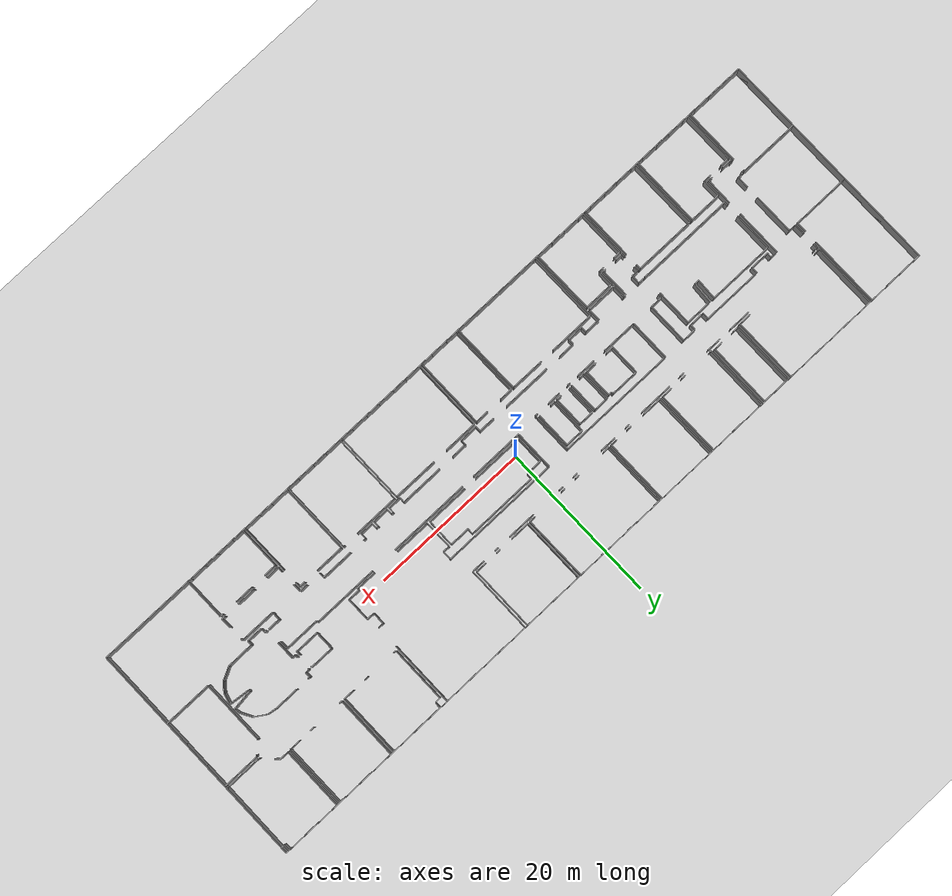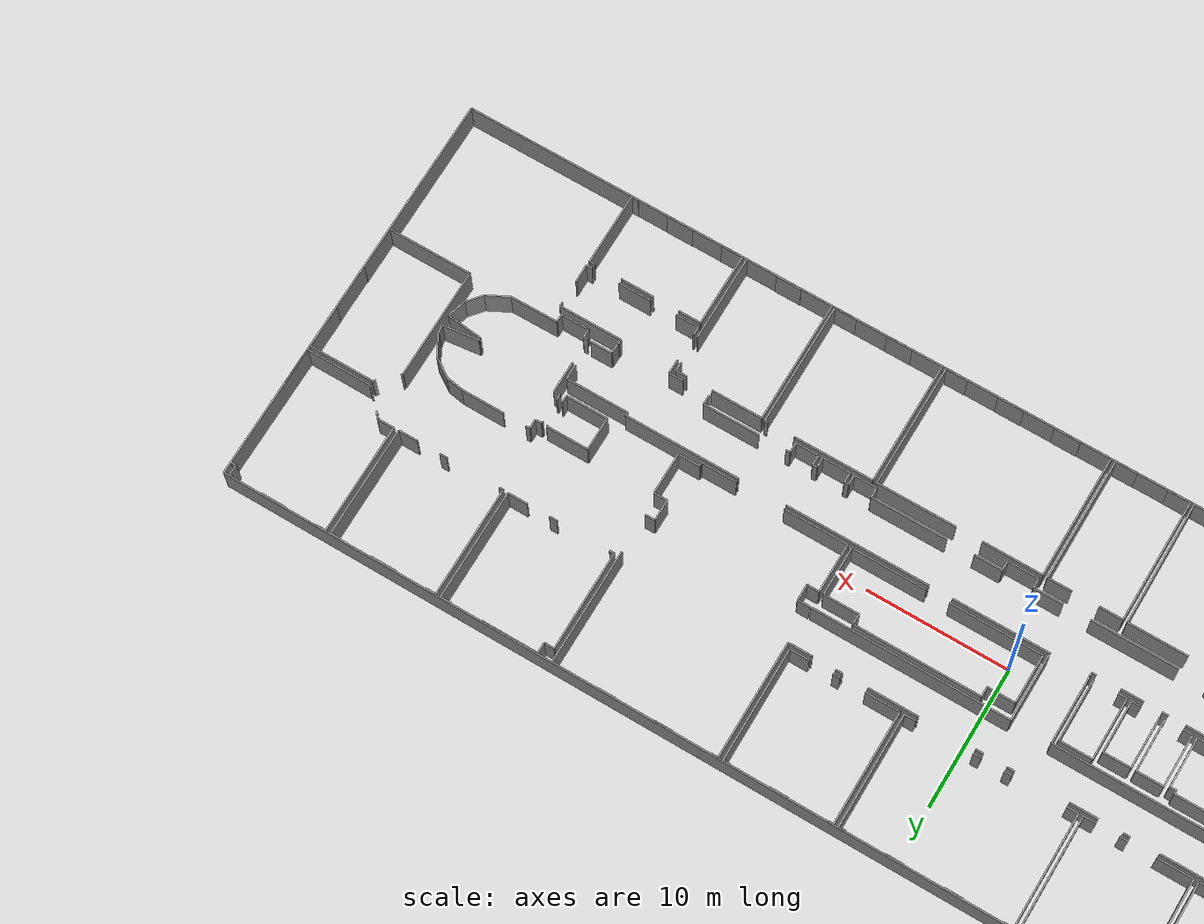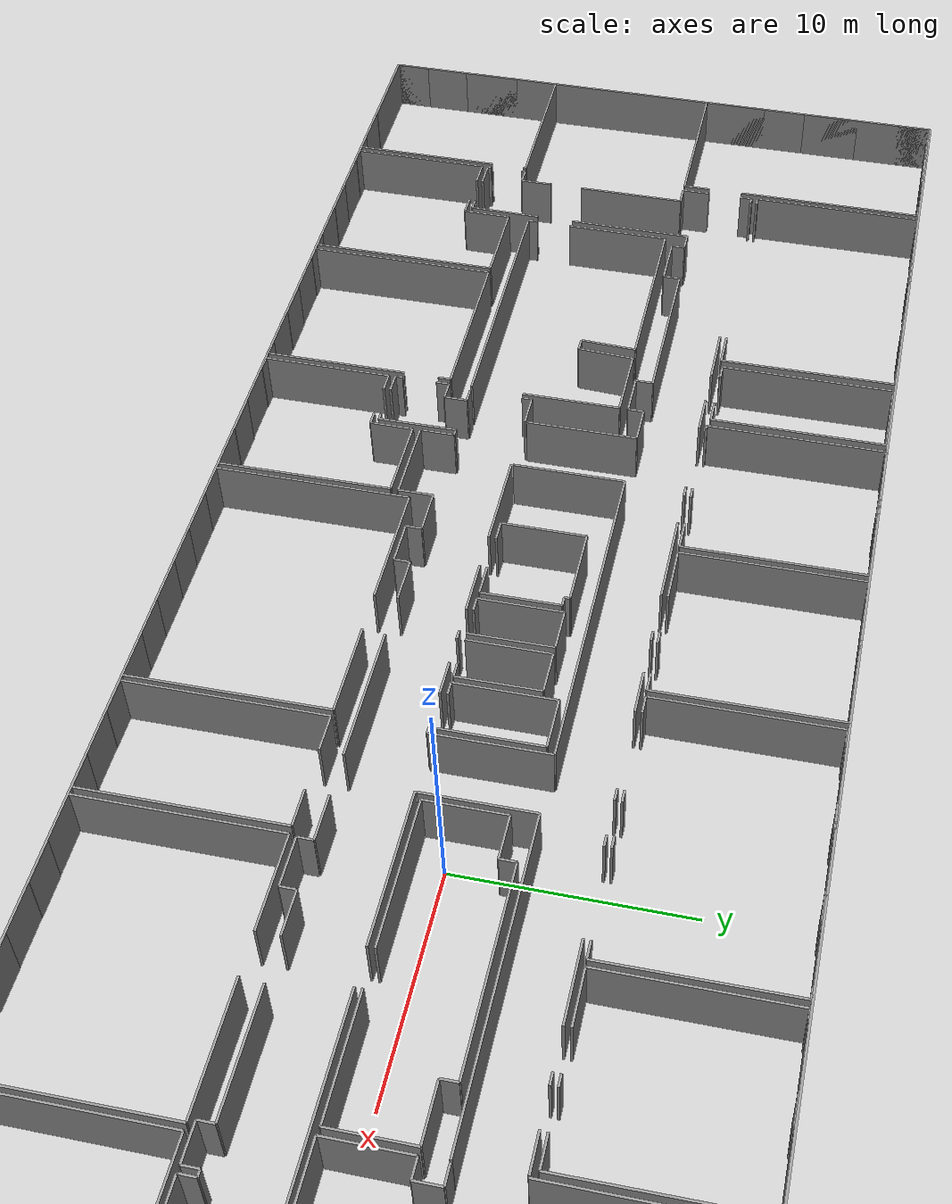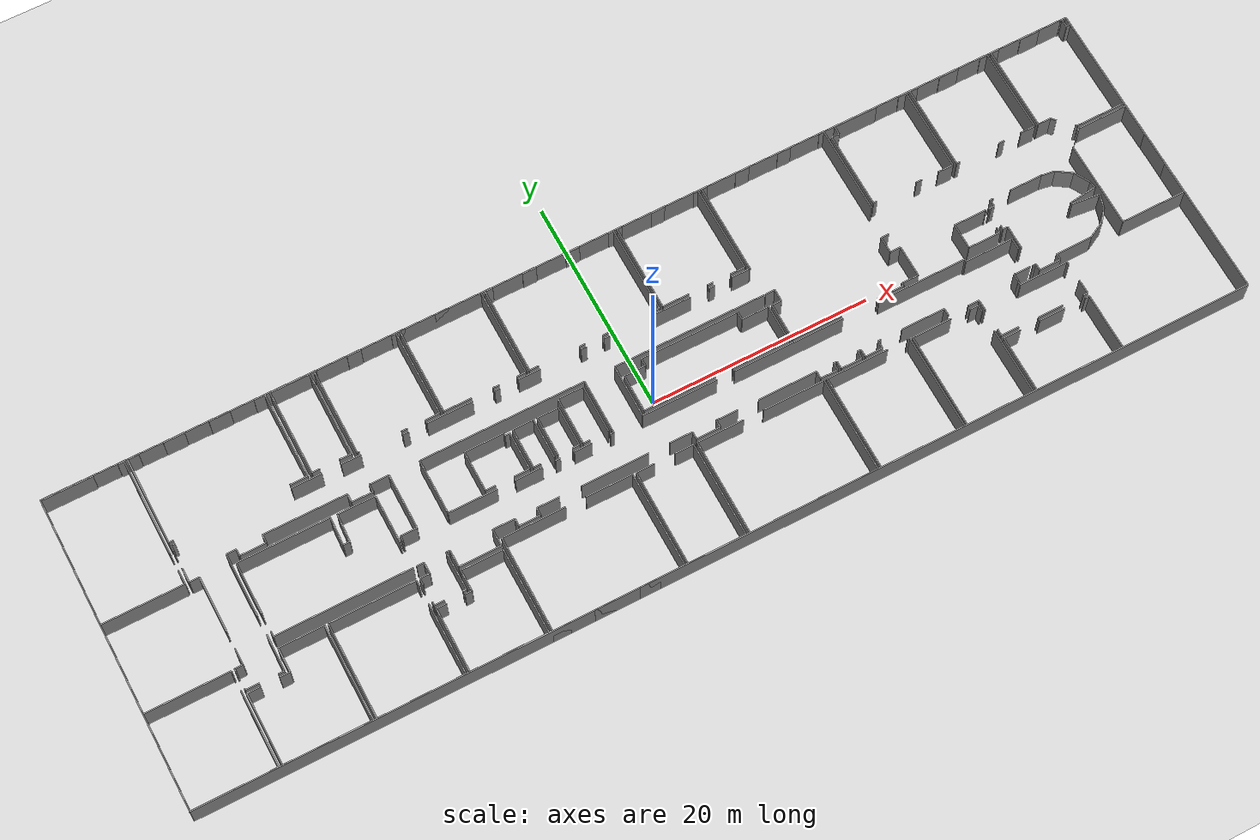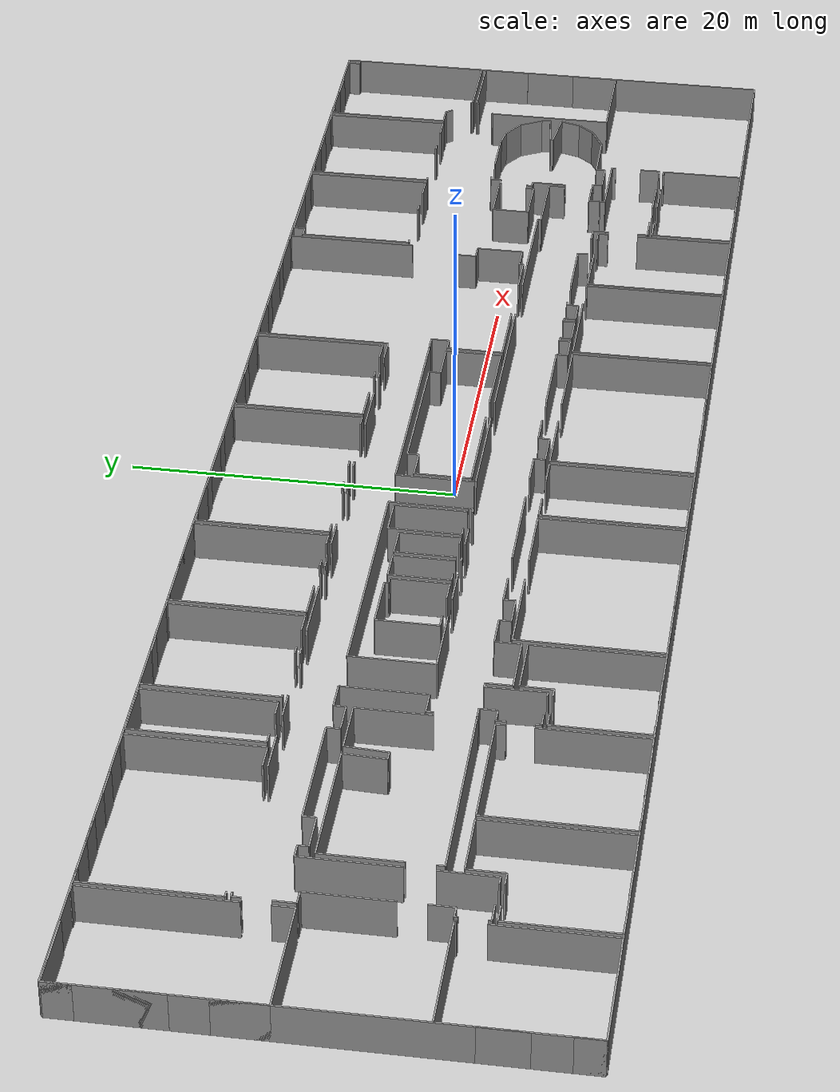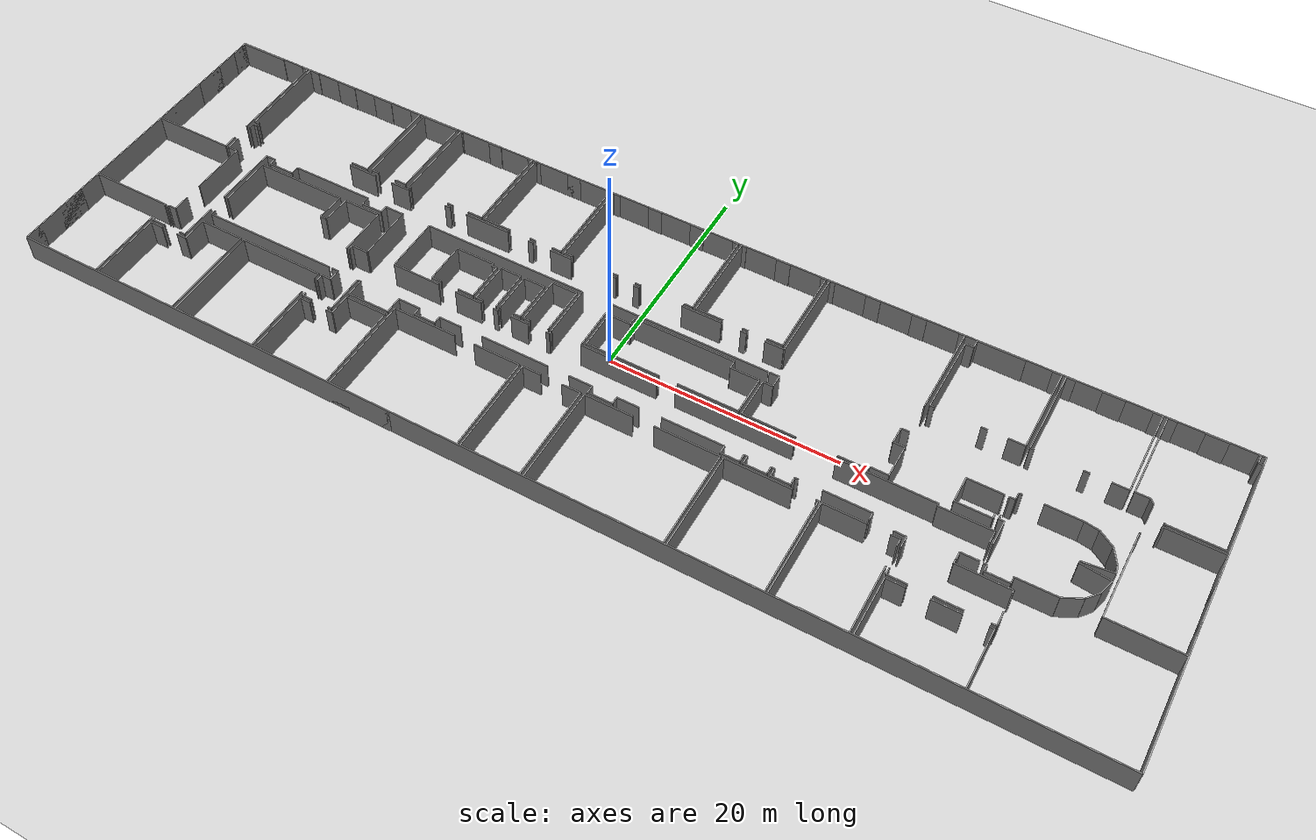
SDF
<sdf version="1.6">
  <world name="default">
    <light name="sun" type="directional">
      <cast_shadows>1</cast_shadows>
      <pose frame="">0 0 10 0 -0 0</pose>
      <diffuse>0.8 0.8 0.8 1</diffuse>
      <specular>0.1 0.1 0.1 1</specular>
      <attenuation>
        <range>1000</range>
        <constant>0.9</constant>
        <linear>0.01</linear>
        <quadratic>0.001</quadratic>
      </attenuation>
      <direction>-0.5 0.5 -1</direction>
    </light>
    <model name="ground_plane">
      <static>1</static>
      <link name="link">
        <collision name="collision">
          <geometry>
            <plane>
              <normal>0 0 1</normal>
              <size>100 100</size>
            </plane>
          </geometry>
          <surface>
            <friction>
              <ode>
                <mu>100</mu>
                <mu2>50</mu2>
              </ode>
              <torsional>
                <ode />
              </torsional>
            </friction>
            <contact>
              <ode />
            </contact>
            <bounce />
          </surface>
          <max_contacts>10</max_contacts>
        </collision>
        <visual name="visual">
          <cast_shadows>0</cast_shadows>
          <geometry>
            <plane>
              <normal>0 0 1</normal>
              <size>100 100</size>
            </plane>
          </geometry>
          <material>
            <script>
              <uri>file://media/materials/scripts/gazebo.material</uri>
              <name>Gazebo/Grey</name>
            </script>
          </material>
        </visual>
        <self_collide>0</self_collide>
        <kinematic>0</kinematic>
        <gravity>1</gravity>
      </link>
    </model>
    <gravity>0 0 -9.8</gravity>
    <magnetic_field>6e-06 2.3e-05 -4.2e-05</magnetic_field>
    <atmosphere type="adiabatic" />
    <physics default="0" name="default_physics" type="ode">
      <max_step_size>0.001</max_step_size>
      <real_time_factor>1</real_time_factor>
      <real_time_update_rate>1000</real_time_update_rate>
    </physics>
    <scene>
      <ambient>0.4 0.4 0.4 1</ambient>
      <background>0.7 0.7 0.7 1</background>
      <shadows>1</shadows>
    </scene>
    <spherical_coordinates>
      <surface_model>EARTH_WGS84</surface_model>
      <latitude_deg>0</latitude_deg>
      <longitude_deg>0</longitude_deg>
      <elevation>0</elevation>
      <heading_deg>0</heading_deg>
    </spherical_coordinates>
  <model name="0510032262_A_40_1_104">
		<static>1</static>
		<link name="Wall_0">
			<collision name="Wall_0_Collision">
				<geometry>
					<box>
						<size>7.26845829235 0.1 2.5</size>
					</box>
				</geometry>
				<pose frame="">3.63422914618 0 1.25 0 0 0</pose>
			</collision>
			<visual name="Wall_0_Visual">
				<pose frame="">3.63422914618 0 1.25 0 0 0</pose>
				<geometry>
					<box>
						<size>7.26845829235 0.1 2.5</size>
					</box>
				</geometry>
				<material>
					<script>
						<uri>file://media/materials/scripts/gazebo.material</uri>
						<name>Gazebo/Grey</name>
					</script>
					<ambient>1 1 1 1</ambient>
				</material>
			</visual>
			<pose frame="">7.26845829235 -11.874861186 0 0 0 3.14159265359</pose>
		</link>
		<link name="Wall_1">
			<collision name="Wall_1_Collision">
				<geometry>
					<box>
						<size>3.11844401434 0.1 2.5</size>
					</box>
				</geometry>
				<pose frame="">1.55922200717 0 1.25 0 0 0</pose>
			</collision>
			<visual name="Wall_1_Visual">
				<pose frame="">1.55922200717 0 1.25 0 0 0</pose>
				<geometry>
					<box>
						<size>3.11844401434 0.1 2.5</size>
					</box>
				</geometry>
				<material>
					<script>
						<uri>file://media/materials/scripts/gazebo.material</uri>
						<name>Gazebo/Grey</name>
					</script>
					<ambient>1 1 1 1</ambient>
				</material>
			</visual>
			<pose frame="">0.0 -11.874861186 0 0 0 1.57079632679</pose>
		</link>
		<link name="Wall_2">
			<collision name="Wall_2_Collision">
				<geometry>
					<box>
						<size>2.82285750547 0.1 2.5</size>
					</box>
				</geometry>
				<pose frame="">1.41142875274 0 1.25 0 0 0</pose>
			</collision>
			<visual name="Wall_2_Visual">
				<pose frame="">1.41142875274 0 1.25 0 0 0</pose>
				<geometry>
					<box>
						<size>2.82285750547 0.1 2.5</size>
					</box>
				</geometry>
				<material>
					<script>
						<uri>file://media/materials/scripts/gazebo.material</uri>
						<name>Gazebo/Grey</name>
					</script>
					<ambient>1 1 1 1</ambient>
				</material>
			</visual>
			<pose frame="">0.0 -6.63032649047 0 0 0 1.57079632679</pose>
		</link>
		<link name="Wall_3">
			<collision name="Wall_3_Collision">
				<geometry>
					<box>
						<size>1.63987689184 0.1 2.5</size>
					</box>
				</geometry>
				<pose frame="">0.819938445918 0 1.25 0 0 0</pose>
			</collision>
			<visual name="Wall_3_Visual">
				<pose frame="">0.819938445918 0 1.25 0 0 0</pose>
				<geometry>
					<box>
						<size>1.63987689184 0.1 2.5</size>
					</box>
				</geometry>
				<material>
					<script>
						<uri>file://media/materials/scripts/gazebo.material</uri>
						<name>Gazebo/Grey</name>
					</script>
					<ambient>1 1 1 1</ambient>
				</material>
			</visual>
			<pose frame="">0.0 -1.69584668592 0 0 0 1.57079632679</pose>
		</link>
		<link name="Wall_4">
			<collision name="Wall_4_Collision">
				<geometry>
					<box>
						<size>4.5400260177 0.1 2.5</size>
					</box>
				</geometry>
				<pose frame="">2.27001300885 0 1.25 0 0 0</pose>
			</collision>
			<visual name="Wall_4_Visual">
				<pose frame="">2.27001300885 0 1.25 0 0 0</pose>
				<geometry>
					<box>
						<size>4.5400260177 0.1 2.5</size>
					</box>
				</geometry>
				<material>
					<script>
						<uri>file://media/materials/scripts/gazebo.material</uri>
						<name>Gazebo/Grey</name>
					</script>
					<ambient>1 1 1 1</ambient>
				</material>
			</visual>
			<pose frame="">0.0 -0.0559697940794 0 0 0 0.0</pose>
		</link>
		<link name="Wall_5">
			<collision name="Wall_5_Collision">
				<geometry>
					<box>
						<size>0.587873211283 0.1 2.5</size>
					</box>
				</geometry>
				<pose frame="">0.293936605641 0 1.25 0 0 0</pose>
			</collision>
			<visual name="Wall_5_Visual">
				<pose frame="">0.293936605641 0 1.25 0 0 0</pose>
				<geometry>
					<box>
						<size>0.587873211283 0.1 2.5</size>
					</box>
				</geometry>
				<material>
					<script>
						<uri>file://media/materials/scripts/gazebo.material</uri>
						<name>Gazebo/Grey</name>
					</script>
					<ambient>1 1 1 1</ambient>
				</material>
			</visual>
			<pose frame="">6.66611669892 -0.0559697940794 0 0 0 0.0</pose>
		</link>
		<link name="Wall_6">
			<collision name="Wall_6_Collision">
				<geometry>
					<box>
						<size>8.90338547451 0.1 2.5</size>
					</box>
				</geometry>
				<pose frame="">4.45169273725 0 1.25 0 0 0</pose>
			</collision>
			<visual name="Wall_6_Visual">
				<pose frame="">4.45169273725 0 1.25 0 0 0</pose>
				<geometry>
					<box>
						<size>8.90338547451 0.1 2.5</size>
					</box>
				</geometry>
				<material>
					<script>
						<uri>file://media/materials/scripts/gazebo.material</uri>
						<name>Gazebo/Grey</name>
					</script>
					<ambient>1 1 1 1</ambient>
				</material>
			</visual>
			<pose frame="">7.25398991021 -0.0559697940794 0 0 0 -1.57079632679</pose>
		</link>
		<link name="Wall_7">
			<collision name="Wall_7_Collision">
				<geometry>
					<box>
						<size>1.3018540469 0.1 2.5</size>
					</box>
				</geometry>
				<pose frame="">0.650927023448 0 1.25 0 0 0</pose>
			</collision>
			<visual name="Wall_7_Visual">
				<pose frame="">0.650927023448 0 1.25 0 0 0</pose>
				<geometry>
					<box>
						<size>1.3018540469 0.1 2.5</size>
					</box>
				</geometry>
				<material>
					<script>
						<uri>file://media/materials/scripts/gazebo.material</uri>
						<name>Gazebo/Grey</name>
					</script>
					<ambient>1 1 1 1</ambient>
				</material>
			</visual>
			<pose frame="">7.25398991021 -10.5730875401 0 0 0 -1.55968242349</pose>
		</link>
		<link name="Wall_8">
			<collision name="Wall_8_Collision">
				<geometry>
					<box>
						<size>0.55144842466 0.1 2.5</size>
					</box>
				</geometry>
				<pose frame="">0.27572421233 0 1.25 0 0 0</pose>
			</collision>
			<visual name="Wall_8_Visual">
				<pose frame="">0.27572421233 0 1.25 0 0 0</pose>
				<geometry>
					<box>
						<size>0.55144842466 0.1 2.5</size>
					</box>
				</geometry>
				<material>
					<script>
						<uri>file://media/materials/scripts/gazebo.material</uri>
						<name>Gazebo/Grey</name>
					</script>
					<ambient>1 1 1 1</ambient>
				</material>
			</visual>
			<pose frame="">11.1216169052 -22.0429609417 0 0 0 3.14159265359</pose>
		</link>
		<link name="Wall_9">
			<collision name="Wall_9_Collision">
				<geometry>
					<box>
						<size>1.21001364343 0.1 2.5</size>
					</box>
				</geometry>
				<pose frame="">0.605006821715 0 1.25 0 0 0</pose>
			</collision>
			<visual name="Wall_9_Visual">
				<pose frame="">0.605006821715 0 1.25 0 0 0</pose>
				<geometry>
					<box>
						<size>1.21001364343 0.1 2.5</size>
					</box>
				</geometry>
				<material>
					<script>
						<uri>file://media/materials/scripts/gazebo.material</uri>
						<name>Gazebo/Grey</name>
					</script>
					<ambient>1 1 1 1</ambient>
				</material>
			</visual>
			<pose frame="">8.97915410731 -22.0429609417 0 0 0 3.14159265359</pose>
		</link>
		<link name="Wall_10">
			<collision name="Wall_10_Collision">
				<geometry>
					<box>
						<size>0.17920487356 0.1 2.5</size>
					</box>
				</geometry>
				<pose frame="">0.0896024367801 0 1.25 0 0 0</pose>
			</collision>
			<visual name="Wall_10_Visual">
				<pose frame="">0.0896024367801 0 1.25 0 0 0</pose>
				<geometry>
					<box>
						<size>0.17920487356 0.1 2.5</size>
					</box>
				</geometry>
				<material>
					<script>
						<uri>file://media/materials/scripts/gazebo.material</uri>
						<name>Gazebo/Grey</name>
					</script>
					<ambient>1 1 1 1</ambient>
				</material>
			</visual>
			<pose frame="">7.76914046388 -22.0429609417 0 0 0 1.57079632679</pose>
		</link>
		<link name="Wall_11">
			<collision name="Wall_11_Collision">
				<geometry>
					<box>
						<size>0.203065012533 0.1 2.5</size>
					</box>
				</geometry>
				<pose frame="">0.101532506266 0 1.25 0 0 0</pose>
			</collision>
			<visual name="Wall_11_Visual">
				<pose frame="">0.101532506266 0 1.25 0 0 0</pose>
				<geometry>
					<box>
						<size>0.203065012533 0.1 2.5</size>
					</box>
				</geometry>
				<material>
					<script>
						<uri>file://media/materials/scripts/gazebo.material</uri>
						<name>Gazebo/Grey</name>
					</script>
					<ambient>1 1 1 1</ambient>
				</material>
			</visual>
			<pose frame="">7.76914046388 -20.2814988736 0 0 0 1.57079632679</pose>
		</link>
		<link name="Wall_12">
			<collision name="Wall_12_Collision">
				<geometry>
					<box>
						<size>0.723672938414 0.1 2.5</size>
					</box>
				</geometry>
				<pose frame="">0.361836469207 0 1.25 0 0 0</pose>
			</collision>
			<visual name="Wall_12_Visual">
				<pose frame="">0.361836469207 0 1.25 0 0 0</pose>
				<geometry>
					<box>
						<size>0.723672938414 0.1 2.5</size>
					</box>
				</geometry>
				<material>
					<script>
						<uri>file://media/materials/scripts/gazebo.material</uri>
						<name>Gazebo/Grey</name>
					</script>
					<ambient>1 1 1 1</ambient>
				</material>
			</visual>
			<pose frame="">7.76914046388 -20.0784338611 0 0 0 0.0</pose>
		</link>
		<link name="Wall_13">
			<collision name="Wall_13_Collision">
				<geometry>
					<box>
						<size>1.51473807786 0.1 2.5</size>
					</box>
				</geometry>
				<pose frame="">0.757369038931 0 1.25 0 0 0</pose>
			</collision>
			<visual name="Wall_13_Visual">
				<pose frame="">0.757369038931 0 1.25 0 0 0</pose>
				<geometry>
					<box>
						<size>1.51473807786 0.1 2.5</size>
					</box>
				</geometry>
				<material>
					<script>
						<uri>file://media/materials/scripts/gazebo.material</uri>
						<name>Gazebo/Grey</name>
					</script>
					<ambient>1 1 1 1</ambient>
				</material>
			</visual>
			<pose frame="">8.49281340229 -20.0784338611 0 0 0 1.57079632679</pose>
		</link>
		<link name="Wall_14">
			<collision name="Wall_14_Collision">
				<geometry>
					<box>
						<size>5.11013104039 0.1 2.5</size>
					</box>
				</geometry>
				<pose frame="">2.5550655202 0 1.25 0 0 0</pose>
			</collision>
			<visual name="Wall_14_Visual">
				<pose frame="">2.5550655202 0 1.25 0 0 0</pose>
				<geometry>
					<box>
						<size>5.11013104039 0.1 2.5</size>
					</box>
				</geometry>
				<material>
					<script>
						<uri>file://media/materials/scripts/gazebo.material</uri>
						<name>Gazebo/Grey</name>
					</script>
					<ambient>1 1 1 1</ambient>
				</material>
			</visual>
			<pose frame="">8.49281340229 -16.9898150205 0 0 0 1.57079632679</pose>
		</link>
		<link name="Wall_15">
			<collision name="Wall_15_Collision">
				<geometry>
					<box>
						<size>0.889297839261 0.1 2.5</size>
					</box>
				</geometry>
				<pose frame="">0.444648919631 0 1.25 0 0 0</pose>
			</collision>
			<visual name="Wall_15_Visual">
				<pose frame="">0.444648919631 0 1.25 0 0 0</pose>
				<geometry>
					<box>
						<size>0.889297839261 0.1 2.5</size>
					</box>
				</geometry>
				<material>
					<script>
						<uri>file://media/materials/scripts/gazebo.material</uri>
						<name>Gazebo/Grey</name>
					</script>
					<ambient>1 1 1 1</ambient>
				</material>
			</visual>
			<pose frame="">8.49281340229 -11.8796839801 0 0 0 3.14159265359</pose>
		</link>
		<link name="Wall_16">
			<collision name="Wall_16_Collision">
				<geometry>
					<box>
						<size>1.3100231621 0.1 2.5</size>
					</box>
				</geometry>
				<pose frame="">0.655011581051 0 1.25 0 0 0</pose>
			</collision>
			<visual name="Wall_16_Visual">
				<pose frame="">0.655011581051 0 1.25 0 0 0</pose>
				<geometry>
					<box>
						<size>1.3100231621 0.1 2.5</size>
					</box>
				</geometry>
				<material>
					<script>
						<uri>file://media/materials/scripts/gazebo.material</uri>
						<name>Gazebo/Grey</name>
					</script>
					<ambient>1 1 1 1</ambient>
				</material>
			</visual>
			<pose frame="">7.60351556303 -11.8796839801 0 0 0 1.57079632679</pose>
		</link>
		<link name="Wall_17">
			<collision name="Wall_17_Collision">
				<geometry>
					<box>
						<size>0.561601675286 0.1 2.5</size>
					</box>
				</geometry>
				<pose frame="">0.280800837643 0 1.25 0 0 0</pose>
			</collision>
			<visual name="Wall_17_Visual">
				<pose frame="">0.280800837643 0 1.25 0 0 0</pose>
				<geometry>
					<box>
						<size>0.561601675286 0.1 2.5</size>
					</box>
				</geometry>
				<material>
					<script>
						<uri>file://media/materials/scripts/gazebo.material</uri>
						<name>Gazebo/Grey</name>
					</script>
					<ambient>1 1 1 1</ambient>
				</material>
			</visual>
			<pose frame="">7.60351556303 -8.95833994352 0 0 0 1.57079632679</pose>
		</link>
		<link name="Wall_18">
			<collision name="Wall_18_Collision">
				<geometry>
					<box>
						<size>0.356759843894 0.1 2.5</size>
					</box>
				</geometry>
				<pose frame="">0.178379921947 0 1.25 0 0 0</pose>
			</collision>
			<visual name="Wall_18_Visual">
				<pose frame="">0.178379921947 0 1.25 0 0 0</pose>
				<geometry>
					<box>
						<size>0.356759843894 0.1 2.5</size>
					</box>
				</geometry>
				<material>
					<script>
						<uri>file://media/materials/scripts/gazebo.material</uri>
						<name>Gazebo/Grey</name>
					</script>
					<ambient>1 1 1 1</ambient>
				</material>
			</visual>
			<pose frame="">7.60351556303 -8.39673826824 0 0 0 0.0</pose>
		</link>
		<link name="Wall_19">
			<collision name="Wall_19_Collision">
				<geometry>
					<box>
						<size>2.68705777834 0.1 2.5</size>
					</box>
				</geometry>
				<pose frame="">1.34352888917 0 1.25 0 0 0</pose>
			</collision>
			<visual name="Wall_19_Visual">
				<pose frame="">1.34352888917 0 1.25 0 0 0</pose>
				<geometry>
					<box>
						<size>2.68705777834 0.1 2.5</size>
					</box>
				</geometry>
				<material>
					<script>
						<uri>file://media/materials/scripts/gazebo.material</uri>
						<name>Gazebo/Grey</name>
					</script>
					<ambient>1 1 1 1</ambient>
				</material>
			</visual>
			<pose frame="">18.0830662817 -8.39673826824 0 0 0 0.0</pose>
		</link>
		<link name="Wall_20">
			<collision name="Wall_20_Collision">
				<geometry>
					<box>
						<size>1.77986483485 0.1 2.5</size>
					</box>
				</geometry>
				<pose frame="">0.889932417426 0 1.25 0 0 0</pose>
			</collision>
			<visual name="Wall_20_Visual">
				<pose frame="">0.889932417426 0 1.25 0 0 0</pose>
				<geometry>
					<box>
						<size>1.77986483485 0.1 2.5</size>
					</box>
				</geometry>
				<material>
					<script>
						<uri>file://media/materials/scripts/gazebo.material</uri>
						<name>Gazebo/Grey</name>
					</script>
					<ambient>1 1 1 1</ambient>
				</material>
			</visual>
			<pose frame="">22.4537868452 -8.39673826824 0 0 0 0.0</pose>
		</link>
		<link name="Wall_21">
			<collision name="Wall_21_Collision">
				<geometry>
					<box>
						<size>0.548910112003 0.1 2.5</size>
					</box>
				</geometry>
				<pose frame="">0.274455056002 0 1.25 0 0 0</pose>
			</collision>
			<visual name="Wall_21_Visual">
				<pose frame="">0.274455056002 0 1.25 0 0 0</pose>
				<geometry>
					<box>
						<size>0.548910112003 0.1 2.5</size>
					</box>
				</geometry>
				<material>
					<script>
						<uri>file://media/materials/scripts/gazebo.material</uri>
						<name>Gazebo/Grey</name>
					</script>
					<ambient>1 1 1 1</ambient>
				</material>
			</visual>
			<pose frame="">27.9376844243 -8.39673826824 0 0 0 0.0</pose>
		</link>
		<link name="Wall_22">
			<collision name="Wall_22_Collision">
				<geometry>
					<box>
						<size>4.13668813656 0.1 2.5</size>
					</box>
				</geometry>
				<pose frame="">2.06834406828 0 1.25 0 0 0</pose>
			</collision>
			<visual name="Wall_22_Visual">
				<pose frame="">2.06834406828 0 1.25 0 0 0</pose>
				<geometry>
					<box>
						<size>4.13668813656 0.1 2.5</size>
					</box>
				</geometry>
				<material>
					<script>
						<uri>file://media/materials/scripts/gazebo.material</uri>
						<name>Gazebo/Grey</name>
					</script>
					<ambient>1 1 1 1</ambient>
				</material>
			</visual>
			<pose frame="">30.0883967383 -8.39673826824 0 0 0 0.0</pose>
		</link>
		<link name="Wall_23">
			<collision name="Wall_23_Collision">
				<geometry>
					<box>
						<size>0.481771742234 0.1 2.5</size>
					</box>
				</geometry>
				<pose frame="">0.240885871117 0 1.25 0 0 0</pose>
			</collision>
			<visual name="Wall_23_Visual">
				<pose frame="">0.240885871117 0 1.25 0 0 0</pose>
				<geometry>
					<box>
						<size>0.481771742234 0.1 2.5</size>
					</box>
				</geometry>
				<material>
					<script>
						<uri>file://media/materials/scripts/gazebo.material</uri>
						<name>Gazebo/Grey</name>
					</script>
					<ambient>1 1 1 1</ambient>
				</material>
			</visual>
			<pose frame="">36.1908811118 -8.39673826824 0 0 0 0.0</pose>
		</link>
		<link name="Wall_24">
			<collision name="Wall_24_Collision">
				<geometry>
					<box>
						<size>1.98089919726 0.1 2.5</size>
					</box>
				</geometry>
				<pose frame="">0.990449598629 0 1.25 0 0 0</pose>
			</collision>
			<visual name="Wall_24_Visual">
				<pose frame="">0.990449598629 0 1.25 0 0 0</pose>
				<geometry>
					<box>
						<size>1.98089919726 0.1 2.5</size>
					</box>
				</geometry>
				<material>
					<script>
						<uri>file://media/materials/scripts/gazebo.material</uri>
						<name>Gazebo/Grey</name>
					</script>
					<ambient>1 1 1 1</ambient>
				</material>
			</visual>
			<pose frame="">38.3493352794 -8.39673826824 0 0 0 0.0</pose>
		</link>
		<link name="Wall_25">
			<collision name="Wall_25_Collision">
				<geometry>
					<box>
						<size>0.526953707523 0.1 2.5</size>
					</box>
				</geometry>
				<pose frame="">0.263476853761 0 1.25 0 0 0</pose>
			</collision>
			<visual name="Wall_25_Visual">
				<pose frame="">0.263476853761 0 1.25 0 0 0</pose>
				<geometry>
					<box>
						<size>0.526953707523 0.1 2.5</size>
					</box>
				</geometry>
				<material>
					<script>
						<uri>file://media/materials/scripts/gazebo.material</uri>
						<name>Gazebo/Grey</name>
					</script>
					<ambient>1 1 1 1</ambient>
				</material>
			</visual>
			<pose frame="">44.0600310943 -8.39673826824 0 0 0 0.0</pose>
		</link>
		<link name="Wall_26">
			<collision name="Wall_26_Collision">
				<geometry>
					<box>
						<size>0.529999682711 0.1 2.5</size>
					</box>
				</geometry>
				<pose frame="">0.264999841355 0 1.25 0 0 0</pose>
			</collision>
			<visual name="Wall_26_Visual">
				<pose frame="">0.264999841355 0 1.25 0 0 0</pose>
				<geometry>
					<box>
						<size>0.529999682711 0.1 2.5</size>
					</box>
				</geometry>
				<material>
					<script>
						<uri>file://media/materials/scripts/gazebo.material</uri>
						<name>Gazebo/Grey</name>
					</script>
					<ambient>1 1 1 1</ambient>
				</material>
			</visual>
			<pose frame="">46.1923406416 -8.39673826824 0 0 0 0.0</pose>
		</link>
		<link name="Wall_27">
			<collision name="Wall_27_Collision">
				<geometry>
					<box>
						<size>3.52990449599 0.1 2.5</size>
					</box>
				</geometry>
				<pose frame="">1.76495224799 0 1.25 0 0 0</pose>
			</collision>
			<visual name="Wall_27_Visual">
				<pose frame="">1.76495224799 0 1.25 0 0 0</pose>
				<geometry>
					<box>
						<size>3.52990449599 0.1 2.5</size>
					</box>
				</geometry>
				<material>
					<script>
						<uri>file://media/materials/scripts/gazebo.material</uri>
						<name>Gazebo/Grey</name>
					</script>
					<ambient>1 1 1 1</ambient>
				</material>
			</visual>
			<pose frame="">50.6534251356 -8.39673826824 0 0 0 0.0</pose>
		</link>
		<link name="Wall_28">
			<collision name="Wall_28_Collision">
				<geometry>
					<box>
						<size>0.510200843989 0.1 2.5</size>
					</box>
				</geometry>
				<pose frame="">0.255100421994 0 1.25 0 0 0</pose>
			</collision>
			<visual name="Wall_28_Visual">
				<pose frame="">0.255100421994 0 1.25 0 0 0</pose>
				<geometry>
					<box>
						<size>0.510200843989 0.1 2.5</size>
					</box>
				</geometry>
				<material>
					<script>
						<uri>file://media/materials/scripts/gazebo.material</uri>
						<name>Gazebo/Grey</name>
					</script>
					<ambient>1 1 1 1</ambient>
				</material>
			</visual>
			<pose frame="">55.9176317543 -8.39673826824 0 0 0 0.0</pose>
		</link>
		<link name="Wall_29">
			<collision name="Wall_29_Collision">
				<geometry>
					<box>
						<size>1.62718532855 0.1 2.5</size>
					</box>
				</geometry>
				<pose frame="">0.813592664276 0 1.25 0 0 0</pose>
			</collision>
			<visual name="Wall_29_Visual">
				<pose frame="">0.813592664276 0 1.25 0 0 0</pose>
				<geometry>
					<box>
						<size>1.62718532855 0.1 2.5</size>
					</box>
				</geometry>
				<material>
					<script>
						<uri>file://media/materials/scripts/gazebo.material</uri>
						<name>Gazebo/Grey</name>
					</script>
					<ambient>1 1 1 1</ambient>
				</material>
			</visual>
			<pose frame="">58.0388996415 -8.39673826824 0 0 0 0.0</pose>
		</link>
		<link name="Wall_30">
			<collision name="Wall_30_Collision">
				<geometry>
					<box>
						<size>13.8981502047 0.1 2.5</size>
					</box>
				</geometry>
				<pose frame="">6.94907510233 0 1.25 0 0 0</pose>
			</collision>
			<visual name="Wall_30_Visual">
				<pose frame="">6.94907510233 0 1.25 0 0 0</pose>
				<geometry>
					<box>
						<size>13.8981502047 0.1 2.5</size>
					</box>
				</geometry>
				<material>
					<script>
						<uri>file://media/materials/scripts/gazebo.material</uri>
						<name>Gazebo/Grey</name>
					</script>
					<ambient>1 1 1 1</ambient>
				</material>
			</visual>
			<pose frame="">59.66608497 -11.0591744138 0 0 0 3.14159265359</pose>
		</link>
		<link name="Wall_31">
			<collision name="Wall_31_Collision">
				<geometry>
					<box>
						<size>4.78789224863 0.1 2.5</size>
					</box>
				</geometry>
				<pose frame="">2.39394612431 0 1.25 0 0 0</pose>
			</collision>
			<visual name="Wall_31_Visual">
				<pose frame="">2.39394612431 0 1.25 0 0 0</pose>
				<geometry>
					<box>
						<size>4.78789224863 0.1 2.5</size>
					</box>
				</geometry>
				<material>
					<script>
						<uri>file://media/materials/scripts/gazebo.material</uri>
						<name>Gazebo/Grey</name>
					</script>
					<ambient>1 1 1 1</ambient>
				</material>
			</visual>
			<pose frame="">45.7679347654 -11.0591744138 0 0 0 -1.57079632679</pose>
		</link>
		<link name="Wall_32">
			<collision name="Wall_32_Collision">
				<geometry>
					<box>
						<size>4.77685058857 0.1 2.5</size>
					</box>
				</geometry>
				<pose frame="">2.38842529429 0 1.25 0 0 0</pose>
			</collision>
			<visual name="Wall_32_Visual">
				<pose frame="">2.38842529429 0 1.25 0 0 0</pose>
				<geometry>
					<box>
						<size>4.77685058857 0.1 2.5</size>
					</box>
				</geometry>
				<material>
					<script>
						<uri>file://media/materials/scripts/gazebo.material</uri>
						<name>Gazebo/Grey</name>
					</script>
					<ambient>1 1 1 1</ambient>
				</material>
			</visual>
			<pose frame="">43.0049814386 -15.8470666624 0 0 0 1.57079632679</pose>
		</link>
		<link name="Wall_33">
			<collision name="Wall_33_Collision">
				<geometry>
					<box>
						<size>14.8435447536 0.1 2.5</size>
					</box>
				</geometry>
				<pose frame="">7.42177237681 0 1.25 0 0 0</pose>
			</collision>
			<visual name="Wall_33_Visual">
				<pose frame="">7.42177237681 0 1.25 0 0 0</pose>
				<geometry>
					<box>
						<size>14.8435447536 0.1 2.5</size>
					</box>
				</geometry>
				<material>
					<script>
						<uri>file://media/materials/scripts/gazebo.material</uri>
						<name>Gazebo/Grey</name>
					</script>
					<ambient>1 1 1 1</ambient>
				</material>
			</visual>
			<pose frame="">43.0049814386 -11.0702160739 0 0 0 3.14159265359</pose>
		</link>
		<link name="Wall_34">
			<collision name="Wall_34_Collision">
				<geometry>
					<box>
						<size>5.01519814703 0.1 2.5</size>
					</box>
				</geometry>
				<pose frame="">2.50759907352 0 1.25 0 0 0</pose>
			</collision>
			<visual name="Wall_34_Visual">
				<pose frame="">2.50759907352 0 1.25 0 0 0</pose>
				<geometry>
					<box>
						<size>5.01519814703 0.1 2.5</size>
					</box>
				</geometry>
				<material>
					<script>
						<uri>file://media/materials/scripts/gazebo.material</uri>
						<name>Gazebo/Grey</name>
					</script>
					<ambient>1 1 1 1</ambient>
				</material>
			</visual>
			<pose frame="">28.161436685 -11.0702160739 0 0 0 -1.57079632679</pose>
		</link>
		<link name="Wall_35">
			<collision name="Wall_35_Collision">
				<geometry>
					<box>
						<size>5.04540406765 0.1 2.5</size>
					</box>
				</geometry>
				<pose frame="">2.52270203382 0 1.25 0 0 0</pose>
			</collision>
			<visual name="Wall_35_Visual">
				<pose frame="">2.52270203382 0 1.25 0 0 0</pose>
				<geometry>
					<box>
						<size>5.04540406765 0.1 2.5</size>
					</box>
				</geometry>
				<material>
					<script>
						<uri>file://media/materials/scripts/gazebo.material</uri>
						<name>Gazebo/Grey</name>
					</script>
					<ambient>1 1 1 1</ambient>
				</material>
			</visual>
			<pose frame="">25.4436653235 -16.0854142209 0 0 0 1.57079632679</pose>
		</link>
		<link name="Wall_36">
			<collision name="Wall_36_Collision">
				<geometry>
					<box>
						<size>1.72744867849 0.1 2.5</size>
					</box>
				</geometry>
				<pose frame="">0.863724339245 0 1.25 0 0 0</pose>
			</collision>
			<visual name="Wall_36_Visual">
				<pose frame="">0.863724339245 0 1.25 0 0 0</pose>
				<geometry>
					<box>
						<size>1.72744867849 0.1 2.5</size>
					</box>
				</geometry>
				<material>
					<script>
						<uri>file://media/materials/scripts/gazebo.material</uri>
						<name>Gazebo/Grey</name>
					</script>
					<ambient>1 1 1 1</ambient>
				</material>
			</visual>
			<pose frame="">25.4436653235 -11.0400101533 0 0 0 3.14159265359</pose>
		</link>
		<link name="Wall_37">
			<collision name="Wall_37_Collision">
				<geometry>
					<box>
						<size>0.710092965701 0.1 2.5</size>
					</box>
				</geometry>
				<pose frame="">0.355046482851 0 1.25 0 0 0</pose>
			</collision>
			<visual name="Wall_37_Visual">
				<pose frame="">0.355046482851 0 1.25 0 0 0</pose>
				<geometry>
					<box>
						<size>0.710092965701 0.1 2.5</size>
					</box>
				</geometry>
				<material>
					<script>
						<uri>file://media/materials/scripts/gazebo.material</uri>
						<name>Gazebo/Grey</name>
					</script>
					<ambient>1 1 1 1</ambient>
				</material>
			</visual>
			<pose frame="">23.716216645 -11.0400101533 0 0 0 -1.57079632679</pose>
		</link>
		<link name="Wall_38">
			<collision name="Wall_38_Collision">
				<geometry>
					<box>
						<size>1.90969952724 0.1 2.5</size>
					</box>
				</geometry>
				<pose frame="">0.95484976362 0 1.25 0 0 0</pose>
			</collision>
			<visual name="Wall_38_Visual">
				<pose frame="">0.95484976362 0 1.25 0 0 0</pose>
				<geometry>
					<box>
						<size>1.90969952724 0.1 2.5</size>
					</box>
				</geometry>
				<material>
					<script>
						<uri>file://media/materials/scripts/gazebo.material</uri>
						<name>Gazebo/Grey</name>
					</script>
					<ambient>1 1 1 1</ambient>
				</material>
			</visual>
			<pose frame="">23.716216645 -11.750103119 0 0 0 3.14159265359</pose>
		</link>
		<link name="Wall_39">
			<collision name="Wall_39_Collision">
				<geometry>
					<box>
						<size>0.79652251166 0.1 2.5</size>
					</box>
				</geometry>
				<pose frame="">0.39826125583 0 1.25 0 0 0</pose>
			</collision>
			<visual name="Wall_39_Visual">
				<pose frame="">0.39826125583 0 1.25 0 0 0</pose>
				<geometry>
					<box>
						<size>0.79652251166 0.1 2.5</size>
					</box>
				</geometry>
				<material>
					<script>
						<uri>file://media/materials/scripts/gazebo.material</uri>
						<name>Gazebo/Grey</name>
					</script>
					<ambient>1 1 1 1</ambient>
				</material>
			</visual>
			<pose frame="">21.8065171177 -11.750103119 0 0 0 1.57079632679</pose>
		</link>
		<link name="Wall_40">
			<collision name="Wall_40_Collision">
				<geometry>
					<box>
						<size>7.44131738427 0.1 2.5</size>
					</box>
				</geometry>
				<pose frame="">3.72065869213 0 1.25 0 0 0</pose>
			</collision>
			<visual name="Wall_40_Visual">
				<pose frame="">3.72065869213 0 1.25 0 0 0</pose>
				<geometry>
					<box>
						<size>7.44131738427 0.1 2.5</size>
					</box>
				</geometry>
				<material>
					<script>
						<uri>file://media/materials/scripts/gazebo.material</uri>
						<name>Gazebo/Grey</name>
					</script>
					<ambient>1 1 1 1</ambient>
				</material>
			</visual>
			<pose frame="">21.8065171177 -10.9535806073 0 0 0 3.14159265359</pose>
		</link>
		<link name="Wall_41">
			<collision name="Wall_41_Collision">
				<geometry>
					<box>
						<size>0.770758638195 0.1 2.5</size>
					</box>
				</geometry>
				<pose frame="">0.385379319098 0 1.25 0 0 0</pose>
			</collision>
			<visual name="Wall_41_Visual">
				<pose frame="">0.385379319098 0 1.25 0 0 0</pose>
				<geometry>
					<box>
						<size>0.770758638195 0.1 2.5</size>
					</box>
				</geometry>
				<material>
					<script>
						<uri>file://media/materials/scripts/gazebo.material</uri>
						<name>Gazebo/Grey</name>
					</script>
					<ambient>1 1 1 1</ambient>
				</material>
			</visual>
			<pose frame="">14.3651997335 -10.9535806073 0 0 0 -1.57079632679</pose>
		</link>
		<link name="Wall_42">
			<collision name="Wall_42_Collision">
				<geometry>
					<box>
						<size>2.32928260939 0.1 2.5</size>
					</box>
				</geometry>
				<pose frame="">1.16464130469 0 1.25 0 0 0</pose>
			</collision>
			<visual name="Wall_42_Visual">
				<pose frame="">1.16464130469 0 1.25 0 0 0</pose>
				<geometry>
					<box>
						<size>2.32928260939 0.1 2.5</size>
					</box>
				</geometry>
				<material>
					<script>
						<uri>file://media/materials/scripts/gazebo.material</uri>
						<name>Gazebo/Grey</name>
					</script>
					<ambient>1 1 1 1</ambient>
				</material>
			</visual>
			<pose frame="">14.3651997335 -11.7243392455 0 0 0 3.14159265359</pose>
		</link>
		<link name="Wall_43">
			<collision name="Wall_43_Collision">
				<geometry>
					<box>
						<size>0.616809975569 0.1 2.5</size>
					</box>
				</geometry>
				<pose frame="">0.308404987784 0 1.25 0 0 0</pose>
			</collision>
			<visual name="Wall_43_Visual">
				<pose frame="">0.308404987784 0 1.25 0 0 0</pose>
				<geometry>
					<box>
						<size>0.616809975569 0.1 2.5</size>
					</box>
				</geometry>
				<material>
					<script>
						<uri>file://media/materials/scripts/gazebo.material</uri>
						<name>Gazebo/Grey</name>
					</script>
					<ambient>1 1 1 1</ambient>
				</material>
			</visual>
			<pose frame="">12.0359171241 -11.7243392455 0 0 0 1.57079632679</pose>
		</link>
		<link name="Wall_44">
			<collision name="Wall_44_Collision">
				<geometry>
					<box>
						<size>0.878002347939 0.1 2.5</size>
					</box>
				</geometry>
				<pose frame="">0.43900117397 0 1.25 0 0 0</pose>
			</collision>
			<visual name="Wall_44_Visual">
				<pose frame="">0.43900117397 0 1.25 0 0 0</pose>
				<geometry>
					<box>
						<size>0.878002347939 0.1 2.5</size>
					</box>
				</geometry>
				<material>
					<script>
						<uri>file://media/materials/scripts/gazebo.material</uri>
						<name>Gazebo/Grey</name>
					</script>
					<ambient>1 1 1 1</ambient>
				</material>
			</visual>
			<pose frame="">12.0359171241 -11.1075292699 0 0 0 3.14159265359</pose>
		</link>
		<link name="Wall_45">
			<collision name="Wall_45_Collision">
				<geometry>
					<box>
						<size>5.80562870832 0.1 2.5</size>
					</box>
				</geometry>
				<pose frame="">2.90281435416 0 1.25 0 0 0</pose>
			</collision>
			<visual name="Wall_45_Visual">
				<pose frame="">2.90281435416 0 1.25 0 0 0</pose>
				<geometry>
					<box>
						<size>5.80562870832 0.1 2.5</size>
					</box>
				</geometry>
				<material>
					<script>
						<uri>file://media/materials/scripts/gazebo.material</uri>
						<name>Gazebo/Grey</name>
					</script>
					<ambient>1 1 1 1</ambient>
				</material>
			</visual>
			<pose frame="">11.1579147762 -11.1075292699 0 0 0 -1.57079632679</pose>
		</link>
		<link name="Wall_46">
			<collision name="Wall_46_Collision">
				<geometry>
					<box>
						<size>3.38173492852 0.1 2.5</size>
					</box>
				</geometry>
				<pose frame="">1.69086746426 0 1.25 0 0 0</pose>
			</collision>
			<visual name="Wall_46_Visual">
				<pose frame="">1.69086746426 0 1.25 0 0 0</pose>
				<geometry>
					<box>
						<size>3.38173492852 0.1 2.5</size>
					</box>
				</geometry>
				<material>
					<script>
						<uri>file://media/materials/scripts/gazebo.material</uri>
						<name>Gazebo/Grey</name>
					</script>
					<ambient>1 1 1 1</ambient>
				</material>
			</visual>
			<pose frame="">11.1579147762 -18.6614208205 0 0 0 -1.58153003856</pose>
		</link>
		<link name="Wall_47">
			<collision name="Wall_47_Collision">
				<geometry>
					<box>
						<size>1.08855538281 0.1 2.5</size>
					</box>
				</geometry>
				<pose frame="">0.544277691405 0 1.25 0 0 0</pose>
			</collision>
			<visual name="Wall_47_Visual">
				<pose frame="">0.544277691405 0 1.25 0 0 0</pose>
				<geometry>
					<box>
						<size>1.08855538281 0.1 2.5</size>
					</box>
				</geometry>
				<material>
					<script>
						<uri>file://media/materials/scripts/gazebo.material</uri>
						<name>Gazebo/Grey</name>
					</script>
					<ambient>1 1 1 1</ambient>
				</material>
			</visual>
			<pose frame="">23.6099882603 -7.97271313894 0 0 0 3.14159265359</pose>
		</link>
		<link name="Wall_48">
			<collision name="Wall_48_Collision">
				<geometry>
					<box>
						<size>0.690928705143 0.1 2.5</size>
					</box>
				</geometry>
				<pose frame="">0.345464352572 0 1.25 0 0 0</pose>
			</collision>
			<visual name="Wall_48_Visual">
				<pose frame="">0.345464352572 0 1.25 0 0 0</pose>
				<geometry>
					<box>
						<size>0.690928705143 0.1 2.5</size>
					</box>
				</geometry>
				<material>
					<script>
						<uri>file://media/materials/scripts/gazebo.material</uri>
						<name>Gazebo/Grey</name>
					</script>
					<ambient>1 1 1 1</ambient>
				</material>
			</visual>
			<pose frame="">20.7892883206 -7.97271313894 0 0 0 3.14159265359</pose>
		</link>
		<link name="Wall_49">
			<collision name="Wall_49_Collision">
				<geometry>
					<box>
						<size>7.9142050322 0.1 2.5</size>
					</box>
				</geometry>
				<pose frame="">3.9571025161 0 1.25 0 0 0</pose>
			</collision>
			<visual name="Wall_49_Visual">
				<pose frame="">3.9571025161 0 1.25 0 0 0</pose>
				<geometry>
					<box>
						<size>7.9142050322 0.1 2.5</size>
					</box>
				</geometry>
				<material>
					<script>
						<uri>file://media/materials/scripts/gazebo.material</uri>
						<name>Gazebo/Grey</name>
					</script>
					<ambient>1 1 1 1</ambient>
				</material>
			</visual>
			<pose frame="">20.0983596154 -7.97271313894 0 0 0 1.57079632679</pose>
		</link>
		<link name="Wall_50">
			<collision name="Wall_50_Collision">
				<geometry>
					<box>
						<size>3.526097027 0.1 2.5</size>
					</box>
				</geometry>
				<pose frame="">1.7630485135 0 1.25 0 0 0</pose>
			</collision>
			<visual name="Wall_50_Visual">
				<pose frame="">1.7630485135 0 1.25 0 0 0</pose>
				<geometry>
					<box>
						<size>3.526097027 0.1 2.5</size>
					</box>
				</geometry>
				<material>
					<script>
						<uri>file://media/materials/scripts/gazebo.material</uri>
						<name>Gazebo/Grey</name>
					</script>
					<ambient>1 1 1 1</ambient>
				</material>
			</visual>
			<pose frame="">20.0983596154 -0.058508106736 0 0 0 0.0</pose>
		</link>
		<link name="Wall_51">
			<collision name="Wall_51_Collision">
				<geometry>
					<box>
						<size>7.91421825741 0.1 2.5</size>
					</box>
				</geometry>
				<pose frame="">3.9571091287 0 1.25 0 0 0</pose>
			</collision>
			<visual name="Wall_51_Visual">
				<pose frame="">3.9571091287 0 1.25 0 0 0</pose>
				<geometry>
					<box>
						<size>7.91421825741 0.1 2.5</size>
					</box>
				</geometry>
				<material>
					<script>
						<uri>file://media/materials/scripts/gazebo.material</uri>
						<name>Gazebo/Grey</name>
					</script>
					<ambient>1 1 1 1</ambient>
				</material>
			</visual>
			<pose frame="">23.6244566424 -0.058508106736 0 0 0 -1.57262447832</pose>
		</link>
		<link name="Wall_52">
			<collision name="Wall_52_Collision">
				<geometry>
					<box>
						<size>1.34238664848 0.1 2.5</size>
					</box>
				</geometry>
				<pose frame="">0.671193324238 0 1.25 0 0 0</pose>
			</collision>
			<visual name="Wall_52_Visual">
				<pose frame="">0.671193324238 0 1.25 0 0 0</pose>
				<geometry>
					<box>
						<size>1.34238664848 0.1 2.5</size>
					</box>
				</geometry>
				<material>
					<script>
						<uri>file://media/materials/scripts/gazebo.material</uri>
						<name>Gazebo/Grey</name>
					</script>
					<ambient>1 1 1 1</ambient>
				</material>
			</visual>
			<pose frame="">31.4178379922 -8.09607513405 0 0 0 3.14159265359</pose>
		</link>
		<link name="Wall_53">
			<collision name="Wall_53_Collision">
				<geometry>
					<box>
						<size>0.53444172986 0.1 2.5</size>
					</box>
				</geometry>
				<pose frame="">0.26722086493 0 1.25 0 0 0</pose>
			</collision>
			<visual name="Wall_53_Visual">
				<pose frame="">0.26722086493 0 1.25 0 0 0</pose>
				<geometry>
					<box>
						<size>0.53444172986 0.1 2.5</size>
					</box>
				</geometry>
				<material>
					<script>
						<uri>file://media/materials/scripts/gazebo.material</uri>
						<name>Gazebo/Grey</name>
					</script>
					<ambient>1 1 1 1</ambient>
				</material>
			</visual>
			<pose frame="">28.5099470127 -8.09607513405 0 0 0 3.14159265359</pose>
		</link>
		<link name="Wall_54">
			<collision name="Wall_54_Collision">
				<geometry>
					<box>
						<size>0.195576990196 0.1 2.5</size>
					</box>
				</geometry>
				<pose frame="">0.0977884950979 0 1.25 0 0 0</pose>
			</collision>
			<visual name="Wall_54_Visual">
				<pose frame="">0.0977884950979 0 1.25 0 0 0</pose>
				<geometry>
					<box>
						<size>0.195576990196 0.1 2.5</size>
					</box>
				</geometry>
				<material>
					<script>
						<uri>file://media/materials/scripts/gazebo.material</uri>
						<name>Gazebo/Grey</name>
					</script>
					<ambient>1 1 1 1</ambient>
				</material>
			</visual>
			<pose frame="">24.2399974617 -8.09607513405 0 0 0 3.14159265359</pose>
		</link>
		<link name="Wall_55">
			<collision name="Wall_55_Collision">
				<geometry>
					<box>
						<size>8.05431989085 0.1 2.5</size>
					</box>
				</geometry>
				<pose frame="">4.02715994543 0 1.25 0 0 0</pose>
			</collision>
			<visual name="Wall_55_Visual">
				<pose frame="">4.02715994543 0 1.25 0 0 0</pose>
				<geometry>
					<box>
						<size>8.05431989085 0.1 2.5</size>
					</box>
				</geometry>
				<material>
					<script>
						<uri>file://media/materials/scripts/gazebo.material</uri>
						<name>Gazebo/Grey</name>
					</script>
					<ambient>1 1 1 1</ambient>
				</material>
			</visual>
			<pose frame="">24.0444204715 -8.09607513405 0 0 0 1.57079632679</pose>
		</link>
		<link name="Wall_56">
			<collision name="Wall_56_Collision">
				<geometry>
					<box>
						<size>0.17247834502 0.1 2.5</size>
					</box>
				</geometry>
				<pose frame="">0.0862391725101 0 1.25 0 0 0</pose>
			</collision>
			<visual name="Wall_56_Visual">
				<pose frame="">0.0862391725101 0 1.25 0 0 0</pose>
				<geometry>
					<box>
						<size>0.17247834502 0.1 2.5</size>
					</box>
				</geometry>
				<material>
					<script>
						<uri>file://media/materials/scripts/gazebo.material</uri>
						<name>Gazebo/Grey</name>
					</script>
					<ambient>1 1 1 1</ambient>
				</material>
			</visual>
			<pose frame="">24.0444204715 -0.0417552432021 0 0 0 0.0</pose>
		</link>
		<link name="Wall_57">
			<collision name="Wall_57_Collision">
				<geometry>
					<box>
						<size>1.27385220675 0.1 2.5</size>
					</box>
				</geometry>
				<pose frame="">0.636926103373 0 1.25 0 0 0</pose>
			</collision>
			<visual name="Wall_57_Visual">
				<pose frame="">0.636926103373 0 1.25 0 0 0</pose>
				<geometry>
					<box>
						<size>1.27385220675 0.1 2.5</size>
					</box>
				</geometry>
				<material>
					<script>
						<uri>file://media/materials/scripts/gazebo.material</uri>
						<name>Gazebo/Grey</name>
					</script>
					<ambient>1 1 1 1</ambient>
				</material>
			</visual>
			<pose frame="">26.958530317 -0.0417552432021 0 0 0 0.0</pose>
		</link>
		<link name="Wall_58">
			<collision name="Wall_58_Collision">
				<geometry>
					<box>
						<size>0.458038518895 0.1 2.5</size>
					</box>
				</geometry>
				<pose frame="">0.229019259447 0 1.25 0 0 0</pose>
			</collision>
			<visual name="Wall_58_Visual">
				<pose frame="">0.229019259447 0 1.25 0 0 0</pose>
				<geometry>
					<box>
						<size>0.458038518895 0.1 2.5</size>
					</box>
				</geometry>
				<material>
					<script>
						<uri>file://media/materials/scripts/gazebo.material</uri>
						<name>Gazebo/Grey</name>
					</script>
					<ambient>1 1 1 1</ambient>
				</material>
			</visual>
			<pose frame="">30.9520576197 -0.0417552432021 0 0 0 0.0</pose>
		</link>
		<link name="Wall_59">
			<collision name="Wall_59_Collision">
				<geometry>
					<box>
						<size>8.05432361161 0.1 2.5</size>
					</box>
				</geometry>
				<pose frame="">4.0271618058 0 1.25 0 0 0</pose>
			</collision>
			<visual name="Wall_59_Visual">
				<pose frame="">4.0271618058 0 1.25 0 0 0</pose>
				<geometry>
					<box>
						<size>8.05432361161 0.1 2.5</size>
					</box>
				</geometry>
				<material>
					<script>
						<uri>file://media/materials/scripts/gazebo.material</uri>
						<name>Gazebo/Grey</name>
					</script>
					<ambient>1 1 1 1</ambient>
				</material>
			</visual>
			<pose frame="">31.4100961386 -0.0417552432021 0 0 0 -1.56983512196</pose>
		</link>
		<link name="Wall_60">
			<collision name="Wall_60_Collision">
				<geometry>
					<box>
						<size>0.856172859092 0.1 2.5</size>
					</box>
				</geometry>
				<pose frame="">0.428086429546 0 1.25 0 0 0</pose>
			</collision>
			<visual name="Wall_60_Visual">
				<pose frame="">0.428086429546 0 1.25 0 0 0</pose>
				<geometry>
					<box>
						<size>0.856172859092 0.1 2.5</size>
					</box>
				</geometry>
				<material>
					<script>
						<uri>file://media/materials/scripts/gazebo.material</uri>
						<name>Gazebo/Grey</name>
					</script>
					<ambient>1 1 1 1</ambient>
				</material>
			</visual>
			<pose frame="">39.2039851509 -8.1105435162 0 0 0 3.14159265359</pose>
		</link>
		<link name="Wall_61">
			<collision name="Wall_61_Collision">
				<geometry>
					<box>
						<size>0.575816226164 0.1 2.5</size>
					</box>
				</geometry>
				<pose frame="">0.287908113082 0 1.25 0 0 0</pose>
			</collision>
			<visual name="Wall_61_Visual">
				<pose frame="">0.287908113082 0 1.25 0 0 0</pose>
				<geometry>
					<box>
						<size>0.575816226164 0.1 2.5</size>
					</box>
				</geometry>
				<material>
					<script>
						<uri>file://media/materials/scripts/gazebo.material</uri>
						<name>Gazebo/Grey</name>
					</script>
					<ambient>1 1 1 1</ambient>
				</material>
			</visual>
			<pose frame="">36.7580670749 -8.1105435162 0 0 0 3.14159265359</pose>
		</link>
		<link name="Wall_62">
			<collision name="Wall_62_Collision">
				<geometry>
					<box>
						<size>2.4951613415 0.1 2.5</size>
					</box>
				</geometry>
				<pose frame="">1.24758067075 0 1.25 0 0 0</pose>
			</collision>
			<visual name="Wall_62_Visual">
				<pose frame="">1.24758067075 0 1.25 0 0 0</pose>
				<geometry>
					<box>
						<size>2.4951613415 0.1 2.5</size>
					</box>
				</geometry>
				<material>
					<script>
						<uri>file://media/materials/scripts/gazebo.material</uri>
						<name>Gazebo/Grey</name>
					</script>
					<ambient>1 1 1 1</ambient>
				</material>
			</visual>
			<pose frame="">34.253387061 -8.1105435162 0 0 0 3.14159265359</pose>
		</link>
		<link name="Wall_63">
			<collision name="Wall_63_Collision">
				<geometry>
					<box>
						<size>8.1105435162 0.1 2.5</size>
					</box>
				</geometry>
				<pose frame="">4.0552717581 0 1.25 0 0 0</pose>
			</collision>
			<visual name="Wall_63_Visual">
				<pose frame="">4.0552717581 0 1.25 0 0 0</pose>
				<geometry>
					<box>
						<size>8.1105435162 0.1 2.5</size>
					</box>
				</geometry>
				<material>
					<script>
						<uri>file://media/materials/scripts/gazebo.material</uri>
						<name>Gazebo/Grey</name>
					</script>
					<ambient>1 1 1 1</ambient>
				</material>
			</visual>
			<pose frame="">31.7582257195 -8.1105435162 0 0 0 1.57079632679</pose>
		</link>
		<link name="Wall_64">
			<collision name="Wall_64_Collision">
				<geometry>
					<box>
						<size>0.461465240981 0.1 2.5</size>
					</box>
				</geometry>
				<pose frame="">0.230732620491 0 1.25 0 0 0</pose>
			</collision>
			<visual name="Wall_64_Visual">
				<pose frame="">0.230732620491 0 1.25 0 0 0</pose>
				<geometry>
					<box>
						<size>0.461465240981 0.1 2.5</size>
					</box>
				</geometry>
				<material>
					<script>
						<uri>file://media/materials/scripts/gazebo.material</uri>
						<name>Gazebo/Grey</name>
					</script>
					<ambient>1 1 1 1</ambient>
				</material>
			</visual>
			<pose frame="">31.7582257195 -0.0 0 0 0 0.0</pose>
		</link>
		<link name="Wall_65">
			<collision name="Wall_65_Collision">
				<geometry>
					<box>
						<size>1.28514769807 0.1 2.5</size>
					</box>
				</geometry>
				<pose frame="">0.642573849034 0 1.25 0 0 0</pose>
			</collision>
			<visual name="Wall_65_Visual">
				<pose frame="">0.642573849034 0 1.25 0 0 0</pose>
				<geometry>
					<box>
						<size>1.28514769807 0.1 2.5</size>
					</box>
				</geometry>
				<material>
					<script>
						<uri>file://media/materials/scripts/gazebo.material</uri>
						<name>Gazebo/Grey</name>
					</script>
					<ambient>1 1 1 1</ambient>
				</material>
			</visual>
			<pose frame="">34.948503982 -0.0 0 0 0 0.0</pose>
		</link>
		<link name="Wall_66">
			<collision name="Wall_66_Collision">
				<geometry>
					<box>
						<size>0.233651680046 0.1 2.5</size>
					</box>
				</geometry>
				<pose frame="">0.116825840023 0 1.25 0 0 0</pose>
			</collision>
			<visual name="Wall_66_Visual">
				<pose frame="">0.116825840023 0 1.25 0 0 0</pose>
				<geometry>
					<box>
						<size>0.233651680046 0.1 2.5</size>
					</box>
				</geometry>
				<material>
					<script>
						<uri>file://media/materials/scripts/gazebo.material</uri>
						<name>Gazebo/Grey</name>
					</script>
					<ambient>1 1 1 1</ambient>
				</material>
			</visual>
			<pose frame="">38.9457118381 -0.0 0 0 0 0.0</pose>
		</link>
		<link name="Wall_67">
			<collision name="Wall_67_Collision">
				<geometry>
					<box>
						<size>8.11058088875 0.1 2.5</size>
					</box>
				</geometry>
				<pose frame="">4.05529044437 0 1.25 0 0 0</pose>
			</collision>
			<visual name="Wall_67_Visual">
				<pose frame="">4.05529044437 0 1.25 0 0 0</pose>
				<geometry>
					<box>
						<size>8.11058088875 0.1 2.5</size>
					</box>
				</geometry>
				<material>
					<script>
						<uri>file://media/materials/scripts/gazebo.material</uri>
						<name>Gazebo/Grey</name>
					</script>
					<ambient>1 1 1 1</ambient>
				</material>
			</visual>
			<pose frame="">39.1793635181 -0.0 0 0 0 -1.56776057992</pose>
		</link>
		<link name="Wall_68">
			<collision name="Wall_68_Collision">
				<geometry>
					<box>
						<size>0.77723133547 0.1 2.5</size>
					</box>
				</geometry>
				<pose frame="">0.388615667735 0 1.25 0 0 0</pose>
			</collision>
			<visual name="Wall_68_Visual">
				<pose frame="">0.388615667735 0 1.25 0 0 0</pose>
				<geometry>
					<box>
						<size>0.77723133547 0.1 2.5</size>
					</box>
				</geometry>
				<material>
					<script>
						<uri>file://media/materials/scripts/gazebo.material</uri>
						<name>Gazebo/Grey</name>
					</script>
					<ambient>1 1 1 1</ambient>
				</material>
			</visual>
			<pose frame="">51.4601008979 -8.10343624076 0 0 0 3.14159265359</pose>
		</link>
		<link name="Wall_69">
			<collision name="Wall_69_Collision">
				<geometry>
					<box>
						<size>0.547006377511 0.1 2.5</size>
					</box>
				</geometry>
				<pose frame="">0.273503188755 0 1.25 0 0 0</pose>
			</collision>
			<visual name="Wall_69_Visual">
				<pose frame="">0.273503188755 0 1.25 0 0 0</pose>
				<geometry>
					<box>
						<size>0.547006377511 0.1 2.5</size>
					</box>
				</geometry>
				<material>
					<script>
						<uri>file://media/materials/scripts/gazebo.material</uri>
						<name>Gazebo/Grey</name>
					</script>
					<ambient>1 1 1 1</ambient>
				</material>
			</visual>
			<pose frame="">46.7290668528 -8.10343624076 0 0 0 3.14159265359</pose>
		</link>
		<link name="Wall_70">
			<collision name="Wall_70_Collision">
				<geometry>
					<box>
						<size>0.537487705048 0.1 2.5</size>
					</box>
				</geometry>
				<pose frame="">0.268743852524 0 1.25 0 0 0</pose>
			</collision>
			<visual name="Wall_70_Visual">
				<pose frame="">0.268743852524 0 1.25 0 0 0</pose>
				<geometry>
					<box>
						<size>0.537487705048 0.1 2.5</size>
					</box>
				</geometry>
				<material>
					<script>
						<uri>file://media/materials/scripts/gazebo.material</uri>
						<name>Gazebo/Grey</name>
					</script>
					<ambient>1 1 1 1</ambient>
				</material>
			</visual>
			<pose frame="">44.6081797125 -8.10343624076 0 0 0 3.14159265359</pose>
		</link>
		<link name="Wall_71">
			<collision name="Wall_71_Collision">
				<geometry>
					<box>
						<size>0.814036868991 0.1 2.5</size>
					</box>
				</geometry>
				<pose frame="">0.407018434496 0 1.25 0 0 0</pose>
			</collision>
			<visual name="Wall_71_Visual">
				<pose frame="">0.407018434496 0 1.25 0 0 0</pose>
				<geometry>
					<box>
						<size>0.814036868991 0.1 2.5</size>
					</box>
				</geometry>
				<material>
					<script>
						<uri>file://media/materials/scripts/gazebo.material</uri>
						<name>Gazebo/Grey</name>
					</script>
					<ambient>1 1 1 1</ambient>
				</material>
			</visual>
			<pose frame="">40.3367071739 -8.10343624076 0 0 0 3.14159265359</pose>
		</link>
		<link name="Wall_72">
			<collision name="Wall_72_Collision">
				<geometry>
					<box>
						<size>8.05470063775 0.1 2.5</size>
					</box>
				</geometry>
				<pose frame="">4.02735031888 0 1.25 0 0 0</pose>
			</collision>
			<visual name="Wall_72_Visual">
				<pose frame="">4.02735031888 0 1.25 0 0 0</pose>
				<geometry>
					<box>
						<size>8.05470063775 0.1 2.5</size>
					</box>
				</geometry>
				<material>
					<script>
						<uri>file://media/materials/scripts/gazebo.material</uri>
						<name>Gazebo/Grey</name>
					</script>
					<ambient>1 1 1 1</ambient>
				</material>
			</visual>
			<pose frame="">39.5226703049 -8.10343624076 0 0 0 1.57079632679</pose>
		</link>
		<link name="Wall_73">
			<collision name="Wall_73_Collision">
				<geometry>
					<box>
						<size>0.687755814322 0.1 2.5</size>
					</box>
				</geometry>
				<pose frame="">0.343877907161 0 1.25 0 0 0</pose>
			</collision>
			<visual name="Wall_73_Visual">
				<pose frame="">0.343877907161 0 1.25 0 0 0</pose>
				<geometry>
					<box>
						<size>0.687755814322 0.1 2.5</size>
					</box>
				</geometry>
				<material>
					<script>
						<uri>file://media/materials/scripts/gazebo.material</uri>
						<name>Gazebo/Grey</name>
					</script>
					<ambient>1 1 1 1</ambient>
				</material>
			</visual>
			<pose frame="">39.5226703049 -0.0487356030079 0 0 0 0.0</pose>
		</link>
		<link name="Wall_74">
			<collision name="Wall_74_Collision">
				<geometry>
					<box>
						<size>1.2682679189 0.1 2.5</size>
					</box>
				</geometry>
				<pose frame="">0.63413395945 0 1.25 0 0 0</pose>
			</collision>
			<visual name="Wall_74_Visual">
				<pose frame="">0.63413395945 0 1.25 0 0 0</pose>
				<geometry>
					<box>
						<size>1.2682679189 0.1 2.5</size>
					</box>
				</geometry>
				<material>
					<script>
						<uri>file://media/materials/scripts/gazebo.material</uri>
						<name>Gazebo/Grey</name>
					</script>
					<ambient>1 1 1 1</ambient>
				</material>
			</visual>
			<pose frame="">42.9490116445 -0.0487356030079 0 0 0 0.0</pose>
		</link>
		<link name="Wall_75">
			<collision name="Wall_75_Collision">
				<geometry>
					<box>
						<size>1.28095948218 0.1 2.5</size>
					</box>
				</geometry>
				<pose frame="">0.640479741092 0 1.25 0 0 0</pose>
			</collision>
			<visual name="Wall_75_Visual">
				<pose frame="">0.640479741092 0 1.25 0 0 0</pose>
				<geometry>
					<box>
						<size>1.28095948218 0.1 2.5</size>
					</box>
				</geometry>
				<material>
					<script>
						<uri>file://media/materials/scripts/gazebo.material</uri>
						<name>Gazebo/Grey</name>
					</script>
					<ambient>1 1 1 1</ambient>
				</material>
			</visual>
			<pose frame="">46.9431735254 -0.0487356030079 0 0 0 0.0</pose>
		</link>
		<link name="Wall_76">
			<collision name="Wall_76_Collision">
				<geometry>
					<box>
						<size>0.485833042485 0.1 2.5</size>
					</box>
				</geometry>
				<pose frame="">0.242916521243 0 1.25 0 0 0</pose>
			</collision>
			<visual name="Wall_76_Visual">
				<pose frame="">0.242916521243 0 1.25 0 0 0</pose>
				<geometry>
					<box>
						<size>0.485833042485 0.1 2.5</size>
					</box>
				</geometry>
				<material>
					<script>
						<uri>file://media/materials/scripts/gazebo.material</uri>
						<name>Gazebo/Grey</name>
					</script>
					<ambient>1 1 1 1</ambient>
				</material>
			</visual>
			<pose frame="">50.9311165403 -0.0487356030079 0 0 0 0.0</pose>
		</link>
		<link name="Wall_77">
			<collision name="Wall_77_Collision">
				<geometry>
					<box>
						<size>8.05481622384 0.1 2.5</size>
					</box>
				</geometry>
				<pose frame="">4.02740811192 0 1.25 0 0 0</pose>
			</collision>
			<visual name="Wall_77_Visual">
				<pose frame="">4.02740811192 0 1.25 0 0 0</pose>
				<geometry>
					<box>
						<size>8.05481622384 0.1 2.5</size>
					</box>
				</geometry>
				<material>
					<script>
						<uri>file://media/materials/scripts/gazebo.material</uri>
						<name>Gazebo/Grey</name>
					</script>
					<ambient>1 1 1 1</ambient>
				</material>
			</visual>
			<pose frame="">51.4169495828 -0.0487356030079 0 0 0 -1.5654390945</pose>
		</link>
		<link name="Wall_78">
			<collision name="Wall_78_Collision">
				<geometry>
					<box>
						<size>1.37233873782 0.1 2.5</size>
					</box>
				</geometry>
				<pose frame="">0.686169368912 0 1.25 0 0 0</pose>
			</collision>
			<visual name="Wall_78_Visual">
				<pose frame="">0.686169368912 0 1.25 0 0 0</pose>
				<geometry>
					<box>
						<size>1.37233873782 0.1 2.5</size>
					</box>
				</geometry>
				<material>
					<script>
						<uri>file://media/materials/scripts/gazebo.material</uri>
						<name>Gazebo/Grey</name>
					</script>
					<ambient>1 1 1 1</ambient>
				</material>
			</visual>
			<pose frame="">59.4446171907 -8.09379065266 0 0 0 3.14159265359</pose>
		</link>
		<link name="Wall_79">
			<collision name="Wall_79_Collision">
				<geometry>
					<box>
						<size>0.508931687661 0.1 2.5</size>
					</box>
				</geometry>
				<pose frame="">0.25446584383 0 1.25 0 0 0</pose>
			</collision>
			<visual name="Wall_79_Visual">
				<pose frame="">0.25446584383 0 1.25 0 0 0</pose>
				<geometry>
					<box>
						<size>0.508931687661 0.1 2.5</size>
					</box>
				</geometry>
				<material>
					<script>
						<uri>file://media/materials/scripts/gazebo.material</uri>
						<name>Gazebo/Grey</name>
					</script>
					<ambient>1 1 1 1</ambient>
				</material>
			</visual>
			<pose frame="">56.4365897769 -8.09379065266 0 0 0 3.14159265359</pose>
		</link>
		<link name="Wall_80">
			<collision name="Wall_80_Collision">
				<geometry>
					<box>
						<size>2.41964653996 0.1 2.5</size>
					</box>
				</geometry>
				<pose frame="">1.20982326998 0 1.25 0 0 0</pose>
			</collision>
			<visual name="Wall_80_Visual">
				<pose frame="">1.20982326998 0 1.25 0 0 0</pose>
				<geometry>
					<box>
						<size>2.41964653996 0.1 2.5</size>
					</box>
				</geometry>
				<material>
					<script>
						<uri>file://media/materials/scripts/gazebo.material</uri>
						<name>Gazebo/Grey</name>
					</script>
					<ambient>1 1 1 1</ambient>
				</material>
			</visual>
			<pose frame="">54.1790145001 -8.09379065266 0 0 0 3.14159265359</pose>
		</link>
		<link name="Wall_81">
			<collision name="Wall_81_Collision">
				<geometry>
					<box>
						<size>8.05203540946 0.1 2.5</size>
					</box>
				</geometry>
				<pose frame="">4.02601770473 0 1.25 0 0 0</pose>
			</collision>
			<visual name="Wall_81_Visual">
				<pose frame="">4.02601770473 0 1.25 0 0 0</pose>
				<geometry>
					<box>
						<size>8.05203540946 0.1 2.5</size>
					</box>
				</geometry>
				<material>
					<script>
						<uri>file://media/materials/scripts/gazebo.material</uri>
						<name>Gazebo/Grey</name>
					</script>
					<ambient>1 1 1 1</ambient>
				</material>
			</visual>
			<pose frame="">51.7593679601 -8.09379065266 0 0 0 1.57079632679</pose>
		</link>
		<link name="Wall_82">
			<collision name="Wall_82_Collision">
				<geometry>
					<box>
						<size>0.429736332773 0.1 2.5</size>
					</box>
				</geometry>
				<pose frame="">0.214868166386 0 1.25 0 0 0</pose>
			</collision>
			<visual name="Wall_82_Visual">
				<pose frame="">0.214868166386 0 1.25 0 0 0</pose>
				<geometry>
					<box>
						<size>0.429736332773 0.1 2.5</size>
					</box>
				</geometry>
				<material>
					<script>
						<uri>file://media/materials/scripts/gazebo.material</uri>
						<name>Gazebo/Grey</name>
					</script>
					<ambient>1 1 1 1</ambient>
				</material>
			</visual>
			<pose frame="">51.7593679601 -0.0417552432021 0 0 0 0.0</pose>
		</link>
		<link name="Wall_83">
			<collision name="Wall_83_Collision">
				<geometry>
					<box>
						<size>1.26839483453 0.1 2.5</size>
					</box>
				</geometry>
				<pose frame="">0.634197417267 0 1.25 0 0 0</pose>
			</collision>
			<visual name="Wall_83_Visual">
				<pose frame="">0.634197417267 0 1.25 0 0 0</pose>
				<geometry>
					<box>
						<size>1.26839483453 0.1 2.5</size>
					</box>
				</geometry>
				<material>
					<script>
						<uri>file://media/materials/scripts/gazebo.material</uri>
						<name>Gazebo/Grey</name>
					</script>
					<ambient>1 1 1 1</ambient>
				</material>
			</visual>
			<pose frame="">54.9345432624 -0.0417552432021 0 0 0 0.0</pose>
		</link>
		<link name="Wall_84">
			<collision name="Wall_84_Collision">
				<geometry>
					<box>
						<size>0.448012183901 0.1 2.5</size>
					</box>
				</geometry>
				<pose frame="">0.22400609195 0 1.25 0 0 0</pose>
			</collision>
			<visual name="Wall_84_Visual">
				<pose frame="">0.22400609195 0 1.25 0 0 0</pose>
				<geometry>
					<box>
						<size>0.448012183901 0.1 2.5</size>
					</box>
				</geometry>
				<material>
					<script>
						<uri>file://media/materials/scripts/gazebo.material</uri>
						<name>Gazebo/Grey</name>
					</script>
					<ambient>1 1 1 1</ambient>
				</material>
			</visual>
			<pose frame="">58.9510422946 -0.0417552432021 0 0 0 0.0</pose>
		</link>
		<link name="Wall_85">
			<collision name="Wall_85_Collision">
				<geometry>
					<box>
						<size>8.0521643175 0.1 2.5</size>
					</box>
				</geometry>
				<pose frame="">4.02608215875 0 1.25 0 0 0</pose>
			</collision>
			<visual name="Wall_85_Visual">
				<pose frame="">4.02608215875 0 1.25 0 0 0</pose>
				<geometry>
					<box>
						<size>8.0521643175 0.1 2.5</size>
					</box>
				</geometry>
				<material>
					<script>
						<uri>file://media/materials/scripts/gazebo.material</uri>
						<name>Gazebo/Grey</name>
					</script>
					<ambient>1 1 1 1</ambient>
				</material>
			</visual>
			<pose frame="">59.3990544785 -0.0417552432021 0 0 0 -1.56513785368</pose>
		</link>
		<link name="Wall_86">
			<collision name="Wall_86_Collision">
				<geometry>
					<box>
						<size>4.49179807723 0.1 2.5</size>
					</box>
				</geometry>
				<pose frame="">2.24589903861 0 1.25 0 0 0</pose>
			</collision>
			<visual name="Wall_86_Visual">
				<pose frame="">2.24589903861 0 1.25 0 0 0</pose>
				<geometry>
					<box>
						<size>4.49179807723 0.1 2.5</size>
					</box>
				</geometry>
				<material>
					<script>
						<uri>file://media/materials/scripts/gazebo.material</uri>
						<name>Gazebo/Grey</name>
					</script>
					<ambient>1 1 1 1</ambient>
				</material>
			</visual>
			<pose frame="">23.709997779 -16.6434622585 0 0 0 1.57079632679</pose>
		</link>
		<link name="Wall_87">
			<collision name="Wall_87_Collision">
				<geometry>
					<box>
						<size>3.34003870927 0.1 2.5</size>
					</box>
				</geometry>
				<pose frame="">1.67001935463 0 1.25 0 0 0</pose>
			</collision>
			<visual name="Wall_87_Visual">
				<pose frame="">1.67001935463 0 1.25 0 0 0</pose>
				<geometry>
					<box>
						<size>3.34003870927 0.1 2.5</size>
					</box>
				</geometry>
				<material>
					<script>
						<uri>file://media/materials/scripts/gazebo.material</uri>
						<name>Gazebo/Grey</name>
					</script>
					<ambient>1 1 1 1</ambient>
				</material>
			</visual>
			<pose frame="">23.709997779 -12.1516641812 0 0 0 3.14159265359</pose>
		</link>
		<link name="Wall_88">
			<collision name="Wall_88_Collision">
				<geometry>
					<box>
						<size>2.58827991481 0.1 2.5</size>
					</box>
				</geometry>
				<pose frame="">1.29413995741 0 1.25 0 0 0</pose>
			</collision>
			<visual name="Wall_88_Visual">
				<pose frame="">1.29413995741 0 1.25 0 0 0</pose>
				<geometry>
					<box>
						<size>2.58827991481 0.1 2.5</size>
					</box>
				</geometry>
				<material>
					<script>
						<uri>file://media/materials/scripts/gazebo.material</uri>
						<name>Gazebo/Grey</name>
					</script>
					<ambient>1 1 1 1</ambient>
				</material>
			</visual>
			<pose frame="">20.3699590697 -12.1516641812 0 0 0 -1.62829672246</pose>
		</link>
		<link name="Wall_89">
			<collision name="Wall_89_Collision">
				<geometry>
					<box>
						<size>0.587790814466 0.1 2.5</size>
					</box>
				</geometry>
				<pose frame="">0.293895407233 0 1.25 0 0 0</pose>
			</collision>
			<visual name="Wall_89_Visual">
				<pose frame="">0.293895407233 0 1.25 0 0 0</pose>
				<geometry>
					<box>
						<size>0.587790814466 0.1 2.5</size>
					</box>
				</geometry>
				<material>
					<script>
						<uri>file://media/materials/scripts/gazebo.material</uri>
						<name>Gazebo/Grey</name>
					</script>
					<ambient>1 1 1 1</ambient>
				</material>
			</visual>
			<pose frame="">20.221213948 -14.7356664657 0 0 0 3.12928491836</pose>
		</link>
		<link name="Wall_90">
			<collision name="Wall_90_Collision">
				<geometry>
					<box>
						<size>2.58584399931 0.1 2.5</size>
					</box>
				</geometry>
				<pose frame="">1.29292199966 0 1.25 0 0 0</pose>
			</collision>
			<visual name="Wall_90_Visual">
				<pose frame="">1.29292199966 0 1.25 0 0 0</pose>
				<geometry>
					<box>
						<size>2.58584399931 0.1 2.5</size>
					</box>
				</geometry>
				<material>
					<script>
						<uri>file://media/materials/scripts/gazebo.material</uri>
						<name>Gazebo/Grey</name>
					</script>
					<ambient>1 1 1 1</ambient>
				</material>
			</visual>
			<pose frame="">19.6334676524 -14.7284322746 0 0 0 1.52592129538</pose>
		</link>
		<link name="Wall_91">
			<collision name="Wall_91_Collision">
				<geometry>
					<box>
						<size>8.2017958562 0.1 2.5</size>
					</box>
				</geometry>
				<pose frame="">4.1008979281 0 1.25 0 0 0</pose>
			</collision>
			<visual name="Wall_91_Visual">
				<pose frame="">4.1008979281 0 1.25 0 0 0</pose>
				<geometry>
					<box>
						<size>8.2017958562 0.1 2.5</size>
					</box>
				</geometry>
				<material>
					<script>
						<uri>file://media/materials/scripts/gazebo.material</uri>
						<name>Gazebo/Grey</name>
					</script>
					<ambient>1 1 1 1</ambient>
				</material>
			</visual>
			<pose frame="">19.7494685408 -12.145191484 0 0 0 3.14159265359</pose>
		</link>
		<link name="Wall_92">
			<collision name="Wall_92_Collision">
				<geometry>
					<box>
						<size>4.81594060348 0.1 2.5</size>
					</box>
				</geometry>
				<pose frame="">2.40797030174 0 1.25 0 0 0</pose>
			</collision>
			<visual name="Wall_92_Visual">
				<pose frame="">2.40797030174 0 1.25 0 0 0</pose>
				<geometry>
					<box>
						<size>4.81594060348 0.1 2.5</size>
					</box>
				</geometry>
				<material>
					<script>
						<uri>file://media/materials/scripts/gazebo.material</uri>
						<name>Gazebo/Grey</name>
					</script>
					<ambient>1 1 1 1</ambient>
				</material>
			</visual>
			<pose frame="">11.5476726846 -12.145191484 0 0 0 -1.57079632679</pose>
		</link>
		<link name="Wall_93">
			<collision name="Wall_93_Collision">
				<geometry>
					<box>
						<size>0.469587841482 0.1 2.5</size>
					</box>
				</geometry>
				<pose frame="">0.234793920741 0 1.25 0 0 0</pose>
			</collision>
			<visual name="Wall_93_Visual">
				<pose frame="">0.234793920741 0 1.25 0 0 0</pose>
				<geometry>
					<box>
						<size>0.469587841482 0.1 2.5</size>
					</box>
				</geometry>
				<material>
					<script>
						<uri>file://media/materials/scripts/gazebo.material</uri>
						<name>Gazebo/Grey</name>
					</script>
					<ambient>1 1 1 1</ambient>
				</material>
			</visual>
			<pose frame="">11.5476726846 -18.6062125202 0 0 0 -1.57079632679</pose>
		</link>
		<link name="Wall_94">
			<collision name="Wall_94_Collision">
				<geometry>
					<box>
						<size>12.162351582 0.1 2.5</size>
					</box>
				</geometry>
				<pose frame="">6.08117579101 0 1.25 0 0 0</pose>
			</collision>
			<visual name="Wall_94_Visual">
				<pose frame="">6.08117579101 0 1.25 0 0 0</pose>
				<geometry>
					<box>
						<size>12.162351582 0.1 2.5</size>
					</box>
				</geometry>
				<material>
					<script>
						<uri>file://media/materials/scripts/gazebo.material</uri>
						<name>Gazebo/Grey</name>
					</script>
					<ambient>1 1 1 1</ambient>
				</material>
			</visual>
			<pose frame="">11.5476726846 -19.0758003617 0 0 0 0.00208702608391</pose>
		</link>
		<link name="Wall_95">
			<collision name="Wall_95_Collision">
				<geometry>
					<box>
						<size>0.752863533966 0.1 2.5</size>
					</box>
				</geometry>
				<pose frame="">0.376431766983 0 1.25 0 0 0</pose>
			</collision>
			<visual name="Wall_95_Visual">
				<pose frame="">0.376431766983 0 1.25 0 0 0</pose>
				<geometry>
					<box>
						<size>0.752863533966 0.1 2.5</size>
					</box>
				</geometry>
				<material>
					<script>
						<uri>file://media/materials/scripts/gazebo.material</uri>
						<name>Gazebo/Grey</name>
					</script>
					<ambient>1 1 1 1</ambient>
				</material>
			</visual>
			<pose frame="">7.46225846369 -28.8584573405 0 0 0 3.14159265359</pose>
		</link>
		<link name="Wall_96">
			<collision name="Wall_96_Collision">
				<geometry>
					<box>
						<size>4.55639813434 0.1 2.5</size>
					</box>
				</geometry>
				<pose frame="">2.27819906717 0 1.25 0 0 0</pose>
			</collision>
			<visual name="Wall_96_Visual">
				<pose frame="">2.27819906717 0 1.25 0 0 0</pose>
				<geometry>
					<box>
						<size>4.55639813434 0.1 2.5</size>
					</box>
				</geometry>
				<material>
					<script>
						<uri>file://media/materials/scripts/gazebo.material</uri>
						<name>Gazebo/Grey</name>
					</script>
					<ambient>1 1 1 1</ambient>
				</material>
			</visual>
			<pose frame="">4.55639813434 -28.8584573405 0 0 0 3.14159265359</pose>
		</link>
		<link name="Wall_97">
			<collision name="Wall_97_Collision">
				<geometry>
					<box>
						<size>1.65396452708 0.1 2.5</size>
					</box>
				</geometry>
				<pose frame="">0.82698226354 0 1.25 0 0 0</pose>
			</collision>
			<visual name="Wall_97_Visual">
				<pose frame="">0.82698226354 0 1.25 0 0 0</pose>
				<geometry>
					<box>
						<size>1.65396452708 0.1 2.5</size>
					</box>
				</geometry>
				<material>
					<script>
						<uri>file://media/materials/scripts/gazebo.material</uri>
						<name>Gazebo/Grey</name>
					</script>
					<ambient>1 1 1 1</ambient>
				</material>
			</visual>
			<pose frame="">0.0 -28.8584573405 0 0 0 1.57079632679</pose>
		</link>
		<link name="Wall_98">
			<collision name="Wall_98_Collision">
				<geometry>
					<box>
						<size>2.81219659232 0.1 2.5</size>
					</box>
				</geometry>
				<pose frame="">1.40609829616 0 1.25 0 0 0</pose>
			</collision>
			<visual name="Wall_98_Visual">
				<pose frame="">1.40609829616 0 1.25 0 0 0</pose>
				<geometry>
					<box>
						<size>2.81219659232 0.1 2.5</size>
					</box>
				</geometry>
				<material>
					<script>
						<uri>file://media/materials/scripts/gazebo.material</uri>
						<name>Gazebo/Grey</name>
					</script>
					<ambient>1 1 1 1</ambient>
				</material>
			</visual>
			<pose frame="">0.0 -25.0681219659 0 0 0 1.57079632679</pose>
		</link>
		<link name="Wall_99">
			<collision name="Wall_99_Collision">
				<geometry>
					<box>
						<size>7.46898499223 0.1 2.5</size>
					</box>
				</geometry>
				<pose frame="">3.73449249611 0 1.25 0 0 0</pose>
			</collision>
			<visual name="Wall_99_Visual">
				<pose frame="">3.73449249611 0 1.25 0 0 0</pose>
				<geometry>
					<box>
						<size>7.46898499223 0.1 2.5</size>
					</box>
				</geometry>
				<material>
					<script>
						<uri>file://media/materials/scripts/gazebo.material</uri>
						<name>Gazebo/Grey</name>
					</script>
					<ambient>1 1 1 1</ambient>
				</material>
			</visual>
			<pose frame="">0.0 -20.1196814418 0 0 0 0.0</pose>
		</link>
		<link name="Wall_100">
			<collision name="Wall_100_Collision">
				<geometry>
					<box>
						<size>0.134022908272 0.1 2.5</size>
					</box>
				</geometry>
				<pose frame="">0.0670114541359 0 1.25 0 0 0</pose>
			</collision>
			<visual name="Wall_100_Visual">
				<pose frame="">0.0670114541359 0 1.25 0 0 0</pose>
				<geometry>
					<box>
						<size>0.134022908272 0.1 2.5</size>
					</box>
				</geometry>
				<material>
					<script>
						<uri>file://media/materials/scripts/gazebo.material</uri>
						<name>Gazebo/Grey</name>
					</script>
					<ambient>1 1 1 1</ambient>
				</material>
			</visual>
			<pose frame="">7.46898499223 -20.1196814418 0 0 0 -1.57079632679</pose>
		</link>
		<link name="Wall_101">
			<collision name="Wall_101_Collision">
				<geometry>
					<box>
						<size>7.00308093455 0.1 2.5</size>
					</box>
				</geometry>
				<pose frame="">3.50154046727 0 1.25 0 0 0</pose>
			</collision>
			<visual name="Wall_101_Visual">
				<pose frame="">3.50154046727 0 1.25 0 0 0</pose>
				<geometry>
					<box>
						<size>7.00308093455 0.1 2.5</size>
					</box>
				</geometry>
				<material>
					<script>
						<uri>file://media/materials/scripts/gazebo.material</uri>
						<name>Gazebo/Grey</name>
					</script>
					<ambient>1 1 1 1</ambient>
				</material>
			</visual>
			<pose frame="">7.46898499223 -21.8553796364 0 0 0 -1.57175683684</pose>
		</link>
		<link name="Wall_102">
			<collision name="Wall_102_Collision">
				<geometry>
					<box>
						<size>0.750452136942 0.1 2.5</size>
					</box>
				</geometry>
				<pose frame="">0.375226068471 0 1.25 0 0 0</pose>
			</collision>
			<visual name="Wall_102_Visual">
				<pose frame="">0.375226068471 0 1.25 0 0 0</pose>
				<geometry>
					<box>
						<size>0.750452136942 0.1 2.5</size>
					</box>
				</geometry>
				<material>
					<script>
						<uri>file://media/materials/scripts/gazebo.material</uri>
						<name>Gazebo/Grey</name>
					</script>
					<ambient>1 1 1 1</ambient>
				</material>
			</visual>
			<pose frame="">15.4588317416 -28.8604879906 0 0 0 3.14159265359</pose>
		</link>
		<link name="Wall_103">
			<collision name="Wall_103_Collision">
				<geometry>
					<box>
						<size>1.82618904084 0.1 2.5</size>
					</box>
				</geometry>
				<pose frame="">0.913094520418 0 1.25 0 0 0</pose>
			</collision>
			<visual name="Wall_103_Visual">
				<pose frame="">0.913094520418 0 1.25 0 0 0</pose>
				<geometry>
					<box>
						<size>1.82618904084 0.1 2.5</size>
					</box>
				</geometry>
				<material>
					<script>
						<uri>file://media/materials/scripts/gazebo.material</uri>
						<name>Gazebo/Grey</name>
					</script>
					<ambient>1 1 1 1</ambient>
				</material>
			</visual>
			<pose frame="">12.5341878986 -28.8604879906 0 0 0 3.14159265359</pose>
		</link>
		<link name="Wall_104">
			<collision name="Wall_104_Collision">
				<geometry>
					<box>
						<size>0.805406605959 0.1 2.5</size>
					</box>
				</geometry>
				<pose frame="">0.402703302979 0 1.25 0 0 0</pose>
			</collision>
			<visual name="Wall_104_Visual">
				<pose frame="">0.402703302979 0 1.25 0 0 0</pose>
				<geometry>
					<box>
						<size>0.805406605959 0.1 2.5</size>
					</box>
				</geometry>
				<material>
					<script>
						<uri>file://media/materials/scripts/gazebo.material</uri>
						<name>Gazebo/Grey</name>
					</script>
					<ambient>1 1 1 1</ambient>
				</material>
			</visual>
			<pose frame="">8.57454706984 -28.8604879906 0 0 0 3.14159265359</pose>
		</link>
		<link name="Wall_105">
			<collision name="Wall_105_Collision">
				<geometry>
					<box>
						<size>6.51876764921 0.1 2.5</size>
					</box>
				</geometry>
				<pose frame="">3.2593838246 0 1.25 0 0 0</pose>
			</collision>
			<visual name="Wall_105_Visual">
				<pose frame="">3.2593838246 0 1.25 0 0 0</pose>
				<geometry>
					<box>
						<size>6.51876764921 0.1 2.5</size>
					</box>
				</geometry>
				<material>
					<script>
						<uri>file://media/materials/scripts/gazebo.material</uri>
						<name>Gazebo/Grey</name>
					</script>
					<ambient>1 1 1 1</ambient>
				</material>
			</visual>
			<pose frame="">7.76914046388 -28.8604879906 0 0 0 1.57079632679</pose>
		</link>
		<link name="Wall_106">
			<collision name="Wall_106_Collision">
				<geometry>
					<box>
						<size>1.18818415458 0.1 2.5</size>
					</box>
				</geometry>
				<pose frame="">0.594092077292 0 1.25 0 0 0</pose>
			</collision>
			<visual name="Wall_106_Visual">
				<pose frame="">0.594092077292 0 1.25 0 0 0</pose>
				<geometry>
					<box>
						<size>1.18818415458 0.1 2.5</size>
					</box>
				</geometry>
				<material>
					<script>
						<uri>file://media/materials/scripts/gazebo.material</uri>
						<name>Gazebo/Grey</name>
					</script>
					<ambient>1 1 1 1</ambient>
				</material>
			</visual>
			<pose frame="">7.76914046388 -22.3417203414 0 0 0 0.0</pose>
		</link>
		<link name="Wall_107">
			<collision name="Wall_107_Collision">
				<geometry>
					<box>
						<size>0.921280578735 0.1 2.5</size>
					</box>
				</geometry>
				<pose frame="">0.460640289368 0 1.25 0 0 0</pose>
			</collision>
			<visual name="Wall_107_Visual">
				<pose frame="">0.460640289368 0 1.25 0 0 0</pose>
				<geometry>
					<box>
						<size>0.921280578735 0.1 2.5</size>
					</box>
				</geometry>
				<material>
					<script>
						<uri>file://media/materials/scripts/gazebo.material</uri>
						<name>Gazebo/Grey</name>
					</script>
					<ambient>1 1 1 1</ambient>
				</material>
			</visual>
			<pose frame="">10.549608148 -22.3417203414 0 0 0 0.0</pose>
		</link>
		<link name="Wall_108">
			<collision name="Wall_108_Collision">
				<geometry>
					<box>
						<size>2.23295364407 0.1 2.5</size>
					</box>
				</geometry>
				<pose frame="">1.11647682203 0 1.25 0 0 0</pose>
			</collision>
			<visual name="Wall_108_Visual">
				<pose frame="">1.11647682203 0 1.25 0 0 0</pose>
				<geometry>
					<box>
						<size>2.23295364407 0.1 2.5</size>
					</box>
				</geometry>
				<material>
					<script>
						<uri>file://media/materials/scripts/gazebo.material</uri>
						<name>Gazebo/Grey</name>
					</script>
					<ambient>1 1 1 1</ambient>
				</material>
			</visual>
			<pose frame="">11.4708887267 -22.3417203414 0 0 0 1.57079632679</pose>
		</link>
		<link name="Wall_109">
			<collision name="Wall_109_Collision">
				<geometry>
					<box>
						<size>4.00190373449 0.1 2.5</size>
					</box>
				</geometry>
				<pose frame="">2.00095186725 0 1.25 0 0 0</pose>
			</collision>
			<visual name="Wall_109_Visual">
				<pose frame="">2.00095186725 0 1.25 0 0 0</pose>
				<geometry>
					<box>
						<size>4.00190373449 0.1 2.5</size>
					</box>
				</geometry>
				<material>
					<script>
						<uri>file://media/materials/scripts/gazebo.material</uri>
						<name>Gazebo/Grey</name>
					</script>
					<ambient>1 1 1 1</ambient>
				</material>
			</visual>
			<pose frame="">11.4708887267 -20.1087666973 0 0 0 0.0</pose>
		</link>
		<link name="Wall_110">
			<collision name="Wall_110_Collision">
				<geometry>
					<box>
						<size>8.75173242831 0.1 2.5</size>
					</box>
				</geometry>
				<pose frame="">4.37586621416 0 1.25 0 0 0</pose>
			</collision>
			<visual name="Wall_110_Visual">
				<pose frame="">4.37586621416 0 1.25 0 0 0</pose>
				<geometry>
					<box>
						<size>8.75173242831 0.1 2.5</size>
					</box>
				</geometry>
				<material>
					<script>
						<uri>file://media/materials/scripts/gazebo.material</uri>
						<name>Gazebo/Grey</name>
					</script>
					<ambient>1 1 1 1</ambient>
				</material>
			</visual>
			<pose frame="">15.4727924612 -20.1087666973 0 0 0 -1.57239152245</pose>
		</link>
		<link name="Wall_111">
			<collision name="Wall_111_Collision">
				<geometry>
					<box>
						<size>0.771012469461 0.1 2.5</size>
					</box>
				</geometry>
				<pose frame="">0.38550623473 0 1.25 0 0 0</pose>
			</collision>
			<visual name="Wall_111_Visual">
				<pose frame="">0.38550623473 0 1.25 0 0 0</pose>
				<geometry>
					<box>
						<size>0.771012469461 0.1 2.5</size>
					</box>
				</geometry>
				<material>
					<script>
						<uri>file://media/materials/scripts/gazebo.material</uri>
						<name>Gazebo/Grey</name>
					</script>
					<ambient>1 1 1 1</ambient>
				</material>
			</visual>
			<pose frame="">23.458704826 -28.8584573405 0 0 0 3.14159265359</pose>
		</link>
		<link name="Wall_112">
			<collision name="Wall_112_Collision">
				<geometry>
					<box>
						<size>1.84256115747 0.1 2.5</size>
					</box>
				</geometry>
				<pose frame="">0.921280578735 0 1.25 0 0 0</pose>
			</collision>
			<visual name="Wall_112_Visual">
				<pose frame="">0.921280578735 0 1.25 0 0 0</pose>
				<geometry>
					<box>
						<size>1.84256115747 0.1 2.5</size>
					</box>
				</geometry>
				<material>
					<script>
						<uri>file://media/materials/scripts/gazebo.material</uri>
						<name>Gazebo/Grey</name>
					</script>
					<ambient>1 1 1 1</ambient>
				</material>
			</visual>
			<pose frame="">20.5360916331 -28.8584573405 0 0 0 3.14159265359</pose>
		</link>
		<link name="Wall_113">
			<collision name="Wall_113_Collision">
				<geometry>
					<box>
						<size>0.75083288384 0.1 2.5</size>
					</box>
				</geometry>
				<pose frame="">0.37541644192 0 1.25 0 0 0</pose>
			</collision>
			<visual name="Wall_113_Visual">
				<pose frame="">0.37541644192 0 1.25 0 0 0</pose>
				<geometry>
					<box>
						<size>0.75083288384 0.1 2.5</size>
					</box>
				</geometry>
				<material>
					<script>
						<uri>file://media/materials/scripts/gazebo.material</uri>
						<name>Gazebo/Grey</name>
					</script>
					<ambient>1 1 1 1</ambient>
				</material>
			</visual>
			<pose frame="">16.5292381889 -28.8584573405 0 0 0 3.14159265359</pose>
		</link>
		<link name="Wall_114">
			<collision name="Wall_114_Collision">
				<geometry>
					<box>
						<size>8.74715233049 0.1 2.5</size>
					</box>
				</geometry>
				<pose frame="">4.37357616524 0 1.25 0 0 0</pose>
			</collision>
			<visual name="Wall_114_Visual">
				<pose frame="">4.37357616524 0 1.25 0 0 0</pose>
				<geometry>
					<box>
						<size>8.74715233049 0.1 2.5</size>
					</box>
				</geometry>
				<material>
					<script>
						<uri>file://media/materials/scripts/gazebo.material</uri>
						<name>Gazebo/Grey</name>
					</script>
					<ambient>1 1 1 1</ambient>
				</material>
			</visual>
			<pose frame="">15.7784053051 -28.8584573405 0 0 0 1.57079632679</pose>
		</link>
		<link name="Wall_115">
			<collision name="Wall_115_Collision">
				<geometry>
					<box>
						<size>7.6625313323 0.1 2.5</size>
					</box>
				</geometry>
				<pose frame="">3.83126566615 0 1.25 0 0 0</pose>
			</collision>
			<visual name="Wall_115_Visual">
				<pose frame="">3.83126566615 0 1.25 0 0 0</pose>
				<geometry>
					<box>
						<size>7.6625313323 0.1 2.5</size>
					</box>
				</geometry>
				<material>
					<script>
						<uri>file://media/materials/scripts/gazebo.material</uri>
						<name>Gazebo/Grey</name>
					</script>
					<ambient>1 1 1 1</ambient>
				</material>
			</visual>
			<pose frame="">15.7784053051 -20.11130501 0 0 0 0.0</pose>
		</link>
		<link name="Wall_116">
			<collision name="Wall_116_Collision">
				<geometry>
					<box>
						<size>0.584065742298 0.1 2.5</size>
					</box>
				</geometry>
				<pose frame="">0.292032871149 0 1.25 0 0 0</pose>
			</collision>
			<visual name="Wall_116_Visual">
				<pose frame="">0.292032871149 0 1.25 0 0 0</pose>
				<geometry>
					<box>
						<size>0.584065742298 0.1 2.5</size>
					</box>
				</geometry>
				<material>
					<script>
						<uri>file://media/materials/scripts/gazebo.material</uri>
						<name>Gazebo/Grey</name>
					</script>
					<ambient>1 1 1 1</ambient>
				</material>
			</visual>
			<pose frame="">23.4409366374 -20.11130501 0 0 0 -1.57079632679</pose>
		</link>
		<link name="Wall_117">
			<collision name="Wall_117_Collision">
				<geometry>
					<box>
						<size>6.55115523126 0.1 2.5</size>
					</box>
				</geometry>
				<pose frame="">3.27557761563 0 1.25 0 0 0</pose>
			</collision>
			<visual name="Wall_117_Visual">
				<pose frame="">3.27557761563 0 1.25 0 0 0</pose>
				<geometry>
					<box>
						<size>6.55115523126 0.1 2.5</size>
					</box>
				</geometry>
				<material>
					<script>
						<uri>file://media/materials/scripts/gazebo.material</uri>
						<name>Gazebo/Grey</name>
					</script>
					<ambient>1 1 1 1</ambient>
				</material>
			</visual>
			<pose frame="">23.4409366374 -22.3073262049 0 0 0 -1.56808410128</pose>
		</link>
		<link name="Wall_118">
			<collision name="Wall_118_Collision">
				<geometry>
					<box>
						<size>1.83888060412 0.1 2.5</size>
					</box>
				</geometry>
				<pose frame="">0.919440302059 0 1.25 0 0 0</pose>
			</collision>
			<visual name="Wall_118_Visual">
				<pose frame="">0.919440302059 0 1.25 0 0 0</pose>
				<geometry>
					<box>
						<size>1.83888060412 0.1 2.5</size>
					</box>
				</geometry>
				<material>
					<script>
						<uri>file://media/materials/scripts/gazebo.material</uri>
						<name>Gazebo/Grey</name>
					</script>
					<ambient>1 1 1 1</ambient>
				</material>
			</visual>
			<pose frame="">28.5327918266 -28.8483040899 0 0 0 3.14159265359</pose>
		</link>
		<link name="Wall_119">
			<collision name="Wall_119_Collision">
				<geometry>
					<box>
						<size>0.740171970682 0.1 2.5</size>
					</box>
				</geometry>
				<pose frame="">0.370085985341 0 1.25 0 0 0</pose>
			</collision>
			<visual name="Wall_119_Visual">
				<pose frame="">0.370085985341 0 1.25 0 0 0</pose>
				<geometry>
					<box>
						<size>0.740171970682 0.1 2.5</size>
					</box>
				</geometry>
				<material>
					<script>
						<uri>file://media/materials/scripts/gazebo.material</uri>
						<name>Gazebo/Grey</name>
					</script>
					<ambient>1 1 1 1</ambient>
				</material>
			</visual>
			<pose frame="">24.5242884792 -28.8483040899 0 0 0 3.14159265359</pose>
		</link>
		<link name="Wall_120">
			<collision name="Wall_120_Collision">
				<geometry>
					<box>
						<size>5.89104292921 0.1 2.5</size>
					</box>
				</geometry>
				<pose frame="">2.94552146461 0 1.25 0 0 0</pose>
			</collision>
			<visual name="Wall_120_Visual">
				<pose frame="">2.94552146461 0 1.25 0 0 0</pose>
				<geometry>
					<box>
						<size>5.89104292921 0.1 2.5</size>
					</box>
				</geometry>
				<material>
					<script>
						<uri>file://media/materials/scripts/gazebo.material</uri>
						<name>Gazebo/Grey</name>
					</script>
					<ambient>1 1 1 1</ambient>
				</material>
			</visual>
			<pose frame="">23.7841165086 -28.8483040899 0 0 0 1.57079632679</pose>
		</link>
		<link name="Wall_121">
			<collision name="Wall_121_Collision">
				<geometry>
					<box>
						<size>0.907066027858 0.1 2.5</size>
					</box>
				</geometry>
				<pose frame="">0.453533013929 0 1.25 0 0 0</pose>
			</collision>
			<visual name="Wall_121_Visual">
				<pose frame="">0.453533013929 0 1.25 0 0 0</pose>
				<geometry>
					<box>
						<size>0.907066027858 0.1 2.5</size>
					</box>
				</geometry>
				<material>
					<script>
						<uri>file://media/materials/scripts/gazebo.material</uri>
						<name>Gazebo/Grey</name>
					</script>
					<ambient>1 1 1 1</ambient>
				</material>
			</visual>
			<pose frame="">23.7841165086 -22.9572611606 0 0 0 0.0</pose>
		</link>
		<link name="Wall_122">
			<collision name="Wall_122_Collision">
				<geometry>
					<box>
						<size>0.617444553733 0.1 2.5</size>
					</box>
				</geometry>
				<pose frame="">0.308722276866 0 1.25 0 0 0</pose>
			</collision>
			<visual name="Wall_122_Visual">
				<pose frame="">0.308722276866 0 1.25 0 0 0</pose>
				<geometry>
					<box>
						<size>0.617444553733 0.1 2.5</size>
					</box>
				</geometry>
				<material>
					<script>
						<uri>file://media/materials/scripts/gazebo.material</uri>
						<name>Gazebo/Grey</name>
					</script>
					<ambient>1 1 1 1</ambient>
				</material>
			</visual>
			<pose frame="">26.2865120411 -22.9572611606 0 0 0 0.0</pose>
		</link>
		<link name="Wall_123">
			<collision name="Wall_123_Collision">
				<geometry>
					<box>
						<size>1.95310467367 0.1 2.5</size>
					</box>
				</geometry>
				<pose frame="">0.976552336834 0 1.25 0 0 0</pose>
			</collision>
			<visual name="Wall_123_Visual">
				<pose frame="">0.976552336834 0 1.25 0 0 0</pose>
				<geometry>
					<box>
						<size>1.95310467367 0.1 2.5</size>
					</box>
				</geometry>
				<material>
					<script>
						<uri>file://media/materials/scripts/gazebo.material</uri>
						<name>Gazebo/Grey</name>
					</script>
					<ambient>1 1 1 1</ambient>
				</material>
			</visual>
			<pose frame="">26.9039565949 -22.9572611606 0 0 0 1.57079632679</pose>
		</link>
		<link name="Wall_124">
			<collision name="Wall_124_Collision">
				<geometry>
					<box>
						<size>3.74832630009 0.1 2.5</size>
					</box>
				</geometry>
				<pose frame="">1.87416315005 0 1.25 0 0 0</pose>
			</collision>
			<visual name="Wall_124_Visual">
				<pose frame="">1.87416315005 0 1.25 0 0 0</pose>
				<geometry>
					<box>
						<size>3.74832630009 0.1 2.5</size>
					</box>
				</geometry>
				<material>
					<script>
						<uri>file://media/materials/scripts/gazebo.material</uri>
						<name>Gazebo/Grey</name>
					</script>
					<ambient>1 1 1 1</ambient>
				</material>
			</visual>
			<pose frame="">26.9039565949 -21.004156487 0 0 0 0.0</pose>
		</link>
		<link name="Wall_125">
			<collision name="Wall_125_Collision">
				<geometry>
					<box>
						<size>7.84424000766 0.1 2.5</size>
					</box>
				</geometry>
				<pose frame="">3.92212000383 0 1.25 0 0 0</pose>
			</collision>
			<visual name="Wall_125_Visual">
				<pose frame="">3.92212000383 0 1.25 0 0 0</pose>
				<geometry>
					<box>
						<size>7.84424000766 0.1 2.5</size>
					</box>
				</geometry>
				<material>
					<script>
						<uri>file://media/materials/scripts/gazebo.material</uri>
						<name>Gazebo/Grey</name>
					</script>
					<ambient>1 1 1 1</ambient>
				</material>
			</visual>
			<pose frame="">30.6522828949 -21.004156487 0 0 0 -1.56594246723</pose>
		</link>
		<link name="Wall_126">
			<collision name="Wall_126_Collision">
				<geometry>
					<box>
						<size>0.342164546118 0.1 2.5</size>
					</box>
				</geometry>
				<pose frame="">0.171082273059 0 1.25 0 0 0</pose>
			</collision>
			<visual name="Wall_126_Visual">
				<pose frame="">0.171082273059 0 1.25 0 0 0</pose>
				<geometry>
					<box>
						<size>0.342164546118 0.1 2.5</size>
					</box>
				</geometry>
				<material>
					<script>
						<uri>file://media/materials/scripts/gazebo.material</uri>
						<name>Gazebo/Grey</name>
					</script>
					<ambient>1 1 1 1</ambient>
				</material>
			</visual>
			<pose frame="">26.5942824507 -22.647079354 0 0 0 3.14159265359</pose>
		</link>
		<link name="Wall_127">
			<collision name="Wall_127_Collision">
				<geometry>
					<box>
						<size>0.902116318177 0.1 2.5</size>
					</box>
				</geometry>
				<pose frame="">0.451058159089 0 1.25 0 0 0</pose>
			</collision>
			<visual name="Wall_127_Visual">
				<pose frame="">0.451058159089 0 1.25 0 0 0</pose>
				<geometry>
					<box>
						<size>0.902116318177 0.1 2.5</size>
					</box>
				</geometry>
				<material>
					<script>
						<uri>file://media/materials/scripts/gazebo.material</uri>
						<name>Gazebo/Grey</name>
					</script>
					<ambient>1 1 1 1</ambient>
				</material>
			</visual>
			<pose frame="">24.6567883999 -22.647079354 0 0 0 3.14159265359</pose>
		</link>
		<link name="Wall_128">
			<collision name="Wall_128_Collision">
				<geometry>
					<box>
						<size>0.340641558524 0.1 2.5</size>
					</box>
				</geometry>
				<pose frame="">0.170320779262 0 1.25 0 0 0</pose>
			</collision>
			<visual name="Wall_128_Visual">
				<pose frame="">0.170320779262 0 1.25 0 0 0</pose>
				<geometry>
					<box>
						<size>0.340641558524 0.1 2.5</size>
					</box>
				</geometry>
				<material>
					<script>
						<uri>file://media/materials/scripts/gazebo.material</uri>
						<name>Gazebo/Grey</name>
					</script>
					<ambient>1 1 1 1</ambient>
				</material>
			</visual>
			<pose frame="">23.7546720817 -22.647079354 0 0 0 1.57079632679</pose>
		</link>
		<link name="Wall_129">
			<collision name="Wall_129_Collision">
				<geometry>
					<box>
						<size>0.607037471841 0.1 2.5</size>
					</box>
				</geometry>
				<pose frame="">0.30351873592 0 1.25 0 0 0</pose>
			</collision>
			<visual name="Wall_129_Visual">
				<pose frame="">0.30351873592 0 1.25 0 0 0</pose>
				<geometry>
					<box>
						<size>0.607037471841 0.1 2.5</size>
					</box>
				</geometry>
				<material>
					<script>
						<uri>file://media/materials/scripts/gazebo.material</uri>
						<name>Gazebo/Grey</name>
					</script>
					<ambient>1 1 1 1</ambient>
				</material>
			</visual>
			<pose frame="">23.7546720817 -20.7047625091 0 0 0 1.57079632679</pose>
		</link>
		<link name="Wall_130">
			<collision name="Wall_130_Collision">
				<geometry>
					<box>
						<size>0.875210204017 0.1 2.5</size>
					</box>
				</geometry>
				<pose frame="">0.437605102008 0 1.25 0 0 0</pose>
			</collision>
			<visual name="Wall_130_Visual">
				<pose frame="">0.437605102008 0 1.25 0 0 0</pose>
				<geometry>
					<box>
						<size>0.875210204017 0.1 2.5</size>
					</box>
				</geometry>
				<material>
					<script>
						<uri>file://media/materials/scripts/gazebo.material</uri>
						<name>Gazebo/Grey</name>
					</script>
					<ambient>1 1 1 1</ambient>
				</material>
			</visual>
			<pose frame="">23.7546720817 -20.0977250373 0 0 0 0.0</pose>
		</link>
		<link name="Wall_131">
			<collision name="Wall_131_Collision">
				<geometry>
					<box>
						<size>1.04845004283 0.1 2.5</size>
					</box>
				</geometry>
				<pose frame="">0.524225021417 0 1.25 0 0 0</pose>
			</collision>
			<visual name="Wall_131_Visual">
				<pose frame="">0.524225021417 0 1.25 0 0 0</pose>
				<geometry>
					<box>
						<size>1.04845004283 0.1 2.5</size>
					</box>
				</geometry>
				<material>
					<script>
						<uri>file://media/materials/scripts/gazebo.material</uri>
						<name>Gazebo/Grey</name>
					</script>
					<ambient>1 1 1 1</ambient>
				</material>
			</visual>
			<pose frame="">24.6298822858 -20.0977250373 0 0 0 1.57079632679</pose>
		</link>
		<link name="Wall_132">
			<collision name="Wall_132_Collision">
				<geometry>
					<box>
						<size>0.662245772123 0.1 2.5</size>
					</box>
				</geometry>
				<pose frame="">0.331122886061 0 1.25 0 0 0</pose>
			</collision>
			<visual name="Wall_132_Visual">
				<pose frame="">0.331122886061 0 1.25 0 0 0</pose>
				<geometry>
					<box>
						<size>0.662245772123 0.1 2.5</size>
					</box>
				</geometry>
				<material>
					<script>
						<uri>file://media/materials/scripts/gazebo.material</uri>
						<name>Gazebo/Grey</name>
					</script>
					<ambient>1 1 1 1</ambient>
				</material>
			</visual>
			<pose frame="">24.6298822858 -19.0492749944 0 0 0 3.14159265359</pose>
		</link>
		<link name="Wall_133">
			<collision name="Wall_133_Collision">
				<geometry>
					<box>
						<size>0.460576831551 0.1 2.5</size>
					</box>
				</geometry>
				<pose frame="">0.230288415776 0 1.25 0 0 0</pose>
			</collision>
			<visual name="Wall_133_Visual">
				<pose frame="">0.230288415776 0 1.25 0 0 0</pose>
				<geometry>
					<box>
						<size>0.460576831551 0.1 2.5</size>
					</box>
				</geometry>
				<material>
					<script>
						<uri>file://media/materials/scripts/gazebo.material</uri>
						<name>Gazebo/Grey</name>
					</script>
					<ambient>1 1 1 1</ambient>
				</material>
			</visual>
			<pose frame="">23.9676365136 -16.6251864073 0 0 0 1.57079632679</pose>
		</link>
		<link name="Wall_134">
			<collision name="Wall_134_Collision">
				<geometry>
					<box>
						<size>1.46638322175 0.1 2.5</size>
					</box>
				</geometry>
				<pose frame="">0.733191610877 0 1.25 0 0 0</pose>
			</collision>
			<visual name="Wall_134_Visual">
				<pose frame="">0.733191610877 0 1.25 0 0 0</pose>
				<geometry>
					<box>
						<size>1.46638322175 0.1 2.5</size>
					</box>
				</geometry>
				<material>
					<script>
						<uri>file://media/materials/scripts/gazebo.material</uri>
						<name>Gazebo/Grey</name>
					</script>
					<ambient>1 1 1 1</ambient>
				</material>
			</visual>
			<pose frame="">23.9676365136 -16.1646095758 0 0 0 0.0</pose>
		</link>
		<link name="Wall_135">
			<collision name="Wall_135_Collision">
				<geometry>
					<box>
						<size>4.37275121363 0.1 2.5</size>
					</box>
				</geometry>
				<pose frame="">2.18637560682 0 1.25 0 0 0</pose>
			</collision>
			<visual name="Wall_135_Visual">
				<pose frame="">2.18637560682 0 1.25 0 0 0</pose>
				<geometry>
					<box>
						<size>4.37275121363 0.1 2.5</size>
					</box>
				</geometry>
				<material>
					<script>
						<uri>file://media/materials/scripts/gazebo.material</uri>
						<name>Gazebo/Grey</name>
					</script>
					<ambient>1 1 1 1</ambient>
				</material>
			</visual>
			<pose frame="">28.1641019133 -16.1646095758 0 0 0 0.0</pose>
		</link>
		<link name="Wall_136">
			<collision name="Wall_136_Collision">
				<geometry>
					<box>
						<size>2.43068820002 0.1 2.5</size>
					</box>
				</geometry>
				<pose frame="">1.21534410001 0 1.25 0 0 0</pose>
			</collision>
			<visual name="Wall_136_Visual">
				<pose frame="">1.21534410001 0 1.25 0 0 0</pose>
				<geometry>
					<box>
						<size>2.43068820002 0.1 2.5</size>
					</box>
				</geometry>
				<material>
					<script>
						<uri>file://media/materials/scripts/gazebo.material</uri>
						<name>Gazebo/Grey</name>
					</script>
					<ambient>1 1 1 1</ambient>
				</material>
			</visual>
			<pose frame="">34.1518545547 -16.1646095758 0 0 0 0.0</pose>
		</link>
		<link name="Wall_137">
			<collision name="Wall_137_Collision">
				<geometry>
					<box>
						<size>0.435320620617 0.1 2.5</size>
					</box>
				</geometry>
				<pose frame="">0.217660310309 0 1.25 0 0 0</pose>
			</collision>
			<visual name="Wall_137_Visual">
				<pose frame="">0.217660310309 0 1.25 0 0 0</pose>
				<geometry>
					<box>
						<size>0.435320620617 0.1 2.5</size>
					</box>
				</geometry>
				<material>
					<script>
						<uri>file://media/materials/scripts/gazebo.material</uri>
						<name>Gazebo/Grey</name>
					</script>
					<ambient>1 1 1 1</ambient>
				</material>
			</visual>
			<pose frame="">37.7600659961 -16.1646095758 0 0 0 0.0</pose>
		</link>
		<link name="Wall_138">
			<collision name="Wall_138_Collision">
				<geometry>
					<box>
						<size>1.58314560396 0.1 2.5</size>
					</box>
				</geometry>
				<pose frame="">0.79157280198 0 1.25 0 0 0</pose>
			</collision>
			<visual name="Wall_138_Visual">
				<pose frame="">0.79157280198 0 1.25 0 0 0</pose>
				<geometry>
					<box>
						<size>1.58314560396 0.1 2.5</size>
					</box>
				</geometry>
				<material>
					<script>
						<uri>file://media/materials/scripts/gazebo.material</uri>
						<name>Gazebo/Grey</name>
					</script>
					<ambient>1 1 1 1</ambient>
				</material>
			</visual>
			<pose frame="">39.4357330964 -16.1646095758 0 0 0 0.0</pose>
		</link>
		<link name="Wall_139">
			<collision name="Wall_139_Collision">
				<geometry>
					<box>
						<size>0.319446647841 0.1 2.5</size>
					</box>
				</geometry>
				<pose frame="">0.15972332392 0 1.25 0 0 0</pose>
			</collision>
			<visual name="Wall_139_Visual">
				<pose frame="">0.15972332392 0 1.25 0 0 0</pose>
				<geometry>
					<box>
						<size>0.319446647841 0.1 2.5</size>
					</box>
				</geometry>
				<material>
					<script>
						<uri>file://media/materials/scripts/gazebo.material</uri>
						<name>Gazebo/Grey</name>
					</script>
					<ambient>1 1 1 1</ambient>
				</material>
			</visual>
			<pose frame="">42.6965764508 -16.1646095758 0 0 0 0.0</pose>
		</link>
		<link name="Wall_140">
			<collision name="Wall_140_Collision">
				<geometry>
					<box>
						<size>0.224386838849 0.1 2.5</size>
					</box>
				</geometry>
				<pose frame="">0.112193419424 0 1.25 0 0 0</pose>
			</collision>
			<visual name="Wall_140_Visual">
				<pose frame="">0.112193419424 0 1.25 0 0 0</pose>
				<geometry>
					<box>
						<size>0.224386838849 0.1 2.5</size>
					</box>
				</geometry>
				<material>
					<script>
						<uri>file://media/materials/scripts/gazebo.material</uri>
						<name>Gazebo/Grey</name>
					</script>
					<ambient>1 1 1 1</ambient>
				</material>
			</visual>
			<pose frame="">43.0160230986 -16.1646095758 0 0 0 1.57079632679</pose>
		</link>
		<link name="Wall_141">
			<collision name="Wall_141_Collision">
				<geometry>
					<box>
						<size>6.81778088016 0.1 2.5</size>
					</box>
				</geometry>
				<pose frame="">3.40889044008 0 1.25 0 0 0</pose>
			</collision>
			<visual name="Wall_141_Visual">
				<pose frame="">3.40889044008 0 1.25 0 0 0</pose>
				<geometry>
					<box>
						<size>6.81778088016 0.1 2.5</size>
					</box>
				</geometry>
				<material>
					<script>
						<uri>file://media/materials/scripts/gazebo.material</uri>
						<name>Gazebo/Grey</name>
					</script>
					<ambient>1 1 1 1</ambient>
				</material>
			</visual>
			<pose frame="">45.7384903385 -15.9402227369 0 0 0 0.0</pose>
		</link>
		<link name="Wall_142">
			<collision name="Wall_142_Collision">
				<geometry>
					<box>
						<size>10.1092109021 0.1 2.5</size>
					</box>
				</geometry>
				<pose frame="">5.05460545103 0 1.25 0 0 0</pose>
			</collision>
			<visual name="Wall_142_Visual">
				<pose frame="">5.05460545103 0 1.25 0 0 0</pose>
				<geometry>
					<box>
						<size>10.1092109021 0.1 2.5</size>
					</box>
				</geometry>
				<material>
					<script>
						<uri>file://media/materials/scripts/gazebo.material</uri>
						<name>Gazebo/Grey</name>
					</script>
					<ambient>1 1 1 1</ambient>
				</material>
			</visual>
			<pose frame="">54.1735571279 -15.9402227369 0 0 0 0.0</pose>
		</link>
		<link name="Wall_143">
			<collision name="Wall_143_Collision">
				<geometry>
					<box>
						<size>8.13199225815 0.1 2.5</size>
					</box>
				</geometry>
				<pose frame="">4.06599612907 0 1.25 0 0 0</pose>
			</collision>
			<visual name="Wall_143_Visual">
				<pose frame="">4.06599612907 0 1.25 0 0 0</pose>
				<geometry>
					<box>
						<size>8.13199225815 0.1 2.5</size>
					</box>
				</geometry>
				<material>
					<script>
						<uri>file://media/materials/scripts/gazebo.material</uri>
						<name>Gazebo/Grey</name>
					</script>
					<ambient>1 1 1 1</ambient>
				</material>
			</visual>
			<pose frame="">67.6735729924 -15.9402227369 0 0 0 0.0</pose>
		</link>
		<link name="Wall_144">
			<collision name="Wall_144_Collision">
				<geometry>
					<box>
						<size>0.217787225942 0.1 2.5</size>
					</box>
				</geometry>
				<pose frame="">0.108893612971 0 1.25 0 0 0</pose>
			</collision>
			<visual name="Wall_144_Visual">
				<pose frame="">0.108893612971 0 1.25 0 0 0</pose>
				<geometry>
					<box>
						<size>0.217787225942 0.1 2.5</size>
					</box>
				</geometry>
				<material>
					<script>
						<uri>file://media/materials/scripts/gazebo.material</uri>
						<name>Gazebo/Grey</name>
					</script>
					<ambient>1 1 1 1</ambient>
				</material>
			</visual>
			<pose frame="">75.8055652505 -15.9402227369 0 0 0 -1.57079632679</pose>
		</link>
		<link name="Wall_145">
			<collision name="Wall_145_Collision">
				<geometry>
					<box>
						<size>4.41920233525 0.1 2.5</size>
					</box>
				</geometry>
				<pose frame="">2.20960116762 0 1.25 0 0 0</pose>
			</collision>
			<visual name="Wall_145_Visual">
				<pose frame="">2.20960116762 0 1.25 0 0 0</pose>
				<geometry>
					<box>
						<size>4.41920233525 0.1 2.5</size>
					</box>
				</geometry>
				<material>
					<script>
						<uri>file://media/materials/scripts/gazebo.material</uri>
						<name>Gazebo/Grey</name>
					</script>
					<ambient>1 1 1 1</ambient>
				</material>
			</visual>
			<pose frame="">75.8055652505 -16.1580099629 0 0 0 0.0</pose>
		</link>
		<link name="Wall_146">
			<collision name="Wall_146_Collision">
				<geometry>
					<box>
						<size>1.05213059619 0.1 2.5</size>
					</box>
				</geometry>
				<pose frame="">0.526065298093 0 1.25 0 0 0</pose>
			</collision>
			<visual name="Wall_146_Visual">
				<pose frame="">0.526065298093 0 1.25 0 0 0</pose>
				<geometry>
					<box>
						<size>1.05213059619 0.1 2.5</size>
					</box>
				</geometry>
				<material>
					<script>
						<uri>file://media/materials/scripts/gazebo.material</uri>
						<name>Gazebo/Grey</name>
					</script>
					<ambient>1 1 1 1</ambient>
				</material>
			</visual>
			<pose frame="">80.2247675857 -16.1580099629 0 0 0 -1.57079632679</pose>
		</link>
		<link name="Wall_147">
			<collision name="Wall_147_Collision">
				<geometry>
					<box>
						<size>1.52933337564 0.1 2.5</size>
					</box>
				</geometry>
				<pose frame="">0.764666687819 0 1.25 0 0 0</pose>
			</collision>
			<visual name="Wall_147_Visual">
				<pose frame="">0.764666687819 0 1.25 0 0 0</pose>
				<geometry>
					<box>
						<size>1.52933337564 0.1 2.5</size>
					</box>
				</geometry>
				<material>
					<script>
						<uri>file://media/materials/scripts/gazebo.material</uri>
						<name>Gazebo/Grey</name>
					</script>
					<ambient>1 1 1 1</ambient>
				</material>
			</visual>
			<pose frame="">80.2247675857 -19.0532093791 0 0 0 3.14159265359</pose>
		</link>
		<link name="Wall_148">
			<collision name="Wall_148_Collision">
				<geometry>
					<box>
						<size>0.690928705143 0.1 2.5</size>
					</box>
				</geometry>
				<pose frame="">0.345464352572 0 1.25 0 0 0</pose>
			</collision>
			<visual name="Wall_148_Visual">
				<pose frame="">0.345464352572 0 1.25 0 0 0</pose>
				<geometry>
					<box>
						<size>0.690928705143 0.1 2.5</size>
					</box>
				</geometry>
				<material>
					<script>
						<uri>file://media/materials/scripts/gazebo.material</uri>
						<name>Gazebo/Grey</name>
					</script>
					<ambient>1 1 1 1</ambient>
				</material>
			</visual>
			<pose frame="">78.6954342101 -19.0532093791 0 0 0 -1.57079632679</pose>
		</link>
		<link name="Wall_149">
			<collision name="Wall_149_Collision">
				<geometry>
					<box>
						<size>1.00859853412 0.1 2.5</size>
					</box>
				</geometry>
				<pose frame="">0.504299267062 0 1.25 0 0 0</pose>
			</collision>
			<visual name="Wall_149_Visual">
				<pose frame="">0.504299267062 0 1.25 0 0 0</pose>
				<geometry>
					<box>
						<size>1.00859853412 0.1 2.5</size>
					</box>
				</geometry>
				<material>
					<script>
						<uri>file://media/materials/scripts/gazebo.material</uri>
						<name>Gazebo/Grey</name>
					</script>
					<ambient>1 1 1 1</ambient>
				</material>
			</visual>
			<pose frame="">74.9202017959 -19.7441380842 0 0 0 3.14159265359</pose>
		</link>
		<link name="Wall_150">
			<collision name="Wall_150_Collision">
				<geometry>
					<box>
						<size>0.675952660469 0.1 2.5</size>
					</box>
				</geometry>
				<pose frame="">0.337976330234 0 1.25 0 0 0</pose>
			</collision>
			<visual name="Wall_150_Visual">
				<pose frame="">0.337976330234 0 1.25 0 0 0</pose>
				<geometry>
					<box>
						<size>0.675952660469 0.1 2.5</size>
					</box>
				</geometry>
				<material>
					<script>
						<uri>file://media/materials/scripts/gazebo.material</uri>
						<name>Gazebo/Grey</name>
					</script>
					<ambient>1 1 1 1</ambient>
				</material>
			</visual>
			<pose frame="">72.0332518958 -19.7441380842 0 0 0 1.57079632679</pose>
		</link>
		<link name="Wall_151">
			<collision name="Wall_151_Collision">
				<geometry>
					<box>
						<size>3.98883142431 0.1 2.5</size>
					</box>
				</geometry>
				<pose frame="">1.99441571216 0 1.25 0 0 0</pose>
			</collision>
			<visual name="Wall_151_Visual">
				<pose frame="">1.99441571216 0 1.25 0 0 0</pose>
				<geometry>
					<box>
						<size>3.98883142431 0.1 2.5</size>
					</box>
				</geometry>
				<material>
					<script>
						<uri>file://media/materials/scripts/gazebo.material</uri>
						<name>Gazebo/Grey</name>
					</script>
					<ambient>1 1 1 1</ambient>
				</material>
			</visual>
			<pose frame="">72.0332518958 -19.0681854237 0 0 0 3.14159265359</pose>
		</link>
		<link name="Wall_152">
			<collision name="Wall_152_Collision">
				<geometry>
					<box>
						<size>0.297490243361 0.1 2.5</size>
					</box>
				</geometry>
				<pose frame="">0.14874512168 0 1.25 0 0 0</pose>
			</collision>
			<visual name="Wall_152_Visual">
				<pose frame="">0.14874512168 0 1.25 0 0 0</pose>
				<geometry>
					<box>
						<size>0.297490243361 0.1 2.5</size>
					</box>
				</geometry>
				<material>
					<script>
						<uri>file://media/materials/scripts/gazebo.material</uri>
						<name>Gazebo/Grey</name>
					</script>
					<ambient>1 1 1 1</ambient>
				</material>
			</visual>
			<pose frame="">66.1046419393 -19.0681854237 0 0 0 3.14159265359</pose>
		</link>
		<link name="Wall_153">
			<collision name="Wall_153_Collision">
				<geometry>
					<box>
						<size>0.733445442142 0.1 2.5</size>
					</box>
				</geometry>
				<pose frame="">0.366722721071 0 1.25 0 0 0</pose>
			</collision>
			<visual name="Wall_153_Visual">
				<pose frame="">0.366722721071 0 1.25 0 0 0</pose>
				<geometry>
					<box>
						<size>0.733445442142 0.1 2.5</size>
					</box>
				</geometry>
				<material>
					<script>
						<uri>file://media/materials/scripts/gazebo.material</uri>
						<name>Gazebo/Grey</name>
					</script>
					<ambient>1 1 1 1</ambient>
				</material>
			</visual>
			<pose frame="">65.8071516959 -19.0681854237 0 0 0 -1.57079632679</pose>
		</link>
		<link name="Wall_154">
			<collision name="Wall_154_Collision">
				<geometry>
					<box>
						<size>1.62185487197 0.1 2.5</size>
					</box>
				</geometry>
				<pose frame="">0.810927435987 0 1.25 0 0 0</pose>
			</collision>
			<visual name="Wall_154_Visual">
				<pose frame="">0.810927435987 0 1.25 0 0 0</pose>
				<geometry>
					<box>
						<size>1.62185487197 0.1 2.5</size>
					</box>
				</geometry>
				<material>
					<script>
						<uri>file://media/materials/scripts/gazebo.material</uri>
						<name>Gazebo/Grey</name>
					</script>
					<ambient>1 1 1 1</ambient>
				</material>
			</visual>
			<pose frame="">65.8071516959 -19.8016308659 0 0 0 3.14159265359</pose>
		</link>
		<link name="Wall_155">
			<collision name="Wall_155_Collision">
				<geometry>
					<box>
						<size>0.719738553796 0.1 2.5</size>
					</box>
				</geometry>
				<pose frame="">0.359869276898 0 1.25 0 0 0</pose>
			</collision>
			<visual name="Wall_155_Visual">
				<pose frame="">0.359869276898 0 1.25 0 0 0</pose>
				<geometry>
					<box>
						<size>0.719738553796 0.1 2.5</size>
					</box>
				</geometry>
				<material>
					<script>
						<uri>file://media/materials/scripts/gazebo.material</uri>
						<name>Gazebo/Grey</name>
					</script>
					<ambient>1 1 1 1</ambient>
				</material>
			</visual>
			<pose frame="">64.1852968239 -19.8016308659 0 0 0 1.57079632679</pose>
		</link>
		<link name="Wall_156">
			<collision name="Wall_156_Collision">
				<geometry>
					<box>
						<size>0.307135831456 0.1 2.5</size>
					</box>
				</geometry>
				<pose frame="">0.153567915728 0 1.25 0 0 0</pose>
			</collision>
			<visual name="Wall_156_Visual">
				<pose frame="">0.153567915728 0 1.25 0 0 0</pose>
				<geometry>
					<box>
						<size>0.307135831456 0.1 2.5</size>
					</box>
				</geometry>
				<material>
					<script>
						<uri>file://media/materials/scripts/gazebo.material</uri>
						<name>Gazebo/Grey</name>
					</script>
					<ambient>1 1 1 1</ambient>
				</material>
			</visual>
			<pose frame="">64.1852968239 -19.0818923121 0 0 0 3.14159265359</pose>
		</link>
		<link name="Wall_157">
			<collision name="Wall_157_Collision">
				<geometry>
					<box>
						<size>0.729384141892 0.1 2.5</size>
					</box>
				</geometry>
				<pose frame="">0.364692070946 0 1.25 0 0 0</pose>
			</collision>
			<visual name="Wall_157_Visual">
				<pose frame="">0.364692070946 0 1.25 0 0 0</pose>
				<geometry>
					<box>
						<size>0.729384141892 0.1 2.5</size>
					</box>
				</geometry>
				<material>
					<script>
						<uri>file://media/materials/scripts/gazebo.material</uri>
						<name>Gazebo/Grey</name>
					</script>
					<ambient>1 1 1 1</ambient>
				</material>
			</visual>
			<pose frame="">63.8781609925 -19.0818923121 0 0 0 -1.57079632679</pose>
		</link>
		<link name="Wall_158">
			<collision name="Wall_158_Collision">
				<geometry>
					<box>
						<size>1.94218992924 0.1 2.5</size>
					</box>
				</geometry>
				<pose frame="">0.971094964622 0 1.25 0 0 0</pose>
			</collision>
			<visual name="Wall_158_Visual">
				<pose frame="">0.971094964622 0 1.25 0 0 0</pose>
				<geometry>
					<box>
						<size>1.94218992924 0.1 2.5</size>
					</box>
				</geometry>
				<material>
					<script>
						<uri>file://media/materials/scripts/gazebo.material</uri>
						<name>Gazebo/Grey</name>
					</script>
					<ambient>1 1 1 1</ambient>
				</material>
			</visual>
			<pose frame="">63.8781609925 -19.811276454 0 0 0 3.14159265359</pose>
		</link>
		<link name="Wall_159">
			<collision name="Wall_159_Collision">
				<geometry>
					<box>
						<size>0.71808865057 0.1 2.5</size>
					</box>
				</geometry>
				<pose frame="">0.359044325285 0 1.25 0 0 0</pose>
			</collision>
			<visual name="Wall_159_Visual">
				<pose frame="">0.359044325285 0 1.25 0 0 0</pose>
				<geometry>
					<box>
						<size>0.71808865057 0.1 2.5</size>
					</box>
				</geometry>
				<material>
					<script>
						<uri>file://media/materials/scripts/gazebo.material</uri>
						<name>Gazebo/Grey</name>
					</script>
					<ambient>1 1 1 1</ambient>
				</material>
			</visual>
			<pose frame="">61.9359710632 -19.811276454 0 0 0 1.57079632679</pose>
		</link>
		<link name="Wall_160">
			<collision name="Wall_160_Collision">
				<geometry>
					<box>
						<size>0.292159786782 0.1 2.5</size>
					</box>
				</geometry>
				<pose frame="">0.146079893391 0 1.25 0 0 0</pose>
			</collision>
			<visual name="Wall_160_Visual">
				<pose frame="">0.146079893391 0 1.25 0 0 0</pose>
				<geometry>
					<box>
						<size>0.292159786782 0.1 2.5</size>
					</box>
				</geometry>
				<material>
					<script>
						<uri>file://media/materials/scripts/gazebo.material</uri>
						<name>Gazebo/Grey</name>
					</script>
					<ambient>1 1 1 1</ambient>
				</material>
			</visual>
			<pose frame="">61.9359710632 -19.0931878034 0 0 0 3.14159265359</pose>
		</link>
		<link name="Wall_161">
			<collision name="Wall_161_Collision">
				<geometry>
					<box>
						<size>0.700955040137 0.1 2.5</size>
					</box>
				</geometry>
				<pose frame="">0.350477520069 0 1.25 0 0 0</pose>
			</collision>
			<visual name="Wall_161_Visual">
				<pose frame="">0.350477520069 0 1.25 0 0 0</pose>
				<geometry>
					<box>
						<size>0.700955040137 0.1 2.5</size>
					</box>
				</geometry>
				<material>
					<script>
						<uri>file://media/materials/scripts/gazebo.material</uri>
						<name>Gazebo/Grey</name>
					</script>
					<ambient>1 1 1 1</ambient>
				</material>
			</visual>
			<pose frame="">61.6438112765 -19.0931878034 0 0 0 -1.57079632679</pose>
		</link>
		<link name="Wall_162">
			<collision name="Wall_162_Collision">
				<geometry>
					<box>
						<size>1.61055938065 0.1 2.5</size>
					</box>
				</geometry>
				<pose frame="">0.805279690326 0 1.25 0 0 0</pose>
			</collision>
			<visual name="Wall_162_Visual">
				<pose frame="">0.805279690326 0 1.25 0 0 0</pose>
				<geometry>
					<box>
						<size>1.61055938065 0.1 2.5</size>
					</box>
				</geometry>
				<material>
					<script>
						<uri>file://media/materials/scripts/gazebo.material</uri>
						<name>Gazebo/Grey</name>
					</script>
					<ambient>1 1 1 1</ambient>
				</material>
			</visual>
			<pose frame="">61.6438112765 -19.7941428435 0 0 0 3.14159265359</pose>
		</link>
		<link name="Wall_163">
			<collision name="Wall_163_Collision">
				<geometry>
					<box>
						<size>0.700955040137 0.1 2.5</size>
					</box>
				</geometry>
				<pose frame="">0.350477520069 0 1.25 0 0 0</pose>
			</collision>
			<visual name="Wall_163_Visual">
				<pose frame="">0.350477520069 0 1.25 0 0 0</pose>
				<geometry>
					<box>
						<size>0.700955040137 0.1 2.5</size>
					</box>
				</geometry>
				<material>
					<script>
						<uri>file://media/materials/scripts/gazebo.material</uri>
						<name>Gazebo/Grey</name>
					</script>
					<ambient>1 1 1 1</ambient>
				</material>
			</visual>
			<pose frame="">60.0332518958 -19.7941428435 0 0 0 1.57079632679</pose>
		</link>
		<link name="Wall_164">
			<collision name="Wall_164_Collision">
				<geometry>
					<box>
						<size>5.35127074277 0.1 2.5</size>
					</box>
				</geometry>
				<pose frame="">2.67563537139 0 1.25 0 0 0</pose>
			</collision>
			<visual name="Wall_164_Visual">
				<pose frame="">2.67563537139 0 1.25 0 0 0</pose>
				<geometry>
					<box>
						<size>5.35127074277 0.1 2.5</size>
					</box>
				</geometry>
				<material>
					<script>
						<uri>file://media/materials/scripts/gazebo.material</uri>
						<name>Gazebo/Grey</name>
					</script>
					<ambient>1 1 1 1</ambient>
				</material>
			</visual>
			<pose frame="">60.0332518958 -19.0931878034 0 0 0 3.14159265359</pose>
		</link>
		<link name="Wall_165">
			<collision name="Wall_165_Collision">
				<geometry>
					<box>
						<size>1.96643081512 0.1 2.5</size>
					</box>
				</geometry>
				<pose frame="">0.983215407558 0 1.25 0 0 0</pose>
			</collision>
			<visual name="Wall_165_Visual">
				<pose frame="">0.983215407558 0 1.25 0 0 0</pose>
				<geometry>
					<box>
						<size>1.96643081512 0.1 2.5</size>
					</box>
				</geometry>
				<material>
					<script>
						<uri>file://media/materials/scripts/gazebo.material</uri>
						<name>Gazebo/Grey</name>
					</script>
					<ambient>1 1 1 1</ambient>
				</material>
			</visual>
			<pose frame="">52.766316591 -19.0931878034 0 0 0 3.14159265359</pose>
		</link>
		<link name="Wall_166">
			<collision name="Wall_166_Collision">
				<geometry>
					<box>
						<size>0.685725164197 0.1 2.5</size>
					</box>
				</geometry>
				<pose frame="">0.342862582099 0 1.25 0 0 0</pose>
			</collision>
			<visual name="Wall_166_Visual">
				<pose frame="">0.342862582099 0 1.25 0 0 0</pose>
				<geometry>
					<box>
						<size>0.685725164197 0.1 2.5</size>
					</box>
				</geometry>
				<material>
					<script>
						<uri>file://media/materials/scripts/gazebo.material</uri>
						<name>Gazebo/Grey</name>
					</script>
					<ambient>1 1 1 1</ambient>
				</material>
			</visual>
			<pose frame="">50.7998857759 -19.0931878034 0 0 0 -1.57079632679</pose>
		</link>
		<link name="Wall_167">
			<collision name="Wall_167_Collision">
				<geometry>
					<box>
						<size>2.17698384999 0.1 2.5</size>
					</box>
				</geometry>
				<pose frame="">1.08849192499 0 1.25 0 0 0</pose>
			</collision>
			<visual name="Wall_167_Visual">
				<pose frame="">1.08849192499 0 1.25 0 0 0</pose>
				<geometry>
					<box>
						<size>2.17698384999 0.1 2.5</size>
					</box>
				</geometry>
				<material>
					<script>
						<uri>file://media/materials/scripts/gazebo.material</uri>
						<name>Gazebo/Grey</name>
					</script>
					<ambient>1 1 1 1</ambient>
				</material>
			</visual>
			<pose frame="">50.7998857759 -19.7789129676 0 0 0 3.14159265359</pose>
		</link>
		<link name="Wall_168">
			<collision name="Wall_168_Collision">
				<geometry>
					<box>
						<size>0.689278801916 0.1 2.5</size>
					</box>
				</geometry>
				<pose frame="">0.344639400958 0 1.25 0 0 0</pose>
			</collision>
			<visual name="Wall_168_Visual">
				<pose frame="">0.344639400958 0 1.25 0 0 0</pose>
				<geometry>
					<box>
						<size>0.689278801916 0.1 2.5</size>
					</box>
				</geometry>
				<material>
					<script>
						<uri>file://media/materials/scripts/gazebo.material</uri>
						<name>Gazebo/Grey</name>
					</script>
					<ambient>1 1 1 1</ambient>
				</material>
			</visual>
			<pose frame="">48.6229019259 -19.7789129676 0 0 0 1.57079632679</pose>
		</link>
		<link name="Wall_169">
			<collision name="Wall_169_Collision">
				<geometry>
					<box>
						<size>2.06085604594 0.1 2.5</size>
					</box>
				</geometry>
				<pose frame="">1.03042802297 0 1.25 0 0 0</pose>
			</collision>
			<visual name="Wall_169_Visual">
				<pose frame="">1.03042802297 0 1.25 0 0 0</pose>
				<geometry>
					<box>
						<size>2.06085604594 0.1 2.5</size>
					</box>
				</geometry>
				<material>
					<script>
						<uri>file://media/materials/scripts/gazebo.material</uri>
						<name>Gazebo/Grey</name>
					</script>
					<ambient>1 1 1 1</ambient>
				</material>
			</visual>
			<pose frame="">48.6229019259 -19.0896341657 0 0 0 3.14159265359</pose>
		</link>
		<link name="Wall_170">
			<collision name="Wall_170_Collision">
				<geometry>
					<box>
						<size>6.07367452486 0.1 2.5</size>
					</box>
				</geometry>
				<pose frame="">3.03683726243 0 1.25 0 0 0</pose>
			</collision>
			<visual name="Wall_170_Visual">
				<pose frame="">3.03683726243 0 1.25 0 0 0</pose>
				<geometry>
					<box>
						<size>6.07367452486 0.1 2.5</size>
					</box>
				</geometry>
				<material>
					<script>
						<uri>file://media/materials/scripts/gazebo.material</uri>
						<name>Gazebo/Grey</name>
					</script>
					<ambient>1 1 1 1</ambient>
				</material>
			</visual>
			<pose frame="">44.646381318 -19.0896341657 0 0 0 3.14159265359</pose>
		</link>
		<link name="Wall_171">
			<collision name="Wall_171_Collision">
				<geometry>
					<box>
						<size>2.02151219977 0.1 2.5</size>
					</box>
				</geometry>
				<pose frame="">1.01075609988 0 1.25 0 0 0</pose>
			</collision>
			<visual name="Wall_171_Visual">
				<pose frame="">1.01075609988 0 1.25 0 0 0</pose>
				<geometry>
					<box>
						<size>2.02151219977 0.1 2.5</size>
					</box>
				</geometry>
				<material>
					<script>
						<uri>file://media/materials/scripts/gazebo.material</uri>
						<name>Gazebo/Grey</name>
					</script>
					<ambient>1 1 1 1</ambient>
				</material>
			</visual>
			<pose frame="">36.5944728242 -19.0896341657 0 0 0 3.14159265359</pose>
		</link>
		<link name="Wall_172">
			<collision name="Wall_172_Collision">
				<geometry>
					<box>
						<size>0.704508677856 0.1 2.5</size>
					</box>
				</geometry>
				<pose frame="">0.352254338928 0 1.25 0 0 0</pose>
			</collision>
			<visual name="Wall_172_Visual">
				<pose frame="">0.352254338928 0 1.25 0 0 0</pose>
				<geometry>
					<box>
						<size>0.704508677856 0.1 2.5</size>
					</box>
				</geometry>
				<material>
					<script>
						<uri>file://media/materials/scripts/gazebo.material</uri>
						<name>Gazebo/Grey</name>
					</script>
					<ambient>1 1 1 1</ambient>
				</material>
			</visual>
			<pose frame="">34.5729606244 -19.0896341657 0 0 0 -1.57079632679</pose>
		</link>
		<link name="Wall_173">
			<collision name="Wall_173_Collision">
				<geometry>
					<box>
						<size>1.93597106324 0.1 2.5</size>
					</box>
				</geometry>
				<pose frame="">0.967985531618 0 1.25 0 0 0</pose>
			</collision>
			<visual name="Wall_173_Visual">
				<pose frame="">0.967985531618 0 1.25 0 0 0</pose>
				<geometry>
					<box>
						<size>1.93597106324 0.1 2.5</size>
					</box>
				</geometry>
				<material>
					<script>
						<uri>file://media/materials/scripts/gazebo.material</uri>
						<name>Gazebo/Grey</name>
					</script>
					<ambient>1 1 1 1</ambient>
				</material>
			</visual>
			<pose frame="">34.5729606244 -19.7941428435 0 0 0 3.14159265359</pose>
		</link>
		<link name="Wall_174">
			<collision name="Wall_174_Collision">
				<geometry>
					<box>
						<size>0.700955040137 0.1 2.5</size>
					</box>
				</geometry>
				<pose frame="">0.350477520069 0 1.25 0 0 0</pose>
			</collision>
			<visual name="Wall_174_Visual">
				<pose frame="">0.350477520069 0 1.25 0 0 0</pose>
				<geometry>
					<box>
						<size>0.700955040137 0.1 2.5</size>
					</box>
				</geometry>
				<material>
					<script>
						<uri>file://media/materials/scripts/gazebo.material</uri>
						<name>Gazebo/Grey</name>
					</script>
					<ambient>1 1 1 1</ambient>
				</material>
			</visual>
			<pose frame="">32.6369895612 -19.7941428435 0 0 0 1.57079632679</pose>
		</link>
		<link name="Wall_175">
			<collision name="Wall_175_Collision">
				<geometry>
					<box>
						<size>1.97772630644 0.1 2.5</size>
					</box>
				</geometry>
				<pose frame="">0.988863153219 0 1.25 0 0 0</pose>
			</collision>
			<visual name="Wall_175_Visual">
				<pose frame="">0.988863153219 0 1.25 0 0 0</pose>
				<geometry>
					<box>
						<size>1.97772630644 0.1 2.5</size>
					</box>
				</geometry>
				<material>
					<script>
						<uri>file://media/materials/scripts/gazebo.material</uri>
						<name>Gazebo/Grey</name>
					</script>
					<ambient>1 1 1 1</ambient>
				</material>
			</visual>
			<pose frame="">32.6369895612 -19.0931878034 0 0 0 3.14159265359</pose>
		</link>
		<link name="Wall_176">
			<collision name="Wall_176_Collision">
				<geometry>
					<box>
						<size>1.56106228385 0.1 2.5</size>
					</box>
				</geometry>
				<pose frame="">0.780531141923 0 1.25 0 0 0</pose>
			</collision>
			<visual name="Wall_176_Visual">
				<pose frame="">0.780531141923 0 1.25 0 0 0</pose>
				<geometry>
					<box>
						<size>1.56106228385 0.1 2.5</size>
					</box>
				</geometry>
				<material>
					<script>
						<uri>file://media/materials/scripts/gazebo.material</uri>
						<name>Gazebo/Grey</name>
					</script>
					<ambient>1 1 1 1</ambient>
				</material>
			</visual>
			<pose frame="">30.6592632548 -19.0931878034 0 0 0 -1.57079632679</pose>
		</link>
		<link name="Wall_177">
			<collision name="Wall_177_Collision">
				<geometry>
					<box>
						<size>3.76660215122 0.1 2.5</size>
					</box>
				</geometry>
				<pose frame="">1.88330107561 0 1.25 0 0 0</pose>
			</collision>
			<visual name="Wall_177_Visual">
				<pose frame="">1.88330107561 0 1.25 0 0 0</pose>
				<geometry>
					<box>
						<size>3.76660215122 0.1 2.5</size>
					</box>
				</geometry>
				<material>
					<script>
						<uri>file://media/materials/scripts/gazebo.material</uri>
						<name>Gazebo/Grey</name>
					</script>
					<ambient>1 1 1 1</ambient>
				</material>
			</visual>
			<pose frame="">30.6592632548 -20.6542500873 0 0 0 3.14159265359</pose>
		</link>
		<link name="Wall_178">
			<collision name="Wall_178_Collision">
				<geometry>
					<box>
						<size>1.57476917219 0.1 2.5</size>
					</box>
				</geometry>
				<pose frame="">0.787384586096 0 1.25 0 0 0</pose>
			</collision>
			<visual name="Wall_178_Visual">
				<pose frame="">0.787384586096 0 1.25 0 0 0</pose>
				<geometry>
					<box>
						<size>1.57476917219 0.1 2.5</size>
					</box>
				</geometry>
				<material>
					<script>
						<uri>file://media/materials/scripts/gazebo.material</uri>
						<name>Gazebo/Grey</name>
					</script>
					<ambient>1 1 1 1</ambient>
				</material>
			</visual>
			<pose frame="">26.8926611035 -20.6542500873 0 0 0 1.57079632679</pose>
		</link>
		<link name="Wall_179">
			<collision name="Wall_179_Collision">
				<geometry>
					<box>
						<size>0.326173176381 0.1 2.5</size>
					</box>
				</geometry>
				<pose frame="">0.163086588191 0 1.25 0 0 0</pose>
			</collision>
			<visual name="Wall_179_Visual">
				<pose frame="">0.163086588191 0 1.25 0 0 0</pose>
				<geometry>
					<box>
						<size>0.326173176381 0.1 2.5</size>
					</box>
				</geometry>
				<material>
					<script>
						<uri>file://media/materials/scripts/gazebo.material</uri>
						<name>Gazebo/Grey</name>
					</script>
					<ambient>1 1 1 1</ambient>
				</material>
			</visual>
			<pose frame="">26.8926611035 -19.0794809151 0 0 0 3.14159265359</pose>
		</link>
		<link name="Wall_180">
			<collision name="Wall_180_Collision">
				<geometry>
					<box>
						<size>3.56770670838 0.1 2.5</size>
					</box>
				</geometry>
				<pose frame="">1.78385335419 0 1.25 0 0 0</pose>
			</collision>
			<visual name="Wall_180_Visual">
				<pose frame="">1.78385335419 0 1.25 0 0 0</pose>
				<geometry>
					<box>
						<size>3.56770670838 0.1 2.5</size>
					</box>
				</geometry>
				<material>
					<script>
						<uri>file://media/materials/scripts/gazebo.material</uri>
						<name>Gazebo/Grey</name>
					</script>
					<ambient>1 1 1 1</ambient>
				</material>
			</visual>
			<pose frame="">26.5664879272 -19.0794809151 0 0 0 -1.56300566264</pose>
		</link>
		<link name="Wall_181">
			<collision name="Wall_181_Collision">
				<geometry>
					<box>
						<size>1.42031284703 0.1 2.5</size>
					</box>
				</geometry>
				<pose frame="">0.710156423517 0 1.25 0 0 0</pose>
			</collision>
			<visual name="Wall_181_Visual">
				<pose frame="">0.710156423517 0 1.25 0 0 0</pose>
				<geometry>
					<box>
						<size>1.42031284703 0.1 2.5</size>
					</box>
				</geometry>
				<material>
					<script>
						<uri>file://media/materials/scripts/gazebo.material</uri>
						<name>Gazebo/Grey</name>
					</script>
					<ambient>1 1 1 1</ambient>
				</material>
			</visual>
			<pose frame="">35.6160802107 -15.8383094838 0 0 0 3.14159265359</pose>
		</link>
		<link name="Wall_182">
			<collision name="Wall_182_Collision">
				<geometry>
					<box>
						<size>0.905035377733 0.1 2.5</size>
					</box>
				</geometry>
				<pose frame="">0.452517688866 0 1.25 0 0 0</pose>
			</collision>
			<visual name="Wall_182_Visual">
				<pose frame="">0.452517688866 0 1.25 0 0 0</pose>
				<geometry>
					<box>
						<size>0.905035377733 0.1 2.5</size>
					</box>
				</geometry>
				<material>
					<script>
						<uri>file://media/materials/scripts/gazebo.material</uri>
						<name>Gazebo/Grey</name>
					</script>
					<ambient>1 1 1 1</ambient>
				</material>
			</visual>
			<pose frame="">32.5538598217 -15.8383094838 0 0 0 3.14159265359</pose>
		</link>
		<link name="Wall_183">
			<collision name="Wall_183_Collision">
				<geometry>
					<box>
						<size>3.7638100073 0.1 2.5</size>
					</box>
				</geometry>
				<pose frame="">1.88190500365 0 1.25 0 0 0</pose>
			</collision>
			<visual name="Wall_183_Visual">
				<pose frame="">1.88190500365 0 1.25 0 0 0</pose>
				<geometry>
					<box>
						<size>3.7638100073 0.1 2.5</size>
					</box>
				</geometry>
				<material>
					<script>
						<uri>file://media/materials/scripts/gazebo.material</uri>
						<name>Gazebo/Grey</name>
					</script>
					<ambient>1 1 1 1</ambient>
				</material>
			</visual>
			<pose frame="">31.648824444 -15.8383094838 0 0 0 1.57079632679</pose>
		</link>
		<link name="Wall_184">
			<collision name="Wall_184_Collision">
				<geometry>
					<box>
						<size>3.52051273916 0.1 2.5</size>
					</box>
				</geometry>
				<pose frame="">1.76025636958 0 1.25 0 0 0</pose>
			</collision>
			<visual name="Wall_184_Visual">
				<pose frame="">1.76025636958 0 1.25 0 0 0</pose>
				<geometry>
					<box>
						<size>3.52051273916 0.1 2.5</size>
					</box>
				</geometry>
				<material>
					<script>
						<uri>file://media/materials/scripts/gazebo.material</uri>
						<name>Gazebo/Grey</name>
					</script>
					<ambient>1 1 1 1</ambient>
				</material>
			</visual>
			<pose frame="">31.648824444 -12.0744994765 0 0 0 0.0</pose>
		</link>
		<link name="Wall_185">
			<collision name="Wall_185_Collision">
				<geometry>
					<box>
						<size>0.242662689977 0.1 2.5</size>
					</box>
				</geometry>
				<pose frame="">0.121331344988 0 1.25 0 0 0</pose>
			</collision>
			<visual name="Wall_185_Visual">
				<pose frame="">0.121331344988 0 1.25 0 0 0</pose>
				<geometry>
					<box>
						<size>0.242662689977 0.1 2.5</size>
					</box>
				</geometry>
				<material>
					<script>
						<uri>file://media/materials/scripts/gazebo.material</uri>
						<name>Gazebo/Grey</name>
					</script>
					<ambient>1 1 1 1</ambient>
				</material>
			</visual>
			<pose frame="">35.1693371831 -12.0744994765 0 0 0 -1.57079632679</pose>
		</link>
		<link name="Wall_186">
			<collision name="Wall_186_Collision">
				<geometry>
					<box>
						<size>0.438366595805 0.1 2.5</size>
					</box>
				</geometry>
				<pose frame="">0.219183297903 0 1.25 0 0 0</pose>
			</collision>
			<visual name="Wall_186_Visual">
				<pose frame="">0.219183297903 0 1.25 0 0 0</pose>
				<geometry>
					<box>
						<size>0.438366595805 0.1 2.5</size>
					</box>
				</geometry>
				<material>
					<script>
						<uri>file://media/materials/scripts/gazebo.material</uri>
						<name>Gazebo/Grey</name>
					</script>
					<ambient>1 1 1 1</ambient>
				</material>
			</visual>
			<pose frame="">35.1693371831 -12.3171621664 0 0 0 0.0</pose>
		</link>
		<link name="Wall_187">
			<collision name="Wall_187_Collision">
				<geometry>
					<box>
						<size>3.52115728062 0.1 2.5</size>
					</box>
				</geometry>
				<pose frame="">1.76057864031 0 1.25 0 0 0</pose>
			</collision>
			<visual name="Wall_187_Visual">
				<pose frame="">1.76057864031 0 1.25 0 0 0</pose>
				<geometry>
					<box>
						<size>3.52115728062 0.1 2.5</size>
					</box>
				</geometry>
				<material>
					<script>
						<uri>file://media/materials/scripts/gazebo.material</uri>
						<name>Gazebo/Grey</name>
					</script>
					<ambient>1 1 1 1</ambient>
				</material>
			</visual>
			<pose frame="">35.6077037789 -12.3171621664 0 0 0 -1.56841743855</pose>
		</link>
		<link name="Wall_188">
			<collision name="Wall_188_Collision">
				<geometry>
					<box>
						<size>0.652600184028 0.1 2.5</size>
					</box>
				</geometry>
				<pose frame="">0.326300092014 0 1.25 0 0 0</pose>
			</collision>
			<visual name="Wall_188_Visual">
				<pose frame="">0.326300092014 0 1.25 0 0 0</pose>
				<geometry>
					<box>
						<size>0.652600184028 0.1 2.5</size>
					</box>
				</geometry>
				<material>
					<script>
						<uri>file://media/materials/scripts/gazebo.material</uri>
						<name>Gazebo/Grey</name>
					</script>
					<ambient>1 1 1 1</ambient>
				</material>
			</visual>
			<pose frame="">36.5949804867 -15.8636926103 0 0 0 3.14159265359</pose>
		</link>
		<link name="Wall_189">
			<collision name="Wall_189_Collision">
				<geometry>
					<box>
						<size>3.7201510296 0.1 2.5</size>
					</box>
				</geometry>
				<pose frame="">1.8600755148 0 1.25 0 0 0</pose>
			</collision>
			<visual name="Wall_189_Visual">
				<pose frame="">1.8600755148 0 1.25 0 0 0</pose>
				<geometry>
					<box>
						<size>3.7201510296 0.1 2.5</size>
					</box>
				</geometry>
				<material>
					<script>
						<uri>file://media/materials/scripts/gazebo.material</uri>
						<name>Gazebo/Grey</name>
					</script>
					<ambient>1 1 1 1</ambient>
				</material>
			</visual>
			<pose frame="">35.9423803027 -15.8636926103 0 0 0 1.57079632679</pose>
		</link>
		<link name="Wall_190">
			<collision name="Wall_190_Collision">
				<geometry>
					<box>
						<size>1.88088967859 0.1 2.5</size>
					</box>
				</geometry>
				<pose frame="">0.940444839293 0 1.25 0 0 0</pose>
			</collision>
			<visual name="Wall_190_Visual">
				<pose frame="">0.940444839293 0 1.25 0 0 0</pose>
				<geometry>
					<box>
						<size>1.88088967859 0.1 2.5</size>
					</box>
				</geometry>
				<material>
					<script>
						<uri>file://media/materials/scripts/gazebo.material</uri>
						<name>Gazebo/Grey</name>
					</script>
					<ambient>1 1 1 1</ambient>
				</material>
			</visual>
			<pose frame="">35.9423803027 -12.1435415807 0 0 0 0.0</pose>
		</link>
		<link name="Wall_191">
			<collision name="Wall_191_Collision">
				<geometry>
					<box>
						<size>3.72017224782 0.1 2.5</size>
					</box>
				</geometry>
				<pose frame="">1.86008612391 0 1.25 0 0 0</pose>
			</collision>
			<visual name="Wall_191_Visual">
				<pose frame="">1.86008612391 0 1.25 0 0 0</pose>
				<geometry>
					<box>
						<size>3.72017224782 0.1 2.5</size>
					</box>
				</geometry>
				<material>
					<script>
						<uri>file://media/materials/scripts/gazebo.material</uri>
						<name>Gazebo/Grey</name>
					</script>
					<ambient>1 1 1 1</ambient>
				</material>
			</visual>
			<pose frame="">37.8232699813 -12.1435415807 0 0 0 -1.56741888331</pose>
		</link>
		<link name="Wall_192">
			<collision name="Wall_192_Collision">
				<geometry>
					<box>
						<size>0.653107846559 0.1 2.5</size>
					</box>
				</geometry>
				<pose frame="">0.326553923279 0 1.25 0 0 0</pose>
			</collision>
			<visual name="Wall_192_Visual">
				<pose frame="">0.326553923279 0 1.25 0 0 0</pose>
				<geometry>
					<box>
						<size>0.653107846559 0.1 2.5</size>
					</box>
				</geometry>
				<material>
					<script>
						<uri>file://media/materials/scripts/gazebo.material</uri>
						<name>Gazebo/Grey</name>
					</script>
					<ambient>1 1 1 1</ambient>
				</material>
			</visual>
			<pose frame="">40.0965827966 -15.8314560396 0 0 0 3.14159265359</pose>
		</link>
		<link name="Wall_193">
			<collision name="Wall_193_Collision">
				<geometry>
					<box>
						<size>3.68118793032 0.1 2.5</size>
					</box>
				</geometry>
				<pose frame="">1.84059396516 0 1.25 0 0 0</pose>
			</collision>
			<visual name="Wall_193_Visual">
				<pose frame="">1.84059396516 0 1.25 0 0 0</pose>
				<geometry>
					<box>
						<size>3.68118793032 0.1 2.5</size>
					</box>
				</geometry>
				<material>
					<script>
						<uri>file://media/materials/scripts/gazebo.material</uri>
						<name>Gazebo/Grey</name>
					</script>
					<ambient>1 1 1 1</ambient>
				</material>
			</visual>
			<pose frame="">38.1696227433 -15.8314560396 0 0 0 1.57079632679</pose>
		</link>
		<link name="Wall_194">
			<collision name="Wall_194_Collision">
				<geometry>
					<box>
						<size>1.91096868357 0.1 2.5</size>
					</box>
				</geometry>
				<pose frame="">0.955484341784 0 1.25 0 0 0</pose>
			</collision>
			<visual name="Wall_194_Visual">
				<pose frame="">0.955484341784 0 1.25 0 0 0</pose>
				<geometry>
					<box>
						<size>1.91096868357 0.1 2.5</size>
					</box>
				</geometry>
				<material>
					<script>
						<uri>file://media/materials/scripts/gazebo.material</uri>
						<name>Gazebo/Grey</name>
					</script>
					<ambient>1 1 1 1</ambient>
				</material>
			</visual>
			<pose frame="">38.1696227433 -12.1502681093 0 0 0 0.0</pose>
		</link>
		<link name="Wall_195">
			<collision name="Wall_195_Collision">
				<geometry>
					<box>
						<size>3.68122266404 0.1 2.5</size>
					</box>
				</geometry>
				<pose frame="">1.84061133202 0 1.25 0 0 0</pose>
			</collision>
			<visual name="Wall_195_Visual">
				<pose frame="">1.84061133202 0 1.25 0 0 0</pose>
				<geometry>
					<box>
						<size>3.68122266404 0.1 2.5</size>
					</box>
				</geometry>
				<material>
					<script>
						<uri>file://media/materials/scripts/gazebo.material</uri>
						<name>Gazebo/Grey</name>
					</script>
					<ambient>1 1 1 1</ambient>
				</material>
			</visual>
			<pose frame="">40.0805914268 -12.1502681093 0 0 0 -1.56645227551</pose>
		</link>
		<link name="Wall_196">
			<collision name="Wall_196_Collision">
				<geometry>
					<box>
						<size>0.605895231145 0.1 2.5</size>
					</box>
				</geometry>
				<pose frame="">0.302947615573 0 1.25 0 0 0</pose>
			</collision>
			<visual name="Wall_196_Visual">
				<pose frame="">0.302947615573 0 1.25 0 0 0</pose>
				<geometry>
					<box>
						<size>0.605895231145 0.1 2.5</size>
					</box>
				</geometry>
				<material>
					<script>
						<uri>file://media/materials/scripts/gazebo.material</uri>
						<name>Gazebo/Grey</name>
					</script>
					<ambient>1 1 1 1</ambient>
				</material>
			</visual>
			<pose frame="">41.0097407748 -15.8501126376 0 0 0 3.14159265359</pose>
		</link>
		<link name="Wall_197">
			<collision name="Wall_197_Collision">
				<geometry>
					<box>
						<size>4.40981057842 0.1 2.5</size>
					</box>
				</geometry>
				<pose frame="">2.20490528921 0 1.25 0 0 0</pose>
			</collision>
			<visual name="Wall_197_Visual">
				<pose frame="">2.20490528921 0 1.25 0 0 0</pose>
				<geometry>
					<box>
						<size>4.40981057842 0.1 2.5</size>
					</box>
				</geometry>
				<material>
					<script>
						<uri>file://media/materials/scripts/gazebo.material</uri>
						<name>Gazebo/Grey</name>
					</script>
					<ambient>1 1 1 1</ambient>
				</material>
			</visual>
			<pose frame="">40.4038455437 -15.8501126376 0 0 0 1.57079632679</pose>
		</link>
		<link name="Wall_198">
			<collision name="Wall_198_Collision">
				<geometry>
					<box>
						<size>2.30364565155 0.1 2.5</size>
					</box>
				</geometry>
				<pose frame="">1.15182282578 0 1.25 0 0 0</pose>
			</collision>
			<visual name="Wall_198_Visual">
				<pose frame="">1.15182282578 0 1.25 0 0 0</pose>
				<geometry>
					<box>
						<size>2.30364565155 0.1 2.5</size>
					</box>
				</geometry>
				<material>
					<script>
						<uri>file://media/materials/scripts/gazebo.material</uri>
						<name>Gazebo/Grey</name>
					</script>
					<ambient>1 1 1 1</ambient>
				</material>
			</visual>
			<pose frame="">40.4038455437 -11.4403020592 0 0 0 0.0</pose>
		</link>
		<link name="Wall_199">
			<collision name="Wall_199_Collision">
				<geometry>
					<box>
						<size>4.40981088707 0.1 2.5</size>
					</box>
				</geometry>
				<pose frame="">2.20490544353 0 1.25 0 0 0</pose>
			</collision>
			<visual name="Wall_199_Visual">
				<pose frame="">2.20490544353 0 1.25 0 0 0</pose>
				<geometry>
					<box>
						<size>4.40981088707 0.1 2.5</size>
					</box>
				</geometry>
				<material>
					<script>
						<uri>file://media/materials/scripts/gazebo.material</uri>
						<name>Gazebo/Grey</name>
					</script>
					<ambient>1 1 1 1</ambient>
				</material>
			</visual>
			<pose frame="">42.7074911952 -11.4403020592 0 0 0 -1.57042218303</pose>
		</link>
		<link name="Wall_200">
			<collision name="Wall_200_Collision">
				<geometry>
					<box>
						<size>1.86147158676 0.1 2.5</size>
					</box>
				</geometry>
				<pose frame="">0.930735793381 0 1.25 0 0 0</pose>
			</collision>
			<visual name="Wall_200_Visual">
				<pose frame="">0.930735793381 0 1.25 0 0 0</pose>
				<geometry>
					<box>
						<size>1.86147158676 0.1 2.5</size>
					</box>
				</geometry>
				<material>
					<script>
						<uri>file://media/materials/scripts/gazebo.material</uri>
						<name>Gazebo/Grey</name>
					</script>
					<ambient>1 1 1 1</ambient>
				</material>
			</visual>
			<pose frame="">40.5386299457 -28.8788907574 0 0 0 3.14159265359</pose>
		</link>
		<link name="Wall_201">
			<collision name="Wall_201_Collision">
				<geometry>
					<box>
						<size>1.87505155948 0.1 2.5</size>
					</box>
				</geometry>
				<pose frame="">0.937525779738 0 1.25 0 0 0</pose>
			</collision>
			<visual name="Wall_201_Visual">
				<pose frame="">0.937525779738 0 1.25 0 0 0</pose>
				<geometry>
					<box>
						<size>1.87505155948 0.1 2.5</size>
					</box>
				</geometry>
				<material>
					<script>
						<uri>file://media/materials/scripts/gazebo.material</uri>
						<name>Gazebo/Grey</name>
					</script>
					<ambient>1 1 1 1</ambient>
				</material>
			</visual>
			<pose frame="">36.5438334867 -28.8788907574 0 0 0 3.14159265359</pose>
		</link>
		<link name="Wall_202">
			<collision name="Wall_202_Collision">
				<geometry>
					<box>
						<size>1.56499666846 0.1 2.5</size>
					</box>
				</geometry>
				<pose frame="">0.782498334232 0 1.25 0 0 0</pose>
			</collision>
			<visual name="Wall_202_Visual">
				<pose frame="">0.782498334232 0 1.25 0 0 0</pose>
				<geometry>
					<box>
						<size>1.56499666846 0.1 2.5</size>
					</box>
				</geometry>
				<material>
					<script>
						<uri>file://media/materials/scripts/gazebo.material</uri>
						<name>Gazebo/Grey</name>
					</script>
					<ambient>1 1 1 1</ambient>
				</material>
			</visual>
			<pose frame="">32.5504330996 -28.8788907574 0 0 0 3.14159265359</pose>
		</link>
		<link name="Wall_203">
			<collision name="Wall_203_Collision">
				<geometry>
					<box>
						<size>8.80096455881 0.1 2.5</size>
					</box>
				</geometry>
				<pose frame="">4.4004822794 0 1.25 0 0 0</pose>
			</collision>
			<visual name="Wall_203_Visual">
				<pose frame="">4.4004822794 0 1.25 0 0 0</pose>
				<geometry>
					<box>
						<size>8.80096455881 0.1 2.5</size>
					</box>
				</geometry>
				<material>
					<script>
						<uri>file://media/materials/scripts/gazebo.material</uri>
						<name>Gazebo/Grey</name>
					</script>
					<ambient>1 1 1 1</ambient>
				</material>
			</visual>
			<pose frame="">30.9854364311 -28.8788907574 0 0 0 1.57079632679</pose>
		</link>
		<link name="Wall_204">
			<collision name="Wall_204_Collision">
				<geometry>
					<box>
						<size>5.66538693404 0.1 2.5</size>
					</box>
				</geometry>
				<pose frame="">2.83269346702 0 1.25 0 0 0</pose>
			</collision>
			<visual name="Wall_204_Visual">
				<pose frame="">2.83269346702 0 1.25 0 0 0</pose>
				<geometry>
					<box>
						<size>5.66538693404 0.1 2.5</size>
					</box>
				</geometry>
				<material>
					<script>
						<uri>file://media/materials/scripts/gazebo.material</uri>
						<name>Gazebo/Grey</name>
					</script>
					<ambient>1 1 1 1</ambient>
				</material>
			</visual>
			<pose frame="">30.9854364311 -20.0779261986 0 0 0 0.0</pose>
		</link>
		<link name="Wall_205">
			<collision name="Wall_205_Collision">
				<geometry>
					<box>
						<size>4.20078053114 0.1 2.5</size>
					</box>
				</geometry>
				<pose frame="">2.10039026557 0 1.25 0 0 0</pose>
			</collision>
			<visual name="Wall_205_Visual">
				<pose frame="">2.10039026557 0 1.25 0 0 0</pose>
				<geometry>
					<box>
						<size>4.20078053114 0.1 2.5</size>
					</box>
				</geometry>
				<material>
					<script>
						<uri>file://media/materials/scripts/gazebo.material</uri>
						<name>Gazebo/Grey</name>
					</script>
					<ambient>1 1 1 1</ambient>
				</material>
			</visual>
			<pose frame="">38.464574674 -20.0779261986 0 0 0 0.0</pose>
		</link>
		<link name="Wall_206">
			<collision name="Wall_206_Collision">
				<geometry>
					<box>
						<size>8.79587063446 0.1 2.5</size>
					</box>
				</geometry>
				<pose frame="">4.39793531723 0 1.25 0 0 0</pose>
			</collision>
			<visual name="Wall_206_Visual">
				<pose frame="">4.39793531723 0 1.25 0 0 0</pose>
				<geometry>
					<box>
						<size>8.79587063446 0.1 2.5</size>
					</box>
				</geometry>
				<material>
					<script>
						<uri>file://media/materials/scripts/gazebo.material</uri>
						<name>Gazebo/Grey</name>
					</script>
					<ambient>1 1 1 1</ambient>
				</material>
			</visual>
			<pose frame="">42.6653552051 -20.0779261986 0 0 0 -1.56580387145</pose>
		</link>
		<link name="Wall_207">
			<collision name="Wall_207_Collision">
				<geometry>
					<box>
						<size>1.522987594 0.1 2.5</size>
					</box>
				</geometry>
				<pose frame="">0.761493796998 0 1.25 0 0 0</pose>
			</collision>
			<visual name="Wall_207_Visual">
				<pose frame="">0.761493796998 0 1.25 0 0 0</pose>
				<geometry>
					<box>
						<size>1.522987594 0.1 2.5</size>
					</box>
				</geometry>
				<material>
					<script>
						<uri>file://media/materials/scripts/gazebo.material</uri>
						<name>Gazebo/Grey</name>
					</script>
					<ambient>1 1 1 1</ambient>
				</material>
			</visual>
			<pose frame="">48.2030650125 -28.8604879906 0 0 0 3.14159265359</pose>
		</link>
		<link name="Wall_208">
			<collision name="Wall_208_Collision">
				<geometry>
					<box>
						<size>1.56486975283 0.1 2.5</size>
					</box>
				</geometry>
				<pose frame="">0.782434876416 0 1.25 0 0 0</pose>
			</collision>
			<visual name="Wall_208_Visual">
				<pose frame="">0.782434876416 0 1.25 0 0 0</pose>
				<geometry>
					<box>
						<size>1.56486975283 0.1 2.5</size>
					</box>
				</geometry>
				<material>
					<script>
						<uri>file://media/materials/scripts/gazebo.material</uri>
						<name>Gazebo/Grey</name>
					</script>
					<ambient>1 1 1 1</ambient>
				</material>
			</visual>
			<pose frame="">44.5391376083 -28.8604879906 0 0 0 3.14159265359</pose>
		</link>
		<link name="Wall_209">
			<collision name="Wall_209_Collision">
				<geometry>
					<box>
						<size>8.77139321636 0.1 2.5</size>
					</box>
				</geometry>
				<pose frame="">4.38569660818 0 1.25 0 0 0</pose>
			</collision>
			<visual name="Wall_209_Visual">
				<pose frame="">4.38569660818 0 1.25 0 0 0</pose>
				<geometry>
					<box>
						<size>8.77139321636 0.1 2.5</size>
					</box>
				</geometry>
				<material>
					<script>
						<uri>file://media/materials/scripts/gazebo.material</uri>
						<name>Gazebo/Grey</name>
					</script>
					<ambient>1 1 1 1</ambient>
				</material>
			</visual>
			<pose frame="">42.9742678554 -28.8604879906 0 0 0 1.57079632679</pose>
		</link>
		<link name="Wall_210">
			<collision name="Wall_210_Collision">
				<geometry>
					<box>
						<size>1.64685725164 0.1 2.5</size>
					</box>
				</geometry>
				<pose frame="">0.823428625821 0 1.25 0 0 0</pose>
			</collision>
			<visual name="Wall_210_Visual">
				<pose frame="">0.823428625821 0 1.25 0 0 0</pose>
				<geometry>
					<box>
						<size>1.64685725164 0.1 2.5</size>
					</box>
				</geometry>
				<material>
					<script>
						<uri>file://media/materials/scripts/gazebo.material</uri>
						<name>Gazebo/Grey</name>
					</script>
					<ambient>1 1 1 1</ambient>
				</material>
			</visual>
			<pose frame="">42.9742678554 -20.0890947742 0 0 0 0.0</pose>
		</link>
		<link name="Wall_211">
			<collision name="Wall_211_Collision">
				<geometry>
					<box>
						<size>1.68429736333 0.1 2.5</size>
					</box>
				</geometry>
				<pose frame="">0.842148681664 0 1.25 0 0 0</pose>
			</collision>
			<visual name="Wall_211_Visual">
				<pose frame="">0.842148681664 0 1.25 0 0 0</pose>
				<geometry>
					<box>
						<size>1.68429736333 0.1 2.5</size>
					</box>
				</geometry>
				<material>
					<script>
						<uri>file://media/materials/scripts/gazebo.material</uri>
						<name>Gazebo/Grey</name>
					</script>
					<ambient>1 1 1 1</ambient>
				</material>
			</visual>
			<pose frame="">46.515721674 -20.0890947742 0 0 0 0.0</pose>
		</link>
		<link name="Wall_212">
			<collision name="Wall_212_Collision">
				<geometry>
					<box>
						<size>8.77139374524 0.1 2.5</size>
					</box>
				</geometry>
				<pose frame="">4.38569687262 0 1.25 0 0 0</pose>
			</collision>
			<visual name="Wall_212_Visual">
				<pose frame="">4.38569687262 0 1.25 0 0 0</pose>
				<geometry>
					<box>
						<size>8.77139374524 0.1 2.5</size>
					</box>
				</geometry>
				<material>
					<script>
						<uri>file://media/materials/scripts/gazebo.material</uri>
						<name>Gazebo/Grey</name>
					</script>
					<ambient>1 1 1 1</ambient>
				</material>
			</visual>
			<pose frame="">48.2000190373 -20.0890947742 0 0 0 -1.57044906439</pose>
		</link>
		<link name="Wall_213">
			<collision name="Wall_213_Collision">
				<geometry>
					<box>
						<size>1.54329409525 0.1 2.5</size>
					</box>
				</geometry>
				<pose frame="">0.771647047625 0 1.25 0 0 0</pose>
			</collision>
			<visual name="Wall_213_Visual">
				<pose frame="">0.771647047625 0 1.25 0 0 0</pose>
				<geometry>
					<box>
						<size>1.54329409525 0.1 2.5</size>
					</box>
				</geometry>
				<material>
					<script>
						<uri>file://media/materials/scripts/gazebo.material</uri>
						<name>Gazebo/Grey</name>
					</script>
					<ambient>1 1 1 1</ambient>
				</material>
			</visual>
			<pose frame="">60.2236253451 -28.8609956531 0 0 0 3.14159265359</pose>
		</link>
		<link name="Wall_214">
			<collision name="Wall_214_Collision">
				<geometry>
					<box>
						<size>1.83596154456 0.1 2.5</size>
					</box>
				</geometry>
				<pose frame="">0.917980772282 0 1.25 0 0 0</pose>
			</collision>
			<visual name="Wall_214_Visual">
				<pose frame="">0.917980772282 0 1.25 0 0 0</pose>
				<geometry>
					<box>
						<size>1.83596154456 0.1 2.5</size>
					</box>
				</geometry>
				<material>
					<script>
						<uri>file://media/materials/scripts/gazebo.material</uri>
						<name>Gazebo/Grey</name>
					</script>
					<ambient>1 1 1 1</ambient>
				</material>
			</visual>
			<pose frame="">56.5179426976 -28.8609956531 0 0 0 3.14159265359</pose>
		</link>
		<link name="Wall_215">
			<collision name="Wall_215_Collision">
				<geometry>
					<box>
						<size>1.85030301107 0.1 2.5</size>
					</box>
				</geometry>
				<pose frame="">0.925151505537 0 1.25 0 0 0</pose>
			</collision>
			<visual name="Wall_215_Visual">
				<pose frame="">0.925151505537 0 1.25 0 0 0</pose>
				<geometry>
					<box>
						<size>1.85030301107 0.1 2.5</size>
					</box>
				</geometry>
				<material>
					<script>
						<uri>file://media/materials/scripts/gazebo.material</uri>
						<name>Gazebo/Grey</name>
					</script>
					<ambient>1 1 1 1</ambient>
				</material>
			</visual>
			<pose frame="">52.5195926008 -28.8609956531 0 0 0 3.14159265359</pose>
		</link>
		<link name="Wall_216">
			<collision name="Wall_216_Collision">
				<geometry>
					<box>
						<size>8.78103880445 0.1 2.5</size>
					</box>
				</geometry>
				<pose frame="">4.39051940223 0 1.25 0 0 0</pose>
			</collision>
			<visual name="Wall_216_Visual">
				<pose frame="">4.39051940223 0 1.25 0 0 0</pose>
				<geometry>
					<box>
						<size>8.78103880445 0.1 2.5</size>
					</box>
				</geometry>
				<material>
					<script>
						<uri>file://media/materials/scripts/gazebo.material</uri>
						<name>Gazebo/Grey</name>
					</script>
					<ambient>1 1 1 1</ambient>
				</material>
			</visual>
			<pose frame="">48.5358378018 -28.8609956531 0 0 0 1.57079632679</pose>
		</link>
		<link name="Wall_217">
			<collision name="Wall_217_Collision">
				<geometry>
					<box>
						<size>4.22946346416 0.1 2.5</size>
					</box>
				</geometry>
				<pose frame="">2.11473173208 0 1.25 0 0 0</pose>
			</collision>
			<visual name="Wall_217_Visual">
				<pose frame="">2.11473173208 0 1.25 0 0 0</pose>
				<geometry>
					<box>
						<size>4.22946346416 0.1 2.5</size>
					</box>
				</geometry>
				<material>
					<script>
						<uri>file://media/materials/scripts/gazebo.material</uri>
						<name>Gazebo/Grey</name>
					</script>
					<ambient>1 1 1 1</ambient>
				</material>
			</visual>
			<pose frame="">48.5358378018 -20.0799568487 0 0 0 0.0</pose>
		</link>
		<link name="Wall_218">
			<collision name="Wall_218_Collision">
				<geometry>
					<box>
						<size>5.60929022432 0.1 2.5</size>
					</box>
				</geometry>
				<pose frame="">2.80464511216 0 1.25 0 0 0</pose>
			</collision>
			<visual name="Wall_218_Visual">
				<pose frame="">2.80464511216 0 1.25 0 0 0</pose>
				<geometry>
					<box>
						<size>5.60929022432 0.1 2.5</size>
					</box>
				</geometry>
				<material>
					<script>
						<uri>file://media/materials/scripts/gazebo.material</uri>
						<name>Gazebo/Grey</name>
					</script>
					<ambient>1 1 1 1</ambient>
				</material>
			</visual>
			<pose frame="">54.5949170289 -20.0799568487 0 0 0 0.0</pose>
		</link>
		<link name="Wall_219">
			<collision name="Wall_219_Collision">
				<geometry>
					<box>
						<size>8.78106027468 0.1 2.5</size>
					</box>
				</geometry>
				<pose frame="">4.39053013734 0 1.25 0 0 0</pose>
			</collision>
			<visual name="Wall_219_Visual">
				<pose frame="">4.39053013734 0 1.25 0 0 0</pose>
				<geometry>
					<box>
						<size>8.78106027468 0.1 2.5</size>
					</box>
				</geometry>
				<material>
					<script>
						<uri>file://media/materials/scripts/gazebo.material</uri>
						<name>Gazebo/Grey</name>
					</script>
					<ambient>1 1 1 1</ambient>
				</material>
			</visual>
			<pose frame="">60.2042072532 -20.0799568487 0 0 0 -1.56858496427</pose>
		</link>
		<link name="Wall_220">
			<collision name="Wall_220_Collision">
				<geometry>
					<box>
						<size>1.54837072056 0.1 2.5</size>
					</box>
				</geometry>
				<pose frame="">0.774185360282 0 1.25 0 0 0</pose>
			</collision>
			<visual name="Wall_220_Visual">
				<pose frame="">0.774185360282 0 1.25 0 0 0</pose>
				<geometry>
					<box>
						<size>1.54837072056 0.1 2.5</size>
					</box>
				</geometry>
				<material>
					<script>
						<uri>file://media/materials/scripts/gazebo.material</uri>
						<name>Gazebo/Grey</name>
					</script>
					<ambient>1 1 1 1</ambient>
				</material>
			</visual>
			<pose frame="">68.2320017768 -28.8736872164 0 0 0 3.14159265359</pose>
		</link>
		<link name="Wall_221">
			<collision name="Wall_221_Collision">
				<geometry>
					<box>
						<size>1.82339689691 0.1 2.5</size>
					</box>
				</geometry>
				<pose frame="">0.911698448456 0 1.25 0 0 0</pose>
			</collision>
			<visual name="Wall_221_Visual">
				<pose frame="">0.911698448456 0 1.25 0 0 0</pose>
				<geometry>
					<box>
						<size>1.82339689691 0.1 2.5</size>
					</box>
				</geometry>
				<material>
					<script>
						<uri>file://media/materials/scripts/gazebo.material</uri>
						<name>Gazebo/Grey</name>
					</script>
					<ambient>1 1 1 1</ambient>
				</material>
			</visual>
			<pose frame="">64.4827870673 -28.8736872164 0 0 0 3.14159265359</pose>
		</link>
		<link name="Wall_222">
			<collision name="Wall_222_Collision">
				<geometry>
					<box>
						<size>8.79373036774 0.1 2.5</size>
					</box>
				</geometry>
				<pose frame="">4.39686518387 0 1.25 0 0 0</pose>
			</collision>
			<visual name="Wall_222_Visual">
				<pose frame="">4.39686518387 0 1.25 0 0 0</pose>
				<geometry>
					<box>
						<size>8.79373036774 0.1 2.5</size>
					</box>
				</geometry>
				<material>
					<script>
						<uri>file://media/materials/scripts/gazebo.material</uri>
						<name>Gazebo/Grey</name>
					</script>
					<ambient>1 1 1 1</ambient>
				</material>
			</visual>
			<pose frame="">60.4906558365 -28.8736872164 0 0 0 1.57079632679</pose>
		</link>
		<link name="Wall_223">
			<collision name="Wall_223_Collision">
				<geometry>
					<box>
						<size>5.62363169083 0.1 2.5</size>
					</box>
				</geometry>
				<pose frame="">2.81181584542 0 1.25 0 0 0</pose>
			</collision>
			<visual name="Wall_223_Visual">
				<pose frame="">2.81181584542 0 1.25 0 0 0</pose>
				<geometry>
					<box>
						<size>5.62363169083 0.1 2.5</size>
					</box>
				</geometry>
				<material>
					<script>
						<uri>file://media/materials/scripts/gazebo.material</uri>
						<name>Gazebo/Grey</name>
					</script>
					<ambient>1 1 1 1</ambient>
				</material>
			</visual>
			<pose frame="">60.4906558365 -20.0799568487 0 0 0 0.0</pose>
		</link>
		<link name="Wall_224">
			<collision name="Wall_224_Collision">
				<geometry>
					<box>
						<size>0.216898816512 0.1 2.5</size>
					</box>
				</geometry>
				<pose frame="">0.108449408256 0 1.25 0 0 0</pose>
			</collision>
			<visual name="Wall_224_Visual">
				<pose frame="">0.108449408256 0 1.25 0 0 0</pose>
				<geometry>
					<box>
						<size>0.216898816512 0.1 2.5</size>
					</box>
				</geometry>
				<material>
					<script>
						<uri>file://media/materials/scripts/gazebo.material</uri>
						<name>Gazebo/Grey</name>
					</script>
					<ambient>1 1 1 1</ambient>
				</material>
			</visual>
			<pose frame="">67.9860392804 -20.0799568487 0 0 0 0.0</pose>
		</link>
		<link name="Wall_225">
			<collision name="Wall_225_Collision">
				<geometry>
					<box>
						<size>8.793778396 0.1 2.5</size>
					</box>
				</geometry>
				<pose frame="">4.396889198 0 1.25 0 0 0</pose>
			</collision>
			<visual name="Wall_225_Visual">
				<pose frame="">4.396889198 0 1.25 0 0 0</pose>
				<geometry>
					<box>
						<size>8.793778396 0.1 2.5</size>
					</box>
				</geometry>
				<material>
					<script>
						<uri>file://media/materials/scripts/gazebo.material</uri>
						<name>Gazebo/Grey</name>
					</script>
					<ambient>1 1 1 1</ambient>
				</material>
			</visual>
			<pose frame="">68.2029380969 -20.0799568487 0 0 0 -1.56749129322</pose>
		</link>
		<link name="Wall_226">
			<collision name="Wall_226_Collision">
				<geometry>
					<box>
						<size>1.80220198623 0.1 2.5</size>
					</box>
				</geometry>
				<pose frame="">0.901100993115 0 1.25 0 0 0</pose>
			</collision>
			<visual name="Wall_226_Visual">
				<pose frame="">0.901100993115 0 1.25 0 0 0</pose>
				<geometry>
					<box>
						<size>1.80220198623 0.1 2.5</size>
					</box>
				</geometry>
				<material>
					<script>
						<uri>file://media/materials/scripts/gazebo.material</uri>
						<name>Gazebo/Grey</name>
					</script>
					<ambient>1 1 1 1</ambient>
				</material>
			</visual>
			<pose frame="">72.4836754767 -28.8483040899 0 0 0 3.14159265359</pose>
		</link>
		<link name="Wall_227">
			<collision name="Wall_227_Collision">
				<geometry>
					<box>
						<size>8.72849573246 0.1 2.5</size>
					</box>
				</geometry>
				<pose frame="">4.36424786623 0 1.25 0 0 0</pose>
			</collision>
			<visual name="Wall_227_Visual">
				<pose frame="">4.36424786623 0 1.25 0 0 0</pose>
				<geometry>
					<box>
						<size>8.72849573246 0.1 2.5</size>
					</box>
				</geometry>
				<material>
					<script>
						<uri>file://media/materials/scripts/gazebo.material</uri>
						<name>Gazebo/Grey</name>
					</script>
					<ambient>1 1 1 1</ambient>
				</material>
			</visual>
			<pose frame="">68.4477583526 -28.8483040899 0 0 0 1.57079632679</pose>
		</link>
		<link name="Wall_228">
			<collision name="Wall_228_Collision">
				<geometry>
					<box>
						<size>3.61544563252 0.1 2.5</size>
					</box>
				</geometry>
				<pose frame="">1.80772281626 0 1.25 0 0 0</pose>
			</collision>
			<visual name="Wall_228_Visual">
				<pose frame="">1.80772281626 0 1.25 0 0 0</pose>
				<geometry>
					<box>
						<size>3.61544563252 0.1 2.5</size>
					</box>
				</geometry>
				<material>
					<script>
						<uri>file://media/materials/scripts/gazebo.material</uri>
						<name>Gazebo/Grey</name>
					</script>
					<ambient>1 1 1 1</ambient>
				</material>
			</visual>
			<pose frame="">68.4477583526 -20.1198083574 0 0 0 0.0</pose>
		</link>
		<link name="Wall_229">
			<collision name="Wall_229_Collision">
				<geometry>
					<box>
						<size>0.767712663007 0.1 2.5</size>
					</box>
				</geometry>
				<pose frame="">0.383856331504 0 1.25 0 0 0</pose>
			</collision>
			<visual name="Wall_229_Visual">
				<pose frame="">0.383856331504 0 1.25 0 0 0</pose>
				<geometry>
					<box>
						<size>0.767712663007 0.1 2.5</size>
					</box>
				</geometry>
				<material>
					<script>
						<uri>file://media/materials/scripts/gazebo.material</uri>
						<name>Gazebo/Grey</name>
					</script>
					<ambient>1 1 1 1</ambient>
				</material>
			</visual>
			<pose frame="">73.8774629565 -20.1198083574 0 0 0 0.0</pose>
		</link>
		<link name="Wall_230">
			<collision name="Wall_230_Collision">
				<geometry>
					<box>
						<size>0.642320017768 0.1 2.5</size>
					</box>
				</geometry>
				<pose frame="">0.321160008884 0 1.25 0 0 0</pose>
			</collision>
			<visual name="Wall_230_Visual">
				<pose frame="">0.321160008884 0 1.25 0 0 0</pose>
				<geometry>
					<box>
						<size>0.642320017768 0.1 2.5</size>
					</box>
				</geometry>
				<material>
					<script>
						<uri>file://media/materials/scripts/gazebo.material</uri>
						<name>Gazebo/Grey</name>
					</script>
					<ambient>1 1 1 1</ambient>
				</material>
			</visual>
			<pose frame="">74.6451756195 -20.1198083574 0 0 0 -1.57079632679</pose>
		</link>
		<link name="Wall_231">
			<collision name="Wall_231_Collision">
				<geometry>
					<box>
						<size>6.13348929104 0.1 2.5</size>
					</box>
				</geometry>
				<pose frame="">3.06674464552 0 1.25 0 0 0</pose>
			</collision>
			<visual name="Wall_231_Visual">
				<pose frame="">3.06674464552 0 1.25 0 0 0</pose>
				<geometry>
					<box>
						<size>6.13348929104 0.1 2.5</size>
					</box>
				</geometry>
				<material>
					<script>
						<uri>file://media/materials/scripts/gazebo.material</uri>
						<name>Gazebo/Grey</name>
					</script>
					<ambient>1 1 1 1</ambient>
				</material>
			</visual>
			<pose frame="">74.6451756195 -22.7148523019 0 0 0 -1.5672993311</pose>
		</link>
		<link name="Wall_232">
			<collision name="Wall_232_Collision">
				<geometry>
					<box>
						<size>0.427324935749 0.1 2.5</size>
					</box>
				</geometry>
				<pose frame="">0.213662467874 0 1.25 0 0 0</pose>
			</collision>
			<visual name="Wall_232_Visual">
				<pose frame="">0.213662467874 0 1.25 0 0 0</pose>
				<geometry>
					<box>
						<size>0.427324935749 0.1 2.5</size>
					</box>
				</geometry>
				<material>
					<script>
						<uri>file://media/materials/scripts/gazebo.material</uri>
						<name>Gazebo/Grey</name>
					</script>
					<ambient>1 1 1 1</ambient>
				</material>
			</visual>
			<pose frame="">83.1699717613 -23.3528571882 0 0 0 3.14159265359</pose>
		</link>
		<link name="Wall_233">
			<collision name="Wall_233_Collision">
				<geometry>
					<box>
						<size>2.32204841831 0.1 2.5</size>
					</box>
				</geometry>
				<pose frame="">1.16102420916 0 1.25 0 0 0</pose>
			</collision>
			<visual name="Wall_233_Visual">
				<pose frame="">1.16102420916 0 1.25 0 0 0</pose>
				<geometry>
					<box>
						<size>2.32204841831 0.1 2.5</size>
					</box>
				</geometry>
				<material>
					<script>
						<uri>file://media/materials/scripts/gazebo.material</uri>
						<name>Gazebo/Grey</name>
					</script>
					<ambient>1 1 1 1</ambient>
				</material>
			</visual>
			<pose frame="">80.7689818193 -23.3528571882 0 0 0 3.14159265359</pose>
		</link>
		<link name="Wall_234">
			<collision name="Wall_234_Collision">
				<geometry>
					<box>
						<size>1.63987689184 0.1 2.5</size>
					</box>
				</geometry>
				<pose frame="">0.819938445918 0 1.25 0 0 0</pose>
			</collision>
			<visual name="Wall_234_Visual">
				<pose frame="">0.819938445918 0 1.25 0 0 0</pose>
				<geometry>
					<box>
						<size>1.63987689184 0.1 2.5</size>
					</box>
				</geometry>
				<material>
					<script>
						<uri>file://media/materials/scripts/gazebo.material</uri>
						<name>Gazebo/Grey</name>
					</script>
					<ambient>1 1 1 1</ambient>
				</material>
			</visual>
			<pose frame="">76.5746739855 -23.3528571882 0 0 0 3.14159265359</pose>
		</link>
		<link name="Wall_235">
			<collision name="Wall_235_Collision">
				<geometry>
					<box>
						<size>0.635085826697 0.1 2.5</size>
					</box>
				</geometry>
				<pose frame="">0.317542913348 0 1.25 0 0 0</pose>
			</collision>
			<visual name="Wall_235_Visual">
				<pose frame="">0.317542913348 0 1.25 0 0 0</pose>
				<geometry>
					<box>
						<size>0.635085826697 0.1 2.5</size>
					</box>
				</geometry>
				<material>
					<script>
						<uri>file://media/materials/scripts/gazebo.material</uri>
						<name>Gazebo/Grey</name>
					</script>
					<ambient>1 1 1 1</ambient>
				</material>
			</visual>
			<pose frame="">74.9347970936 -23.3528571882 0 0 0 1.57079632679</pose>
		</link>
		<link name="Wall_236">
			<collision name="Wall_236_Collision">
				<geometry>
					<box>
						<size>0.969635434845 0.1 2.5</size>
					</box>
				</geometry>
				<pose frame="">0.484817717422 0 1.25 0 0 0</pose>
			</collision>
			<visual name="Wall_236_Visual">
				<pose frame="">0.484817717422 0 1.25 0 0 0</pose>
				<geometry>
					<box>
						<size>0.969635434845 0.1 2.5</size>
					</box>
				</geometry>
				<material>
					<script>
						<uri>file://media/materials/scripts/gazebo.material</uri>
						<name>Gazebo/Grey</name>
					</script>
					<ambient>1 1 1 1</ambient>
				</material>
			</visual>
			<pose frame="">74.9347970936 -20.7684741568 0 0 0 1.57079632679</pose>
		</link>
		<link name="Wall_237">
			<collision name="Wall_237_Collision">
				<geometry>
					<box>
						<size>0.312466288035 0.1 2.5</size>
					</box>
				</geometry>
				<pose frame="">0.156233144018 0 1.25 0 0 0</pose>
			</collision>
			<visual name="Wall_237_Visual">
				<pose frame="">0.156233144018 0 1.25 0 0 0</pose>
				<geometry>
					<box>
						<size>0.312466288035 0.1 2.5</size>
					</box>
				</geometry>
				<material>
					<script>
						<uri>file://media/materials/scripts/gazebo.material</uri>
						<name>Gazebo/Grey</name>
					</script>
					<ambient>1 1 1 1</ambient>
				</material>
			</visual>
			<pose frame="">78.6738585525 -19.798838722 0 0 0 -1.57079632679</pose>
		</link>
		<link name="Wall_238">
			<collision name="Wall_238_Collision">
				<geometry>
					<box>
						<size>4.46654186629 0.1 2.5</size>
					</box>
				</geometry>
				<pose frame="">2.23327093315 0 1.25 0 0 0</pose>
			</collision>
			<visual name="Wall_238_Visual">
				<pose frame="">2.23327093315 0 1.25 0 0 0</pose>
				<geometry>
					<box>
						<size>4.46654186629 0.1 2.5</size>
					</box>
				</geometry>
				<material>
					<script>
						<uri>file://media/materials/scripts/gazebo.material</uri>
						<name>Gazebo/Grey</name>
					</script>
					<ambient>1 1 1 1</ambient>
				</material>
			</visual>
			<pose frame="">78.6738585525 -20.11130501 0 0 0 0.0</pose>
		</link>
		<link name="Wall_239">
			<collision name="Wall_239_Collision">
				<geometry>
					<box>
						<size>0.275406923248 0.1 2.5</size>
					</box>
				</geometry>
				<pose frame="">0.137703461624 0 1.25 0 0 0</pose>
			</collision>
			<visual name="Wall_239_Visual">
				<pose frame="">0.137703461624 0 1.25 0 0 0</pose>
				<geometry>
					<box>
						<size>0.275406923248 0.1 2.5</size>
					</box>
				</geometry>
				<material>
					<script>
						<uri>file://media/materials/scripts/gazebo.material</uri>
						<name>Gazebo/Grey</name>
					</script>
					<ambient>1 1 1 1</ambient>
				</material>
			</visual>
			<pose frame="">83.1404004188 -20.11130501 0 0 0 -1.57079632679</pose>
		</link>
		<link name="Wall_240">
			<collision name="Wall_240_Collision">
				<geometry>
					<box>
						<size>1.29627287022 0.1 2.5</size>
					</box>
				</geometry>
				<pose frame="">0.64813643511 0 1.25 0 0 0</pose>
			</collision>
			<visual name="Wall_240_Visual">
				<pose frame="">0.64813643511 0 1.25 0 0 0</pose>
				<geometry>
					<box>
						<size>1.29627287022 0.1 2.5</size>
					</box>
				</geometry>
				<material>
					<script>
						<uri>file://media/materials/scripts/gazebo.material</uri>
						<name>Gazebo/Grey</name>
					</script>
					<ambient>1 1 1 1</ambient>
				</material>
			</visual>
			<pose frame="">83.1404004188 -22.0569216613 0 0 0 -1.54798175694</pose>
		</link>
		<link name="Wall_241">
			<collision name="Wall_241_Collision">
				<geometry>
					<box>
						<size>0.484436970524 0.1 2.5</size>
					</box>
				</geometry>
				<pose frame="">0.242218485262 0 1.25 0 0 0</pose>
			</collision>
			<visual name="Wall_241_Visual">
				<pose frame="">0.242218485262 0 1.25 0 0 0</pose>
				<geometry>
					<box>
						<size>0.484436970524 0.1 2.5</size>
					</box>
				</geometry>
				<material>
					<script>
						<uri>file://media/materials/scripts/gazebo.material</uri>
						<name>Gazebo/Grey</name>
					</script>
					<ambient>1 1 1 1</ambient>
				</material>
			</visual>
			<pose frame="">83.132404734 -28.8604879906 0 0 0 3.14159265359</pose>
		</link>
		<link name="Wall_242">
			<collision name="Wall_242_Collision">
				<geometry>
					<box>
						<size>1.86096392423 0.1 2.5</size>
					</box>
				</geometry>
				<pose frame="">0.930481962116 0 1.25 0 0 0</pose>
			</collision>
			<visual name="Wall_242_Visual">
				<pose frame="">0.930481962116 0 1.25 0 0 0</pose>
				<geometry>
					<box>
						<size>1.86096392423 0.1 2.5</size>
					</box>
				</geometry>
				<material>
					<script>
						<uri>file://media/materials/scripts/gazebo.material</uri>
						<name>Gazebo/Grey</name>
					</script>
					<ambient>1 1 1 1</ambient>
				</material>
			</visual>
			<pose frame="">80.5117238316 -28.8604879906 0 0 0 3.14159265359</pose>
		</link>
		<link name="Wall_243">
			<collision name="Wall_243_Collision">
				<geometry>
					<box>
						<size>1.52704889425 0.1 2.5</size>
					</box>
				</geometry>
				<pose frame="">0.763524447124 0 1.25 0 0 0</pose>
			</collision>
			<visual name="Wall_243_Visual">
				<pose frame="">0.763524447124 0 1.25 0 0 0</pose>
				<geometry>
					<box>
						<size>1.52704889425 0.1 2.5</size>
					</box>
				</geometry>
				<material>
					<script>
						<uri>file://media/materials/scripts/gazebo.material</uri>
						<name>Gazebo/Grey</name>
					</script>
					<ambient>1 1 1 1</ambient>
				</material>
			</visual>
			<pose frame="">76.5061395437 -28.8604879906 0 0 0 3.14159265359</pose>
		</link>
		<link name="Wall_244">
			<collision name="Wall_244_Collision">
				<geometry>
					<box>
						<size>5.21382111242 0.1 2.5</size>
					</box>
				</geometry>
				<pose frame="">2.60691055621 0 1.25 0 0 0</pose>
			</collision>
			<visual name="Wall_244_Visual">
				<pose frame="">2.60691055621 0 1.25 0 0 0</pose>
				<geometry>
					<box>
						<size>5.21382111242 0.1 2.5</size>
					</box>
				</geometry>
				<material>
					<script>
						<uri>file://media/materials/scripts/gazebo.material</uri>
						<name>Gazebo/Grey</name>
					</script>
					<ambient>1 1 1 1</ambient>
				</material>
			</visual>
			<pose frame="">74.9790906495 -28.8604879906 0 0 0 1.57079632679</pose>
		</link>
		<link name="Wall_245">
			<collision name="Wall_245_Collision">
				<geometry>
					<box>
						<size>1.58111495383 0.1 2.5</size>
					</box>
				</geometry>
				<pose frame="">0.790557476917 0 1.25 0 0 0</pose>
			</collision>
			<visual name="Wall_245_Visual">
				<pose frame="">0.790557476917 0 1.25 0 0 0</pose>
				<geometry>
					<box>
						<size>1.58111495383 0.1 2.5</size>
					</box>
				</geometry>
				<material>
					<script>
						<uri>file://media/materials/scripts/gazebo.material</uri>
						<name>Gazebo/Grey</name>
					</script>
					<ambient>1 1 1 1</ambient>
				</material>
			</visual>
			<pose frame="">74.9790906495 -23.6466668782 0 0 0 0.0</pose>
		</link>
		<link name="Wall_246">
			<collision name="Wall_246_Collision">
				<geometry>
					<box>
						<size>2.37839895929 0.1 2.5</size>
					</box>
				</geometry>
				<pose frame="">1.18919947965 0 1.25 0 0 0</pose>
			</collision>
			<visual name="Wall_246_Visual">
				<pose frame="">1.18919947965 0 1.25 0 0 0</pose>
				<geometry>
					<box>
						<size>2.37839895929 0.1 2.5</size>
					</box>
				</geometry>
				<material>
					<script>
						<uri>file://media/materials/scripts/gazebo.material</uri>
						<name>Gazebo/Grey</name>
					</script>
					<ambient>1 1 1 1</ambient>
				</material>
			</visual>
			<pose frame="">78.4087317955 -23.6466668782 0 0 0 0.0</pose>
		</link>
		<link name="Wall_247">
			<collision name="Wall_247_Collision">
				<geometry>
					<box>
						<size>0.383792873687 0.1 2.5</size>
					</box>
				</geometry>
				<pose frame="">0.191896436844 0 1.25 0 0 0</pose>
			</collision>
			<visual name="Wall_247_Visual">
				<pose frame="">0.191896436844 0 1.25 0 0 0</pose>
				<geometry>
					<box>
						<size>0.383792873687 0.1 2.5</size>
					</box>
				</geometry>
				<material>
					<script>
						<uri>file://media/materials/scripts/gazebo.material</uri>
						<name>Gazebo/Grey</name>
					</script>
					<ambient>1 1 1 1</ambient>
				</material>
			</visual>
			<pose frame="">82.7398546816 -23.6466668782 0 0 0 0.0</pose>
		</link>
		<link name="Wall_248">
			<collision name="Wall_248_Collision">
				<geometry>
					<box>
						<size>5.21382846673 0.1 2.5</size>
					</box>
				</geometry>
				<pose frame="">2.60691423336 0 1.25 0 0 0</pose>
			</collision>
			<visual name="Wall_248_Visual">
				<pose frame="">2.60691423336 0 1.25 0 0 0</pose>
				<geometry>
					<box>
						<size>5.21382846673 0.1 2.5</size>
					</box>
				</geometry>
				<material>
					<script>
						<uri>file://media/materials/scripts/gazebo.material</uri>
						<name>Gazebo/Grey</name>
					</script>
					<ambient>1 1 1 1</ambient>
				</material>
			</visual>
			<pose frame="">83.1236475553 -23.6466668782 0 0 0 -1.5691167198</pose>
		</link>
		<link name="Wall_249">
			<collision name="Wall_249_Collision">
				<geometry>
					<box>
						<size>2.22927309071 0.1 2.5</size>
					</box>
				</geometry>
				<pose frame="">1.11463654536 0 1.25 0 0 0</pose>
			</collision>
			<visual name="Wall_249_Visual">
				<pose frame="">1.11463654536 0 1.25 0 0 0</pose>
				<geometry>
					<box>
						<size>2.22927309071 0.1 2.5</size>
					</box>
				</geometry>
				<material>
					<script>
						<uri>file://media/materials/scripts/gazebo.material</uri>
						<name>Gazebo/Grey</name>
					</script>
					<ambient>1 1 1 1</ambient>
				</material>
			</visual>
			<pose frame="">80.4778373576 -17.2503728147 0 0 0 1.57079632679</pose>
		</link>
		<link name="Wall_250">
			<collision name="Wall_250_Collision">
				<geometry>
					<box>
						<size>0.449027508963 0.1 2.5</size>
					</box>
				</geometry>
				<pose frame="">0.224513754482 0 1.25 0 0 0</pose>
			</collision>
			<visual name="Wall_250_Visual">
				<pose frame="">0.224513754482 0 1.25 0 0 0</pose>
				<geometry>
					<box>
						<size>0.449027508963 0.1 2.5</size>
					</box>
				</geometry>
				<material>
					<script>
						<uri>file://media/materials/scripts/gazebo.material</uri>
						<name>Gazebo/Grey</name>
					</script>
					<ambient>1 1 1 1</ambient>
				</material>
			</visual>
			<pose frame="">80.4778373576 -15.021099724 0 0 0 3.14159265359</pose>
		</link>
		<link name="Wall_251">
			<collision name="Wall_251_Collision">
				<geometry>
					<box>
						<size>0.386965764508 0.1 2.5</size>
					</box>
				</geometry>
				<pose frame="">0.193482882254 0 1.25 0 0 0</pose>
			</collision>
			<visual name="Wall_251_Visual">
				<pose frame="">0.193482882254 0 1.25 0 0 0</pose>
				<geometry>
					<box>
						<size>0.386965764508 0.1 2.5</size>
					</box>
				</geometry>
				<material>
					<script>
						<uri>file://media/materials/scripts/gazebo.material</uri>
						<name>Gazebo/Grey</name>
					</script>
					<ambient>1 1 1 1</ambient>
				</material>
			</visual>
			<pose frame="">80.0288098487 -15.021099724 0 0 0 1.57079632679</pose>
		</link>
		<link name="Wall_252">
			<collision name="Wall_252_Collision">
				<geometry>
					<box>
						<size>0.143160833836 0.1 2.5</size>
					</box>
				</geometry>
				<pose frame="">0.0715804169179 0 1.25 0 0 0</pose>
			</collision>
			<visual name="Wall_252_Visual">
				<pose frame="">0.0715804169179 0 1.25 0 0 0</pose>
				<geometry>
					<box>
						<size>0.143160833836 0.1 2.5</size>
					</box>
				</geometry>
				<material>
					<script>
						<uri>file://media/materials/scripts/gazebo.material</uri>
						<name>Gazebo/Grey</name>
					</script>
					<ambient>1 1 1 1</ambient>
				</material>
			</visual>
			<pose frame="">80.0288098487 -12.9644318939 0 0 0 1.57079632679</pose>
		</link>
		<link name="Wall_253">
			<collision name="Wall_253_Collision">
				<geometry>
					<box>
						<size>0.458038518895 0.1 2.5</size>
					</box>
				</geometry>
				<pose frame="">0.229019259447 0 1.25 0 0 0</pose>
			</collision>
			<visual name="Wall_253_Visual">
				<pose frame="">0.229019259447 0 1.25 0 0 0</pose>
				<geometry>
					<box>
						<size>0.458038518895 0.1 2.5</size>
					</box>
				</geometry>
				<material>
					<script>
						<uri>file://media/materials/scripts/gazebo.material</uri>
						<name>Gazebo/Grey</name>
					</script>
					<ambient>1 1 1 1</ambient>
				</material>
			</visual>
			<pose frame="">80.0288098487 -12.8212710601 0 0 0 0.0</pose>
		</link>
		<link name="Wall_254">
			<collision name="Wall_254_Collision">
				<geometry>
					<box>
						<size>0.648538883777 0.1 2.5</size>
					</box>
				</geometry>
				<pose frame="">0.324269441888 0 1.25 0 0 0</pose>
			</collision>
			<visual name="Wall_254_Visual">
				<pose frame="">0.324269441888 0 1.25 0 0 0</pose>
				<geometry>
					<box>
						<size>0.648538883777 0.1 2.5</size>
					</box>
				</geometry>
				<material>
					<script>
						<uri>file://media/materials/scripts/gazebo.material</uri>
						<name>Gazebo/Grey</name>
					</script>
					<ambient>1 1 1 1</ambient>
				</material>
			</visual>
			<pose frame="">80.4868483675 -12.8212710601 0 0 0 1.57079632679</pose>
		</link>
		<link name="Wall_255">
			<collision name="Wall_255_Collision">
				<geometry>
					<box>
						<size>0.286194752039 0.1 2.5</size>
					</box>
				</geometry>
				<pose frame="">0.143097376019 0 1.25 0 0 0</pose>
			</collision>
			<visual name="Wall_255_Visual">
				<pose frame="">0.143097376019 0 1.25 0 0 0</pose>
				<geometry>
					<box>
						<size>0.286194752039 0.1 2.5</size>
					</box>
				</geometry>
				<material>
					<script>
						<uri>file://media/materials/scripts/gazebo.material</uri>
						<name>Gazebo/Grey</name>
					</script>
					<ambient>1 1 1 1</ambient>
				</material>
			</visual>
			<pose frame="">80.4868483675 -12.1727321763 0 0 0 0.0</pose>
		</link>
		<link name="Wall_256">
			<collision name="Wall_256_Collision">
				<geometry>
					<box>
						<size>3.00421994479 0.1 2.5</size>
					</box>
				</geometry>
				<pose frame="">1.5021099724 0 1.25 0 0 0</pose>
			</collision>
			<visual name="Wall_256_Visual">
				<pose frame="">1.5021099724 0 1.25 0 0 0</pose>
				<geometry>
					<box>
						<size>3.00421994479 0.1 2.5</size>
					</box>
				</geometry>
				<material>
					<script>
						<uri>file://media/materials/scripts/gazebo.material</uri>
						<name>Gazebo/Grey</name>
					</script>
					<ambient>1 1 1 1</ambient>
				</material>
			</visual>
			<pose frame="">82.4226925152 -12.1727321763 0 0 0 0.0</pose>
		</link>
		<link name="Wall_257">
			<collision name="Wall_257_Collision">
				<geometry>
					<box>
						<size>1.22553575595 0.1 2.5</size>
					</box>
				</geometry>
				<pose frame="">0.612767877973 0 1.25 0 0 0</pose>
			</collision>
			<visual name="Wall_257_Visual">
				<pose frame="">0.612767877973 0 1.25 0 0 0</pose>
				<geometry>
					<box>
						<size>1.22553575595 0.1 2.5</size>
					</box>
				</geometry>
				<material>
					<script>
						<uri>file://media/materials/scripts/gazebo.material</uri>
						<name>Gazebo/Grey</name>
					</script>
					<ambient>1 1 1 1</ambient>
				</material>
			</visual>
			<pose frame="">85.4269124599 -12.1727321763 0 0 0 -0.159326079092</pose>
		</link>
		<link name="Wall_258">
			<collision name="Wall_258_Collision">
				<geometry>
					<box>
						<size>1.58301884604 0.1 2.5</size>
					</box>
				</geometry>
				<pose frame="">0.791509423021 0 1.25 0 0 0</pose>
			</collision>
			<visual name="Wall_258_Visual">
				<pose frame="">0.791509423021 0 1.25 0 0 0</pose>
				<geometry>
					<box>
						<size>1.58301884604 0.1 2.5</size>
					</box>
				</geometry>
				<material>
					<script>
						<uri>file://media/materials/scripts/gazebo.material</uri>
						<name>Gazebo/Grey</name>
					</script>
					<ambient>1 1 1 1</ambient>
				</material>
			</visual>
			<pose frame="">86.6369261034 -12.3671669258 0 0 0 -0.586579496797</pose>
		</link>
		<link name="Wall_259">
			<collision name="Wall_259_Collision">
				<geometry>
					<box>
						<size>1.57646996449 0.1 2.5</size>
					</box>
				</geometry>
				<pose frame="">0.788234982244 0 1.25 0 0 0</pose>
			</collision>
			<visual name="Wall_259_Visual">
				<pose frame="">0.788234982244 0 1.25 0 0 0</pose>
				<geometry>
					<box>
						<size>1.57646996449 0.1 2.5</size>
					</box>
				</geometry>
				<material>
					<script>
						<uri>file://media/materials/scripts/gazebo.material</uri>
						<name>Gazebo/Grey</name>
					</script>
					<ambient>1 1 1 1</ambient>
				</material>
			</visual>
			<pose frame="">87.9553256972 -13.2433924549 0 0 0 -1.06216520862</pose>
		</link>
		<link name="Wall_260">
			<collision name="Wall_260_Collision">
				<geometry>
					<box>
						<size>0.618783997804 0.1 2.5</size>
					</box>
				</geometry>
				<pose frame="">0.309391998902 0 1.25 0 0 0</pose>
			</collision>
			<visual name="Wall_260_Visual">
				<pose frame="">0.309391998902 0 1.25 0 0 0</pose>
				<geometry>
					<box>
						<size>0.618783997804 0.1 2.5</size>
					</box>
				</geometry>
				<material>
					<script>
						<uri>file://media/materials/scripts/gazebo.material</uri>
						<name>Gazebo/Grey</name>
					</script>
					<ambient>1 1 1 1</ambient>
				</material>
			</visual>
			<pose frame="">88.7230383603 -14.6203001555 0 0 0 -1.394520137</pose>
		</link>
		<link name="Wall_261">
			<collision name="Wall_261_Collision">
				<geometry>
					<box>
						<size>2.56283363294 0.1 2.5</size>
					</box>
				</geometry>
				<pose frame="">1.28141681647 0 1.25 0 0 0</pose>
			</collision>
			<visual name="Wall_261_Visual">
				<pose frame="">1.28141681647 0 1.25 0 0 0</pose>
				<geometry>
					<box>
						<size>2.56283363294 0.1 2.5</size>
					</box>
				</geometry>
				<material>
					<script>
						<uri>file://media/materials/scripts/gazebo.material</uri>
						<name>Gazebo/Grey</name>
					</script>
					<ambient>1 1 1 1</ambient>
				</material>
			</visual>
			<pose frame="">88.8315512263 -15.2294951931 0 0 0 -3.02410491514</pose>
		</link>
		<link name="Wall_262">
			<collision name="Wall_262_Collision">
				<geometry>
					<box>
						<size>0.166894057175 0.1 2.5</size>
					</box>
				</geometry>
				<pose frame="">0.0834470285877 0 1.25 0 0 0</pose>
			</collision>
			<visual name="Wall_262_Visual">
				<pose frame="">0.0834470285877 0 1.25 0 0 0</pose>
				<geometry>
					<box>
						<size>0.166894057175 0.1 2.5</size>
					</box>
				</geometry>
				<material>
					<script>
						<uri>file://media/materials/scripts/gazebo.material</uri>
						<name>Gazebo/Grey</name>
					</script>
					<ambient>1 1 1 1</ambient>
				</material>
			</visual>
			<pose frame="">86.2863851255 -15.529904496 0 0 0 -1.57079632679</pose>
		</link>
		<link name="Wall_263">
			<collision name="Wall_263_Collision">
				<geometry>
					<box>
						<size>2.55368422064 0.1 2.5</size>
					</box>
				</geometry>
				<pose frame="">1.27684211032 0 1.25 0 0 0</pose>
			</collision>
			<visual name="Wall_263_Visual">
				<pose frame="">1.27684211032 0 1.25 0 0 0</pose>
				<geometry>
					<box>
						<size>2.55368422064 0.1 2.5</size>
					</box>
				</geometry>
				<material>
					<script>
						<uri>file://media/materials/scripts/gazebo.material</uri>
						<name>Gazebo/Grey</name>
					</script>
					<ambient>1 1 1 1</ambient>
				</material>
			</visual>
			<pose frame="">86.2863851255 -15.6967985532 0 0 0 -0.11465823164</pose>
		</link>
		<link name="Wall_264">
			<collision name="Wall_264_Collision">
				<geometry>
					<box>
						<size>1.34681445163 0.1 2.5</size>
					</box>
				</geometry>
				<pose frame="">0.673407225813 0 1.25 0 0 0</pose>
			</collision>
			<visual name="Wall_264_Visual">
				<pose frame="">0.673407225813 0 1.25 0 0 0</pose>
				<geometry>
					<box>
						<size>1.34681445163 0.1 2.5</size>
					</box>
				</geometry>
				<material>
					<script>
						<uri>file://media/materials/scripts/gazebo.material</uri>
						<name>Gazebo/Grey</name>
					</script>
					<ambient>1 1 1 1</ambient>
				</material>
			</visual>
			<pose frame="">88.8233017102 -15.9889583399 0 0 0 -1.85338047191</pose>
		</link>
		<link name="Wall_265">
			<collision name="Wall_265_Collision">
				<geometry>
					<box>
						<size>1.2929036734 0.1 2.5</size>
					</box>
				</geometry>
				<pose frame="">0.646451836701 0 1.25 0 0 0</pose>
			</collision>
			<visual name="Wall_265_Visual">
				<pose frame="">0.646451836701 0 1.25 0 0 0</pose>
				<geometry>
					<box>
						<size>1.2929036734 0.1 2.5</size>
					</box>
				</geometry>
				<material>
					<script>
						<uri>file://media/materials/scripts/gazebo.material</uri>
						<name>Gazebo/Grey</name>
					</script>
					<ambient>1 1 1 1</ambient>
				</material>
			</visual>
			<pose frame="">88.4477583526 -17.2823555541 0 0 0 -2.25565558803</pose>
		</link>
		<link name="Wall_266">
			<collision name="Wall_266_Collision">
				<geometry>
					<box>
						<size>1.7168727724 0.1 2.5</size>
					</box>
				</geometry>
				<pose frame="">0.858436386201 0 1.25 0 0 0</pose>
			</collision>
			<visual name="Wall_266_Visual">
				<pose frame="">0.858436386201 0 1.25 0 0 0</pose>
				<geometry>
					<box>
						<size>1.7168727724 0.1 2.5</size>
					</box>
				</geometry>
				<material>
					<script>
						<uri>file://media/materials/scripts/gazebo.material</uri>
						<name>Gazebo/Grey</name>
					</script>
					<ambient>1 1 1 1</ambient>
				</material>
			</visual>
			<pose frame="">87.6299140147 -18.2837198972 0 0 0 -2.66706836174</pose>
		</link>
		<link name="Wall_267">
			<collision name="Wall_267_Collision">
				<geometry>
					<box>
						<size>3.34635097966 0.1 2.5</size>
					</box>
				</geometry>
				<pose frame="">1.67317548983 0 1.25 0 0 0</pose>
			</collision>
			<visual name="Wall_267_Visual">
				<pose frame="">1.67317548983 0 1.25 0 0 0</pose>
				<geometry>
					<box>
						<size>3.34635097966 0.1 2.5</size>
					</box>
				</geometry>
				<material>
					<script>
						<uri>file://media/materials/scripts/gazebo.material</uri>
						<name>Gazebo/Grey</name>
					</script>
					<ambient>1 1 1 1</ambient>
				</material>
			</visual>
			<pose frame="">86.1027382048 -19.0681854237 0 0 0 -3.13412104871</pose>
		</link>
		<link name="Wall_268">
			<collision name="Wall_268_Collision">
				<geometry>
					<box>
						<size>0.584192657931 0.1 2.5</size>
					</box>
				</geometry>
				<pose frame="">0.292096328965 0 1.25 0 0 0</pose>
			</collision>
			<visual name="Wall_268_Visual">
				<pose frame="">0.292096328965 0 1.25 0 0 0</pose>
				<geometry>
					<box>
						<size>0.584192657931 0.1 2.5</size>
					</box>
				</geometry>
				<material>
					<script>
						<uri>file://media/materials/scripts/gazebo.material</uri>
						<name>Gazebo/Grey</name>
					</script>
					<ambient>1 1 1 1</ambient>
				</material>
			</visual>
			<pose frame="">82.7564806295 -19.0931878034 0 0 0 -1.57079632679</pose>
		</link>
		<link name="Wall_269">
			<collision name="Wall_269_Collision">
				<geometry>
					<box>
						<size>1.9861027382 0.1 2.5</size>
					</box>
				</geometry>
				<pose frame="">0.993051369102 0 1.25 0 0 0</pose>
			</collision>
			<visual name="Wall_269_Visual">
				<pose frame="">0.993051369102 0 1.25 0 0 0</pose>
				<geometry>
					<box>
						<size>1.9861027382 0.1 2.5</size>
					</box>
				</geometry>
				<material>
					<script>
						<uri>file://media/materials/scripts/gazebo.material</uri>
						<name>Gazebo/Grey</name>
					</script>
					<ambient>1 1 1 1</ambient>
				</material>
			</visual>
			<pose frame="">82.7564806295 -19.6773804613 0 0 0 3.14159265359</pose>
		</link>
		<link name="Wall_270">
			<collision name="Wall_270_Collision">
				<geometry>
					<box>
						<size>0.617571469366 0.1 2.5</size>
					</box>
				</geometry>
				<pose frame="">0.308785734683 0 1.25 0 0 0</pose>
			</collision>
			<visual name="Wall_270_Visual">
				<pose frame="">0.308785734683 0 1.25 0 0 0</pose>
				<geometry>
					<box>
						<size>0.617571469366 0.1 2.5</size>
					</box>
				</geometry>
				<material>
					<script>
						<uri>file://media/materials/scripts/gazebo.material</uri>
						<name>Gazebo/Grey</name>
					</script>
					<ambient>1 1 1 1</ambient>
				</material>
			</visual>
			<pose frame="">80.7703778913 -19.6773804613 0 0 0 1.57079632679</pose>
		</link>
		<link name="Wall_271">
			<collision name="Wall_271_Collision">
				<geometry>
					<box>
						<size>0.293617855942 0.1 2.5</size>
					</box>
				</geometry>
				<pose frame="">0.146808927971 0 1.25 0 0 0</pose>
			</collision>
			<visual name="Wall_271_Visual">
				<pose frame="">0.146808927971 0 1.25 0 0 0</pose>
				<geometry>
					<box>
						<size>0.293617855942 0.1 2.5</size>
					</box>
				</geometry>
				<material>
					<script>
						<uri>file://media/materials/scripts/gazebo.material</uri>
						<name>Gazebo/Grey</name>
					</script>
					<ambient>1 1 1 1</ambient>
				</material>
			</visual>
			<pose frame="">80.7703778913 -19.059808992 0 0 0 -3.05590278769</pose>
		</link>
		<link name="Wall_272">
			<collision name="Wall_272_Collision">
				<geometry>
					<box>
						<size>5.24986515214 0.1 2.5</size>
					</box>
				</geometry>
				<pose frame="">2.62493257607 0 1.25 0 0 0</pose>
			</collision>
			<visual name="Wall_272_Visual">
				<pose frame="">2.62493257607 0 1.25 0 0 0</pose>
				<geometry>
					<box>
						<size>5.24986515214 0.1 2.5</size>
					</box>
				</geometry>
				<material>
					<script>
						<uri>file://media/materials/scripts/gazebo.material</uri>
						<name>Gazebo/Grey</name>
					</script>
					<ambient>1 1 1 1</ambient>
				</material>
			</visual>
			<pose frame="">59.4243106895 -15.6278833645 0 0 0 3.14159265359</pose>
		</link>
		<link name="Wall_273">
			<collision name="Wall_273_Collision">
				<geometry>
					<box>
						<size>6.50074562934 0.1 2.5</size>
					</box>
				</geometry>
				<pose frame="">3.25037281467 0 1.25 0 0 0</pose>
			</collision>
			<visual name="Wall_273_Visual">
				<pose frame="">3.25037281467 0 1.25 0 0 0</pose>
				<geometry>
					<box>
						<size>6.50074562934 0.1 2.5</size>
					</box>
				</geometry>
				<material>
					<script>
						<uri>file://media/materials/scripts/gazebo.material</uri>
						<name>Gazebo/Grey</name>
					</script>
					<ambient>1 1 1 1</ambient>
				</material>
			</visual>
			<pose frame="">52.5646476505 -15.6278833645 0 0 0 3.14159265359</pose>
		</link>
		<link name="Wall_274">
			<collision name="Wall_274_Collision">
				<geometry>
					<box>
						<size>3.48929149348 0.1 2.5</size>
					</box>
				</geometry>
				<pose frame="">1.74464574674 0 1.25 0 0 0</pose>
			</collision>
			<visual name="Wall_274_Visual">
				<pose frame="">1.74464574674 0 1.25 0 0 0</pose>
				<geometry>
					<box>
						<size>3.48929149348 0.1 2.5</size>
					</box>
				</geometry>
				<material>
					<script>
						<uri>file://media/materials/scripts/gazebo.material</uri>
						<name>Gazebo/Grey</name>
					</script>
					<ambient>1 1 1 1</ambient>
				</material>
			</visual>
			<pose frame="">46.0639020211 -15.6278833645 0 0 0 1.57079632679</pose>
		</link>
		<link name="Wall_275">
			<collision name="Wall_275_Collision">
				<geometry>
					<box>
						<size>1.95881587715 0.1 2.5</size>
					</box>
				</geometry>
				<pose frame="">0.979407938573 0 1.25 0 0 0</pose>
			</collision>
			<visual name="Wall_275_Visual">
				<pose frame="">0.979407938573 0 1.25 0 0 0</pose>
				<geometry>
					<box>
						<size>1.95881587715 0.1 2.5</size>
					</box>
				</geometry>
				<material>
					<script>
						<uri>file://media/materials/scripts/gazebo.material</uri>
						<name>Gazebo/Grey</name>
					</script>
					<ambient>1 1 1 1</ambient>
				</material>
			</visual>
			<pose frame="">46.0639020211 -12.1385918711 0 0 0 0.0</pose>
		</link>
		<link name="Wall_276">
			<collision name="Wall_276_Collision">
				<geometry>
					<box>
						<size>0.70780848431 0.1 2.5</size>
					</box>
				</geometry>
				<pose frame="">0.353904242155 0 1.25 0 0 0</pose>
			</collision>
			<visual name="Wall_276_Visual">
				<pose frame="">0.353904242155 0 1.25 0 0 0</pose>
				<geometry>
					<box>
						<size>0.70780848431 0.1 2.5</size>
					</box>
				</geometry>
				<material>
					<script>
						<uri>file://media/materials/scripts/gazebo.material</uri>
						<name>Gazebo/Grey</name>
					</script>
					<ambient>1 1 1 1</ambient>
				</material>
			</visual>
			<pose frame="">48.0227178983 -12.1385918711 0 0 0 1.57079632679</pose>
		</link>
		<link name="Wall_277">
			<collision name="Wall_277_Collision">
				<geometry>
					<box>
						<size>8.92381889139 0.1 2.5</size>
					</box>
				</geometry>
				<pose frame="">4.4619094457 0 1.25 0 0 0</pose>
			</collision>
			<visual name="Wall_277_Visual">
				<pose frame="">4.4619094457 0 1.25 0 0 0</pose>
				<geometry>
					<box>
						<size>8.92381889139 0.1 2.5</size>
					</box>
				</geometry>
				<material>
					<script>
						<uri>file://media/materials/scripts/gazebo.material</uri>
						<name>Gazebo/Grey</name>
					</script>
					<ambient>1 1 1 1</ambient>
				</material>
			</visual>
			<pose frame="">48.0227178983 -11.4307833867 0 0 0 0.0</pose>
		</link>
		<link name="Wall_278">
			<collision name="Wall_278_Collision">
				<geometry>
					<box>
						<size>0.723165275883 0.1 2.5</size>
					</box>
				</geometry>
				<pose frame="">0.361582637941 0 1.25 0 0 0</pose>
			</collision>
			<visual name="Wall_278_Visual">
				<pose frame="">0.361582637941 0 1.25 0 0 0</pose>
				<geometry>
					<box>
						<size>0.723165275883 0.1 2.5</size>
					</box>
				</geometry>
				<material>
					<script>
						<uri>file://media/materials/scripts/gazebo.material</uri>
						<name>Gazebo/Grey</name>
					</script>
					<ambient>1 1 1 1</ambient>
				</material>
			</visual>
			<pose frame="">56.9465367897 -11.4307833867 0 0 0 -1.57079632679</pose>
		</link>
		<link name="Wall_279">
			<collision name="Wall_279_Collision">
				<geometry>
					<box>
						<size>2.48094679062 0.1 2.5</size>
					</box>
				</geometry>
				<pose frame="">1.24047339531 0 1.25 0 0 0</pose>
			</collision>
			<visual name="Wall_279_Visual">
				<pose frame="">1.24047339531 0 1.25 0 0 0</pose>
				<geometry>
					<box>
						<size>2.48094679062 0.1 2.5</size>
					</box>
				</geometry>
				<material>
					<script>
						<uri>file://media/materials/scripts/gazebo.material</uri>
						<name>Gazebo/Grey</name>
					</script>
					<ambient>1 1 1 1</ambient>
				</material>
			</visual>
			<pose frame="">56.9465367897 -12.1539486626 0 0 0 0.0</pose>
		</link>
		<link name="Wall_280">
			<collision name="Wall_280_Collision">
				<geometry>
					<box>
						<size>3.47393615087 0.1 2.5</size>
					</box>
				</geometry>
				<pose frame="">1.73696807544 0 1.25 0 0 0</pose>
			</collision>
			<visual name="Wall_280_Visual">
				<pose frame="">1.73696807544 0 1.25 0 0 0</pose>
				<geometry>
					<box>
						<size>3.47393615087 0.1 2.5</size>
					</box>
				</geometry>
				<material>
					<script>
						<uri>file://media/materials/scripts/gazebo.material</uri>
						<name>Gazebo/Grey</name>
					</script>
					<ambient>1 1 1 1</ambient>
				</material>
			</visual>
			<pose frame="">59.4274835803 -12.1539486626 0 0 0 -1.57170966864</pose>
		</link>
		<link name="Wall_281">
			<collision name="Wall_281_Collision">
				<geometry>
					<box>
						<size>2.50176095441 0.1 2.5</size>
					</box>
				</geometry>
				<pose frame="">1.2508804772 0 1.25 0 0 0</pose>
			</collision>
			<visual name="Wall_281_Visual">
				<pose frame="">1.2508804772 0 1.25 0 0 0</pose>
				<geometry>
					<box>
						<size>2.50176095441 0.1 2.5</size>
					</box>
				</geometry>
				<material>
					<script>
						<uri>file://media/materials/scripts/gazebo.material</uri>
						<name>Gazebo/Grey</name>
					</script>
					<ambient>1 1 1 1</ambient>
				</material>
			</visual>
			<pose frame="">70.1611193959 -15.6871529651 0 0 0 3.14159265359</pose>
		</link>
		<link name="Wall_282">
			<collision name="Wall_282_Collision">
				<geometry>
					<box>
						<size>4.51388139734 0.1 2.5</size>
					</box>
				</geometry>
				<pose frame="">2.25694069867 0 1.25 0 0 0</pose>
			</collision>
			<visual name="Wall_282_Visual">
				<pose frame="">2.25694069867 0 1.25 0 0 0</pose>
				<geometry>
					<box>
						<size>4.51388139734 0.1 2.5</size>
					</box>
				</geometry>
				<material>
					<script>
						<uri>file://media/materials/scripts/gazebo.material</uri>
						<name>Gazebo/Grey</name>
					</script>
					<ambient>1 1 1 1</ambient>
				</material>
			</visual>
			<pose frame="">64.2606847098 -15.6871529651 0 0 0 3.14159265359</pose>
		</link>
		<link name="Wall_283">
			<collision name="Wall_283_Collision">
				<geometry>
					<box>
						<size>3.52025890789 0.1 2.5</size>
					</box>
				</geometry>
				<pose frame="">1.76012945395 0 1.25 0 0 0</pose>
			</collision>
			<visual name="Wall_283_Visual">
				<pose frame="">1.76012945395 0 1.25 0 0 0</pose>
				<geometry>
					<box>
						<size>3.52025890789 0.1 2.5</size>
					</box>
				</geometry>
				<material>
					<script>
						<uri>file://media/materials/scripts/gazebo.material</uri>
						<name>Gazebo/Grey</name>
					</script>
					<ambient>1 1 1 1</ambient>
				</material>
			</visual>
			<pose frame="">59.7468033125 -15.6871529651 0 0 0 1.57079632679</pose>
		</link>
		<link name="Wall_284">
			<collision name="Wall_284_Collision">
				<geometry>
					<box>
						<size>0.862264809468 0.1 2.5</size>
					</box>
				</geometry>
				<pose frame="">0.431132404734 0 1.25 0 0 0</pose>
			</collision>
			<visual name="Wall_284_Visual">
				<pose frame="">0.431132404734 0 1.25 0 0 0</pose>
				<geometry>
					<box>
						<size>0.862264809468 0.1 2.5</size>
					</box>
				</geometry>
				<material>
					<script>
						<uri>file://media/materials/scripts/gazebo.material</uri>
						<name>Gazebo/Grey</name>
					</script>
					<ambient>1 1 1 1</ambient>
				</material>
			</visual>
			<pose frame="">59.7468033125 -12.1668940572 0 0 0 0.0</pose>
		</link>
		<link name="Wall_285">
			<collision name="Wall_285_Collision">
				<geometry>
					<box>
						<size>1.12003045975 0.1 2.5</size>
					</box>
				</geometry>
				<pose frame="">0.560015229876 0 1.25 0 0 0</pose>
			</collision>
			<visual name="Wall_285_Visual">
				<pose frame="">0.560015229876 0 1.25 0 0 0</pose>
				<geometry>
					<box>
						<size>1.12003045975 0.1 2.5</size>
					</box>
				</geometry>
				<material>
					<script>
						<uri>file://media/materials/scripts/gazebo.material</uri>
						<name>Gazebo/Grey</name>
					</script>
					<ambient>1 1 1 1</ambient>
				</material>
			</visual>
			<pose frame="">60.609068122 -12.1668940572 0 0 0 1.57079632679</pose>
		</link>
		<link name="Wall_286">
			<collision name="Wall_286_Collision">
				<geometry>
					<box>
						<size>0.863026303265 0.1 2.5</size>
					</box>
				</geometry>
				<pose frame="">0.431513151632 0 1.25 0 0 0</pose>
			</collision>
			<visual name="Wall_286_Visual">
				<pose frame="">0.431513151632 0 1.25 0 0 0</pose>
				<geometry>
					<box>
						<size>0.863026303265 0.1 2.5</size>
					</box>
				</geometry>
				<material>
					<script>
						<uri>file://media/materials/scripts/gazebo.material</uri>
						<name>Gazebo/Grey</name>
					</script>
					<ambient>1 1 1 1</ambient>
				</material>
			</visual>
			<pose frame="">60.609068122 -11.0468635974 0 0 0 3.14159265359</pose>
		</link>
		<link name="Wall_287">
			<collision name="Wall_287_Collision">
				<geometry>
					<box>
						<size>8.36526319129 0.1 2.5</size>
					</box>
				</geometry>
				<pose frame="">4.18263159565 0 1.25 0 0 0</pose>
			</collision>
			<visual name="Wall_287_Visual">
				<pose frame="">4.18263159565 0 1.25 0 0 0</pose>
				<geometry>
					<box>
						<size>8.36526319129 0.1 2.5</size>
					</box>
				</geometry>
				<material>
					<script>
						<uri>file://media/materials/scripts/gazebo.material</uri>
						<name>Gazebo/Grey</name>
					</script>
					<ambient>1 1 1 1</ambient>
				</material>
			</visual>
			<pose frame="">59.7460418187 -8.39940349653 0 0 0 1.57079632679</pose>
		</link>
		<link name="Wall_288">
			<collision name="Wall_288_Collision">
				<geometry>
					<box>
						<size>0.458165434527 0.1 2.5</size>
					</box>
				</geometry>
				<pose frame="">0.229082717264 0 1.25 0 0 0</pose>
			</collision>
			<visual name="Wall_288_Visual">
				<pose frame="">0.229082717264 0 1.25 0 0 0</pose>
				<geometry>
					<box>
						<size>0.458165434527 0.1 2.5</size>
					</box>
				</geometry>
				<material>
					<script>
						<uri>file://media/materials/scripts/gazebo.material</uri>
						<name>Gazebo/Grey</name>
					</script>
					<ambient>1 1 1 1</ambient>
				</material>
			</visual>
			<pose frame="">59.7460418187 -0.0341403052321 0 0 0 0.0</pose>
		</link>
		<link name="Wall_289">
			<collision name="Wall_289_Collision">
				<geometry>
					<box>
						<size>1.28337087921 0.1 2.5</size>
					</box>
				</geometry>
				<pose frame="">0.641685439604 0 1.25 0 0 0</pose>
			</collision>
			<visual name="Wall_289_Visual">
				<pose frame="">0.641685439604 0 1.25 0 0 0</pose>
				<geometry>
					<box>
						<size>1.28337087921 0.1 2.5</size>
					</box>
				</geometry>
				<material>
					<script>
						<uri>file://media/materials/scripts/gazebo.material</uri>
						<name>Gazebo/Grey</name>
					</script>
					<ambient>1 1 1 1</ambient>
				</material>
			</visual>
			<pose frame="">62.9288320589 -0.0341403052321 0 0 0 0.0</pose>
		</link>
		<link name="Wall_290">
			<collision name="Wall_290_Collision">
				<geometry>
					<box>
						<size>1.25481486182 0.1 2.5</size>
					</box>
				</geometry>
				<pose frame="">0.62740743091 0 1.25 0 0 0</pose>
			</collision>
			<visual name="Wall_290_Visual">
				<pose frame="">0.62740743091 0 1.25 0 0 0</pose>
				<geometry>
					<box>
						<size>1.25481486182 0.1 2.5</size>
					</box>
				</geometry>
				<material>
					<script>
						<uri>file://media/materials/scripts/gazebo.material</uri>
						<name>Gazebo/Grey</name>
					</script>
					<ambient>1 1 1 1</ambient>
				</material>
			</visual>
			<pose frame="">66.9413967065 -0.0341403052321 0 0 0 0.0</pose>
		</link>
		<link name="Wall_291">
			<collision name="Wall_291_Collision">
				<geometry>
					<box>
						<size>0.481898657867 0.1 2.5</size>
					</box>
				</geometry>
				<pose frame="">0.240949328934 0 1.25 0 0 0</pose>
			</collision>
			<visual name="Wall_291_Visual">
				<pose frame="">0.240949328934 0 1.25 0 0 0</pose>
				<geometry>
					<box>
						<size>0.481898657867 0.1 2.5</size>
					</box>
				</geometry>
				<material>
					<script>
						<uri>file://media/materials/scripts/gazebo.material</uri>
						<name>Gazebo/Grey</name>
					</script>
					<ambient>1 1 1 1</ambient>
				</material>
			</visual>
			<pose frame="">70.9301012152 -0.0341403052321 0 0 0 0.0</pose>
		</link>
		<link name="Wall_292">
			<collision name="Wall_292_Collision">
				<geometry>
					<box>
						<size>8.15559856585 0.1 2.5</size>
					</box>
				</geometry>
				<pose frame="">4.07779928293 0 1.25 0 0 0</pose>
			</collision>
			<visual name="Wall_292_Visual">
				<pose frame="">4.07779928293 0 1.25 0 0 0</pose>
				<geometry>
					<box>
						<size>8.15559856585 0.1 2.5</size>
					</box>
				</geometry>
				<material>
					<script>
						<uri>file://media/materials/scripts/gazebo.material</uri>
						<name>Gazebo/Grey</name>
					</script>
					<ambient>1 1 1 1</ambient>
				</material>
			</visual>
			<pose frame="">71.4119998731 -0.0341403052321 0 0 0 -1.57079632679</pose>
		</link>
		<link name="Wall_293">
			<collision name="Wall_293_Collision">
				<geometry>
					<box>
						<size>0.693213186534 0.1 2.5</size>
					</box>
				</geometry>
				<pose frame="">0.346606593267 0 1.25 0 0 0</pose>
			</collision>
			<visual name="Wall_293_Visual">
				<pose frame="">0.346606593267 0 1.25 0 0 0</pose>
				<geometry>
					<box>
						<size>0.693213186534 0.1 2.5</size>
					</box>
				</geometry>
				<material>
					<script>
						<uri>file://media/materials/scripts/gazebo.material</uri>
						<name>Gazebo/Grey</name>
					</script>
					<ambient>1 1 1 1</ambient>
				</material>
			</visual>
			<pose frame="">71.4119998731 -10.9769330837 0 0 0 3.14159265359</pose>
		</link>
		<link name="Wall_294">
			<collision name="Wall_294_Collision">
				<geometry>
					<box>
						<size>1.49874670813 0.1 2.5</size>
					</box>
				</geometry>
				<pose frame="">0.749373354063 0 1.25 0 0 0</pose>
			</collision>
			<visual name="Wall_294_Visual">
				<pose frame="">0.749373354063 0 1.25 0 0 0</pose>
				<geometry>
					<box>
						<size>1.49874670813 0.1 2.5</size>
					</box>
				</geometry>
				<material>
					<script>
						<uri>file://media/materials/scripts/gazebo.material</uri>
						<name>Gazebo/Grey</name>
					</script>
					<ambient>1 1 1 1</ambient>
				</material>
			</visual>
			<pose frame="">70.7187866866 -10.9769330837 0 0 0 -1.57079632679</pose>
		</link>
		<link name="Wall_295">
			<collision name="Wall_295_Collision">
				<geometry>
					<box>
						<size>0.964051147 0.1 2.5</size>
					</box>
				</geometry>
				<pose frame="">0.4820255735 0 1.25 0 0 0</pose>
			</collision>
			<visual name="Wall_295_Visual">
				<pose frame="">0.4820255735 0 1.25 0 0 0</pose>
				<geometry>
					<box>
						<size>0.964051147 0.1 2.5</size>
					</box>
				</geometry>
				<material>
					<script>
						<uri>file://media/materials/scripts/gazebo.material</uri>
						<name>Gazebo/Grey</name>
					</script>
					<ambient>1 1 1 1</ambient>
				</material>
			</visual>
			<pose frame="">70.7187866866 -12.4756797919 0 0 0 0.0</pose>
		</link>
		<link name="Wall_296">
			<collision name="Wall_296_Collision">
				<geometry>
					<box>
						<size>2.94939239141 0.1 2.5</size>
					</box>
				</geometry>
				<pose frame="">1.4746961957 0 1.25 0 0 0</pose>
			</collision>
			<visual name="Wall_296_Visual">
				<pose frame="">1.4746961957 0 1.25 0 0 0</pose>
				<geometry>
					<box>
						<size>2.94939239141 0.1 2.5</size>
					</box>
				</geometry>
				<material>
					<script>
						<uri>file://media/materials/scripts/gazebo.material</uri>
						<name>Gazebo/Grey</name>
					</script>
					<ambient>1 1 1 1</ambient>
				</material>
			</visual>
			<pose frame="">71.6828378336 -12.4756797919 0 0 0 -1.57079632679</pose>
		</link>
		<link name="Wall_297">
			<collision name="Wall_297_Collision">
				<geometry>
					<box>
						<size>1.55903163372 0.1 2.5</size>
					</box>
				</geometry>
				<pose frame="">0.779515816861 0 1.25 0 0 0</pose>
			</collision>
			<visual name="Wall_297_Visual">
				<pose frame="">0.779515816861 0 1.25 0 0 0</pose>
				<geometry>
					<box>
						<size>1.55903163372 0.1 2.5</size>
					</box>
				</geometry>
				<material>
					<script>
						<uri>file://media/materials/scripts/gazebo.material</uri>
						<name>Gazebo/Grey</name>
					</script>
					<ambient>1 1 1 1</ambient>
				</material>
			</visual>
			<pose frame="">71.6828378336 -15.4250721833 0 0 0 3.14159265359</pose>
		</link>
		<link name="Wall_298">
			<collision name="Wall_298_Collision">
				<geometry>
					<box>
						<size>0.264723649848 0.1 2.5</size>
					</box>
				</geometry>
				<pose frame="">0.132361824924 0 1.25 0 0 0</pose>
			</collision>
			<visual name="Wall_298_Visual">
				<pose frame="">0.132361824924 0 1.25 0 0 0</pose>
				<geometry>
					<box>
						<size>0.264723649848 0.1 2.5</size>
					</box>
				</geometry>
				<material>
					<script>
						<uri>file://media/materials/scripts/gazebo.material</uri>
						<name>Gazebo/Grey</name>
					</script>
					<ambient>1 1 1 1</ambient>
				</material>
			</visual>
			<pose frame="">70.1238061998 -15.4250721833 0 0 0 -1.4293738806</pose>
		</link>
		<link name="Wall_299">
			<collision name="Wall_299_Collision">
				<geometry>
					<box>
						<size>1.41028651204 0.1 2.5</size>
					</box>
				</geometry>
				<pose frame="">0.705143256021 0 1.25 0 0 0</pose>
			</collision>
			<visual name="Wall_299_Visual">
				<pose frame="">0.705143256021 0 1.25 0 0 0</pose>
				<geometry>
					<box>
						<size>1.41028651204 0.1 2.5</size>
					</box>
				</geometry>
				<material>
					<script>
						<uri>file://media/materials/scripts/gazebo.material</uri>
						<name>Gazebo/Grey</name>
					</script>
					<ambient>1 1 1 1</ambient>
				</material>
			</visual>
			<pose frame="">79.4102230542 -7.86090046641 0 0 0 3.14159265359</pose>
		</link>
		<link name="Wall_300">
			<collision name="Wall_300_Collision">
				<geometry>
					<box>
						<size>0.550813846496 0.1 2.5</size>
					</box>
				</geometry>
				<pose frame="">0.275406923248 0 1.25 0 0 0</pose>
			</collision>
			<visual name="Wall_300_Visual">
				<pose frame="">0.275406923248 0 1.25 0 0 0</pose>
				<geometry>
					<box>
						<size>0.550813846496 0.1 2.5</size>
					</box>
				</geometry>
				<material>
					<script>
						<uri>file://media/materials/scripts/gazebo.material</uri>
						<name>Gazebo/Grey</name>
					</script>
					<ambient>1 1 1 1</ambient>
				</material>
			</visual>
			<pose frame="">76.4060031094 -7.86090046641 0 0 0 3.14159265359</pose>
		</link>
		<link name="Wall_301">
			<collision name="Wall_301_Collision">
				<geometry>
					<box>
						<size>0.350414062252 0.1 2.5</size>
					</box>
				</geometry>
				<pose frame="">0.175207031126 0 1.25 0 0 0</pose>
			</collision>
			<visual name="Wall_301_Visual">
				<pose frame="">0.175207031126 0 1.25 0 0 0</pose>
				<geometry>
					<box>
						<size>0.350414062252 0.1 2.5</size>
					</box>
				</geometry>
				<material>
					<script>
						<uri>file://media/materials/scripts/gazebo.material</uri>
						<name>Gazebo/Grey</name>
					</script>
					<ambient>1 1 1 1</ambient>
				</material>
			</visual>
			<pose frame="">72.0916330869 -7.86090046641 0 0 0 3.14159265359</pose>
		</link>
		<link name="Wall_302">
			<collision name="Wall_302_Collision">
				<geometry>
					<box>
						<size>7.05828600438 0.1 2.5</size>
					</box>
				</geometry>
				<pose frame="">3.52914300219 0 1.25 0 0 0</pose>
			</collision>
			<visual name="Wall_302_Visual">
				<pose frame="">3.52914300219 0 1.25 0 0 0</pose>
				<geometry>
					<box>
						<size>7.05828600438 0.1 2.5</size>
					</box>
				</geometry>
				<material>
					<script>
						<uri>file://media/materials/scripts/gazebo.material</uri>
						<name>Gazebo/Grey</name>
					</script>
					<ambient>1 1 1 1</ambient>
				</material>
			</visual>
			<pose frame="">71.7412190247 -7.86090046641 0 0 0 1.57079632679</pose>
		</link>
		<link name="Wall_303">
			<collision name="Wall_303_Collision">
				<geometry>
					<box>
						<size>0.714788844116 0.1 2.5</size>
					</box>
				</geometry>
				<pose frame="">0.357394422058 0 1.25 0 0 0</pose>
			</collision>
			<visual name="Wall_303_Visual">
				<pose frame="">0.357394422058 0 1.25 0 0 0</pose>
				<geometry>
					<box>
						<size>0.714788844116 0.1 2.5</size>
					</box>
				</geometry>
				<material>
					<script>
						<uri>file://media/materials/scripts/gazebo.material</uri>
						<name>Gazebo/Grey</name>
					</script>
					<ambient>1 1 1 1</ambient>
				</material>
			</visual>
			<pose frame="">71.7412190247 -0.802614462036 0 0 0 0.0</pose>
		</link>
		<link name="Wall_304">
			<collision name="Wall_304_Collision">
				<geometry>
					<box>
						<size>0.757178665482 0.1 2.5</size>
					</box>
				</geometry>
				<pose frame="">0.378589332741 0 1.25 0 0 0</pose>
			</collision>
			<visual name="Wall_304_Visual">
				<pose frame="">0.378589332741 0 1.25 0 0 0</pose>
				<geometry>
					<box>
						<size>0.757178665482 0.1 2.5</size>
					</box>
				</geometry>
				<material>
					<script>
						<uri>file://media/materials/scripts/gazebo.material</uri>
						<name>Gazebo/Grey</name>
					</script>
					<ambient>1 1 1 1</ambient>
				</material>
			</visual>
			<pose frame="">72.4560078688 -0.802614462036 0 0 0 1.57079632679</pose>
		</link>
		<link name="Wall_305">
			<collision name="Wall_305_Collision">
				<geometry>
					<box>
						<size>4.02182948885 0.1 2.5</size>
					</box>
				</geometry>
				<pose frame="">2.01091474442 0 1.25 0 0 0</pose>
			</collision>
			<visual name="Wall_305_Visual">
				<pose frame="">2.01091474442 0 1.25 0 0 0</pose>
				<geometry>
					<box>
						<size>4.02182948885 0.1 2.5</size>
					</box>
				</geometry>
				<material>
					<script>
						<uri>file://media/materials/scripts/gazebo.material</uri>
						<name>Gazebo/Grey</name>
					</script>
					<ambient>1 1 1 1</ambient>
				</material>
			</visual>
			<pose frame="">72.4560078688 -0.0454357965542 0 0 0 0.0</pose>
		</link>
		<link name="Wall_306">
			<collision name="Wall_306_Collision">
				<geometry>
					<box>
						<size>0.768601072437 0.1 2.5</size>
					</box>
				</geometry>
				<pose frame="">0.384300536219 0 1.25 0 0 0</pose>
			</collision>
			<visual name="Wall_306_Visual">
				<pose frame="">0.384300536219 0 1.25 0 0 0</pose>
				<geometry>
					<box>
						<size>0.768601072437 0.1 2.5</size>
					</box>
				</geometry>
				<material>
					<script>
						<uri>file://media/materials/scripts/gazebo.material</uri>
						<name>Gazebo/Grey</name>
					</script>
					<ambient>1 1 1 1</ambient>
				</material>
			</visual>
			<pose frame="">78.6334993813 -0.0454357965542 0 0 0 0.0</pose>
		</link>
		<link name="Wall_307">
			<collision name="Wall_307_Collision">
				<geometry>
					<box>
						<size>7.81546889076 0.1 2.5</size>
					</box>
				</geometry>
				<pose frame="">3.90773444538 0 1.25 0 0 0</pose>
			</collision>
			<visual name="Wall_307_Visual">
				<pose frame="">3.90773444538 0 1.25 0 0 0</pose>
				<geometry>
					<box>
						<size>7.81546889076 0.1 2.5</size>
					</box>
				</geometry>
				<material>
					<script>
						<uri>file://media/materials/scripts/gazebo.material</uri>
						<name>Gazebo/Grey</name>
					</script>
					<ambient>1 1 1 1</ambient>
				</material>
			</visual>
			<pose frame="">79.4021004537 -0.0454357965542 0 0 0 -1.5697570287</pose>
		</link>
		<link name="Wall_308">
			<collision name="Wall_308_Collision">
				<geometry>
					<box>
						<size>1.37233873782 0.1 2.5</size>
					</box>
				</geometry>
				<pose frame="">0.686169368912 0 1.25 0 0 0</pose>
			</collision>
			<visual name="Wall_308_Visual">
				<pose frame="">0.686169368912 0 1.25 0 0 0</pose>
				<geometry>
					<box>
						<size>1.37233873782 0.1 2.5</size>
					</box>
				</geometry>
				<material>
					<script>
						<uri>file://media/materials/scripts/gazebo.material</uri>
						<name>Gazebo/Grey</name>
					</script>
					<ambient>1 1 1 1</ambient>
				</material>
			</visual>
			<pose frame="">87.3900434686 -7.88260303963 0 0 0 3.14159265359</pose>
		</link>
		<link name="Wall_309">
			<collision name="Wall_309_Collision">
				<geometry>
					<box>
						<size>0.51743503506 0.1 2.5</size>
					</box>
				</geometry>
				<pose frame="">0.25871751753 0 1.25 0 0 0</pose>
			</collision>
			<visual name="Wall_309_Visual">
				<pose frame="">0.25871751753 0 1.25 0 0 0</pose>
				<geometry>
					<box>
						<size>0.51743503506 0.1 2.5</size>
					</box>
				</geometry>
				<material>
					<script>
						<uri>file://media/materials/scripts/gazebo.material</uri>
						<name>Gazebo/Grey</name>
					</script>
					<ambient>1 1 1 1</ambient>
				</material>
			</visual>
			<pose frame="">84.3837928737 -7.88260303963 0 0 0 3.14159265359</pose>
		</link>
		<link name="Wall_310">
			<collision name="Wall_310_Collision">
				<geometry>
					<box>
						<size>0.31716216645 0.1 2.5</size>
					</box>
				</geometry>
				<pose frame="">0.158581083225 0 1.25 0 0 0</pose>
			</collision>
			<visual name="Wall_310_Visual">
				<pose frame="">0.158581083225 0 1.25 0 0 0</pose>
				<geometry>
					<box>
						<size>0.31716216645 0.1 2.5</size>
					</box>
				</geometry>
				<material>
					<script>
						<uri>file://media/materials/scripts/gazebo.material</uri>
						<name>Gazebo/Grey</name>
					</script>
					<ambient>1 1 1 1</ambient>
				</material>
			</visual>
			<pose frame="">80.0694228512 -7.88260303963 0 0 0 3.14159265359</pose>
		</link>
		<link name="Wall_311">
			<collision name="Wall_311_Collision">
				<geometry>
					<box>
						<size>7.82764857061 0.1 2.5</size>
					</box>
				</geometry>
				<pose frame="">3.91382428531 0 1.25 0 0 0</pose>
			</collision>
			<visual name="Wall_311_Visual">
				<pose frame="">3.91382428531 0 1.25 0 0 0</pose>
				<geometry>
					<box>
						<size>7.82764857061 0.1 2.5</size>
					</box>
				</geometry>
				<material>
					<script>
						<uri>file://media/materials/scripts/gazebo.material</uri>
						<name>Gazebo/Grey</name>
					</script>
					<ambient>1 1 1 1</ambient>
				</material>
			</visual>
			<pose frame="">79.7522606847 -7.88260303963 0 0 0 1.57079632679</pose>
		</link>
		<link name="Wall_312">
			<collision name="Wall_312_Collision">
				<geometry>
					<box>
						<size>0.753625027763 0.1 2.5</size>
					</box>
				</geometry>
				<pose frame="">0.376812513881 0 1.25 0 0 0</pose>
			</collision>
			<visual name="Wall_312_Visual">
				<pose frame="">0.376812513881 0 1.25 0 0 0</pose>
				<geometry>
					<box>
						<size>0.753625027763 0.1 2.5</size>
					</box>
				</geometry>
				<material>
					<script>
						<uri>file://media/materials/scripts/gazebo.material</uri>
						<name>Gazebo/Grey</name>
					</script>
					<ambient>1 1 1 1</ambient>
				</material>
			</visual>
			<pose frame="">79.7522606847 -0.0549544690167 0 0 0 0.0</pose>
		</link>
		<link name="Wall_313">
			<collision name="Wall_313_Collision">
				<geometry>
					<box>
						<size>1.83697686963 0.1 2.5</size>
					</box>
				</geometry>
				<pose frame="">0.918488434813 0 1.25 0 0 0</pose>
			</collision>
			<visual name="Wall_313_Visual">
				<pose frame="">0.918488434813 0 1.25 0 0 0</pose>
				<geometry>
					<box>
						<size>1.83697686963 0.1 2.5</size>
					</box>
				</geometry>
				<material>
					<script>
						<uri>file://media/materials/scripts/gazebo.material</uri>
						<name>Gazebo/Grey</name>
					</script>
					<ambient>1 1 1 1</ambient>
				</material>
			</visual>
			<pose frame="">82.6387029222 -0.0549544690167 0 0 0 0.0</pose>
		</link>
		<link name="Wall_314">
			<collision name="Wall_314_Collision">
				<geometry>
					<box>
						<size>0.744233270933 0.1 2.5</size>
					</box>
				</geometry>
				<pose frame="">0.372116635467 0 1.25 0 0 0</pose>
			</collision>
			<visual name="Wall_314_Visual">
				<pose frame="">0.372116635467 0 1.25 0 0 0</pose>
				<geometry>
					<box>
						<size>0.744233270933 0.1 2.5</size>
					</box>
				</geometry>
				<material>
					<script>
						<uri>file://media/materials/scripts/gazebo.material</uri>
						<name>Gazebo/Grey</name>
					</script>
					<ambient>1 1 1 1</ambient>
				</material>
			</visual>
			<pose frame="">86.6275343465 -0.0549544690167 0 0 0 0.0</pose>
		</link>
		<link name="Wall_315">
			<collision name="Wall_315_Collision">
				<geometry>
					<box>
						<size>7.82766990565 0.1 2.5</size>
					</box>
				</geometry>
				<pose frame="">3.91383495282 0 1.25 0 0 0</pose>
			</collision>
			<visual name="Wall_315_Visual">
				<pose frame="">3.91383495282 0 1.25 0 0 0</pose>
				<geometry>
					<box>
						<size>7.82766990565 0.1 2.5</size>
					</box>
				</geometry>
				<material>
					<script>
						<uri>file://media/materials/scripts/gazebo.material</uri>
						<name>Gazebo/Grey</name>
					</script>
					<ambient>1 1 1 1</ambient>
				</material>
			</visual>
			<pose frame="">87.3717676175 -0.0549544690167 0 0 0 -1.56846154927</pose>
		</link>
		<link name="Wall_316">
			<collision name="Wall_316_Collision">
				<geometry>
					<box>
						<size>4.58736554875 0.1 2.5</size>
					</box>
				</geometry>
				<pose frame="">2.29368277438 0 1.25 0 0 0</pose>
			</collision>
			<visual name="Wall_316_Visual">
				<pose frame="">2.29368277438 0 1.25 0 0 0</pose>
				<geometry>
					<box>
						<size>4.58736554875 0.1 2.5</size>
					</box>
				</geometry>
				<material>
					<script>
						<uri>file://media/materials/scripts/gazebo.material</uri>
						<name>Gazebo/Grey</name>
					</script>
					<ambient>1 1 1 1</ambient>
				</material>
			</visual>
			<pose frame="">95.163499064 -9.51905320938 0 0 0 3.14159265359</pose>
		</link>
		<link name="Wall_317">
			<collision name="Wall_317_Collision">
				<geometry>
					<box>
						<size>0.177841591908 0.1 2.5</size>
					</box>
				</geometry>
				<pose frame="">0.0889207959542 0 1.25 0 0 0</pose>
			</collision>
			<visual name="Wall_317_Visual">
				<pose frame="">0.0889207959542 0 1.25 0 0 0</pose>
				<geometry>
					<box>
						<size>0.177841591908 0.1 2.5</size>
					</box>
				</geometry>
				<material>
					<script>
						<uri>file://media/materials/scripts/gazebo.material</uri>
						<name>Gazebo/Grey</name>
					</script>
					<ambient>1 1 1 1</ambient>
				</material>
			</visual>
			<pose frame="">90.5761335152 -9.51905320938 0 0 0 2.4081940594</pose>
		</link>
		<link name="Wall_318">
			<collision name="Wall_318_Collision">
				<geometry>
					<box>
						<size>0.54437494105 0.1 2.5</size>
					</box>
				</geometry>
				<pose frame="">0.272187470525 0 1.25 0 0 0</pose>
			</collision>
			<visual name="Wall_318_Visual">
				<pose frame="">0.272187470525 0 1.25 0 0 0</pose>
				<geometry>
					<box>
						<size>0.54437494105 0.1 2.5</size>
					</box>
				</geometry>
				<material>
					<script>
						<uri>file://media/materials/scripts/gazebo.material</uri>
						<name>Gazebo/Grey</name>
					</script>
					<ambient>1 1 1 1</ambient>
				</material>
			</visual>
			<pose frame="">89.2805787353 -8.26652282895 0 0 0 2.28144560792</pose>
		</link>
		<link name="Wall_319">
			<collision name="Wall_319_Collision">
				<geometry>
					<box>
						<size>1.18996097344 0.1 2.5</size>
					</box>
				</geometry>
				<pose frame="">0.594980486721 0 1.25 0 0 0</pose>
			</collision>
			<visual name="Wall_319_Visual">
				<pose frame="">0.594980486721 0 1.25 0 0 0</pose>
				<geometry>
					<box>
						<size>1.18996097344 0.1 2.5</size>
					</box>
				</geometry>
				<material>
					<script>
						<uri>file://media/materials/scripts/gazebo.material</uri>
						<name>Gazebo/Grey</name>
					</script>
					<ambient>1 1 1 1</ambient>
				</material>
			</visual>
			<pose frame="">88.9254687946 -7.85392010661 0 0 0 3.14159265359</pose>
		</link>
		<link name="Wall_320">
			<collision name="Wall_320_Collision">
				<geometry>
					<box>
						<size>7.8051845036 0.1 2.5</size>
					</box>
				</geometry>
				<pose frame="">3.9025922518 0 1.25 0 0 0</pose>
			</collision>
			<visual name="Wall_320_Visual">
				<pose frame="">3.9025922518 0 1.25 0 0 0</pose>
				<geometry>
					<box>
						<size>7.8051845036 0.1 2.5</size>
					</box>
				</geometry>
				<material>
					<script>
						<uri>file://media/materials/scripts/gazebo.material</uri>
						<name>Gazebo/Grey</name>
					</script>
					<ambient>1 1 1 1</ambient>
				</material>
			</visual>
			<pose frame="">87.7355078212 -7.85392010661 0 0 0 1.57079632679</pose>
		</link>
		<link name="Wall_321">
			<collision name="Wall_321_Collision">
				<geometry>
					<box>
						<size>0.757559412381 0.1 2.5</size>
					</box>
				</geometry>
				<pose frame="">0.37877970619 0 1.25 0 0 0</pose>
			</collision>
			<visual name="Wall_321_Visual">
				<pose frame="">0.37877970619 0 1.25 0 0 0</pose>
				<geometry>
					<box>
						<size>0.757559412381 0.1 2.5</size>
					</box>
				</geometry>
				<material>
					<script>
						<uri>file://media/materials/scripts/gazebo.material</uri>
						<name>Gazebo/Grey</name>
					</script>
					<ambient>1 1 1 1</ambient>
				</material>
			</visual>
			<pose frame="">87.7355078212 -0.0487356030079 0 0 0 0.0</pose>
		</link>
		<link name="Wall_322">
			<collision name="Wall_322_Collision">
				<geometry>
					<box>
						<size>1.84167274804 0.1 2.5</size>
					</box>
				</geometry>
				<pose frame="">0.92083637402 0 1.25 0 0 0</pose>
			</collision>
			<visual name="Wall_322_Visual">
				<pose frame="">0.92083637402 0 1.25 0 0 0</pose>
				<geometry>
					<box>
						<size>1.84167274804 0.1 2.5</size>
					</box>
				</geometry>
				<material>
					<script>
						<uri>file://media/materials/scripts/gazebo.material</uri>
						<name>Gazebo/Grey</name>
					</script>
					<ambient>1 1 1 1</ambient>
				</material>
			</visual>
			<pose frame="">90.6352762001 -0.0487356030079 0 0 0 0.0</pose>
		</link>
		<link name="Wall_323">
			<collision name="Wall_323_Collision">
				<geometry>
					<box>
						<size>0.171336104325 0.1 2.5</size>
					</box>
				</geometry>
				<pose frame="">0.0856680521623 0 1.25 0 0 0</pose>
			</collision>
			<visual name="Wall_323_Visual">
				<pose frame="">0.0856680521623 0 1.25 0 0 0</pose>
				<geometry>
					<box>
						<size>0.171336104325 0.1 2.5</size>
					</box>
				</geometry>
				<material>
					<script>
						<uri>file://media/materials/scripts/gazebo.material</uri>
						<name>Gazebo/Grey</name>
					</script>
					<ambient>1 1 1 1</ambient>
				</material>
			</visual>
			<pose frame="">94.6241076245 -0.0487356030079 0 0 0 0.0</pose>
		</link>
		<link name="Wall_324">
			<collision name="Wall_324_Collision">
				<geometry>
					<box>
						<size>0.730018720056 0.1 2.5</size>
					</box>
				</geometry>
				<pose frame="">0.365009360028 0 1.25 0 0 0</pose>
			</collision>
			<visual name="Wall_324_Visual">
				<pose frame="">0.365009360028 0 1.25 0 0 0</pose>
				<geometry>
					<box>
						<size>0.730018720056 0.1 2.5</size>
					</box>
				</geometry>
				<material>
					<script>
						<uri>file://media/materials/scripts/gazebo.material</uri>
						<name>Gazebo/Grey</name>
					</script>
					<ambient>1 1 1 1</ambient>
				</material>
			</visual>
			<pose frame="">94.7954437288 -0.0487356030079 0 0 0 -1.57079632679</pose>
		</link>
		<link name="Wall_325">
			<collision name="Wall_325_Collision">
				<geometry>
					<box>
						<size>0.395976774439 0.1 2.5</size>
					</box>
				</geometry>
				<pose frame="">0.19798838722 0 1.25 0 0 0</pose>
			</collision>
			<visual name="Wall_325_Visual">
				<pose frame="">0.19798838722 0 1.25 0 0 0</pose>
				<geometry>
					<box>
						<size>0.395976774439 0.1 2.5</size>
					</box>
				</geometry>
				<material>
					<script>
						<uri>file://media/materials/scripts/gazebo.material</uri>
						<name>Gazebo/Grey</name>
					</script>
					<ambient>1 1 1 1</ambient>
				</material>
			</visual>
			<pose frame="">94.7954437288 -0.778754323064 0 0 0 0.0</pose>
		</link>
		<link name="Wall_326">
			<collision name="Wall_326_Collision">
				<geometry>
					<box>
						<size>8.74034348461 0.1 2.5</size>
					</box>
				</geometry>
				<pose frame="">4.3701717423 0 1.25 0 0 0</pose>
			</collision>
			<visual name="Wall_326_Visual">
				<pose frame="">4.3701717423 0 1.25 0 0 0</pose>
				<geometry>
					<box>
						<size>8.74034348461 0.1 2.5</size>
					</box>
				</geometry>
				<material>
					<script>
						<uri>file://media/materials/scripts/gazebo.material</uri>
						<name>Gazebo/Grey</name>
					</script>
					<ambient>1 1 1 1</ambient>
				</material>
			</visual>
			<pose frame="">95.1914205032 -0.778754323064 0 0 0 -1.57399087936</pose>
		</link>
		<link name="Wall_327">
			<collision name="Wall_327_Collision">
				<geometry>
					<box>
						<size>5.99219468858 0.1 2.5</size>
					</box>
				</geometry>
				<pose frame="">2.99609734429 0 1.25 0 0 0</pose>
			</collision>
			<visual name="Wall_327_Visual">
				<pose frame="">2.99609734429 0 1.25 0 0 0</pose>
				<geometry>
					<box>
						<size>5.99219468858 0.1 2.5</size>
					</box>
				</geometry>
				<material>
					<script>
						<uri>file://media/materials/scripts/gazebo.material</uri>
						<name>Gazebo/Grey</name>
					</script>
					<ambient>1 1 1 1</ambient>
				</material>
			</visual>
			<pose frame="">95.1647682203 -19.084684456 0 0 0 3.14159265359</pose>
		</link>
		<link name="Wall_328">
			<collision name="Wall_328_Collision">
				<geometry>
					<box>
						<size>7.93362312403 0.1 2.5</size>
					</box>
				</geometry>
				<pose frame="">3.96681156201 0 1.25 0 0 0</pose>
			</collision>
			<visual name="Wall_328_Visual">
				<pose frame="">3.96681156201 0 1.25 0 0 0</pose>
				<geometry>
					<box>
						<size>7.93362312403 0.1 2.5</size>
					</box>
				</geometry>
				<material>
					<script>
						<uri>file://media/materials/scripts/gazebo.material</uri>
						<name>Gazebo/Grey</name>
					</script>
					<ambient>1 1 1 1</ambient>
				</material>
			</visual>
			<pose frame="">89.1725735317 -19.084684456 0 0 0 1.57079632679</pose>
		</link>
		<link name="Wall_329">
			<collision name="Wall_329_Collision">
				<geometry>
					<box>
						<size>0.117655788748 0.1 2.5</size>
					</box>
				</geometry>
				<pose frame="">0.0588278943738 0 1.25 0 0 0</pose>
			</collision>
			<visual name="Wall_329_Visual">
				<pose frame="">0.0588278943738 0 1.25 0 0 0</pose>
				<geometry>
					<box>
						<size>0.117655788748 0.1 2.5</size>
					</box>
				</geometry>
				<material>
					<script>
						<uri>file://media/materials/scripts/gazebo.material</uri>
						<name>Gazebo/Grey</name>
					</script>
					<ambient>1 1 1 1</ambient>
				</material>
			</visual>
			<pose frame="">89.1725735317 -11.151061332 0 0 0 0.745724335724</pose>
		</link>
		<link name="Wall_330">
			<collision name="Wall_330_Collision">
				<geometry>
					<box>
						<size>0.214126570411 0.1 2.5</size>
					</box>
				</geometry>
				<pose frame="">0.107063285206 0 1.25 0 0 0</pose>
			</collision>
			<visual name="Wall_330_Visual">
				<pose frame="">0.107063285206 0 1.25 0 0 0</pose>
				<geometry>
					<box>
						<size>0.214126570411 0.1 2.5</size>
					</box>
				</geometry>
				<material>
					<script>
						<uri>file://media/materials/scripts/gazebo.material</uri>
						<name>Gazebo/Grey</name>
					</script>
					<ambient>1 1 1 1</ambient>
				</material>
			</visual>
			<pose frame="">90.4061934829 -9.95526223943 0 0 0 0.785398163397</pose>
		</link>
		<link name="Wall_331">
			<collision name="Wall_331_Collision">
				<geometry>
					<box>
						<size>4.61224101279 0.1 2.5</size>
					</box>
				</geometry>
				<pose frame="">2.30612050639 0 1.25 0 0 0</pose>
			</collision>
			<visual name="Wall_331_Visual">
				<pose frame="">2.30612050639 0 1.25 0 0 0</pose>
				<geometry>
					<box>
						<size>4.61224101279 0.1 2.5</size>
					</box>
				</geometry>
				<material>
					<script>
						<uri>file://media/materials/scripts/gazebo.material</uri>
						<name>Gazebo/Grey</name>
					</script>
					<ambient>1 1 1 1</ambient>
				</material>
			</visual>
			<pose frame="">90.5576038329 -9.80385188946 0 0 0 0.0</pose>
		</link>
		<link name="Wall_332">
			<collision name="Wall_332_Collision">
				<geometry>
					<box>
						<size>3.02884157756 0.1 2.5</size>
					</box>
				</geometry>
				<pose frame="">1.51442078878 0 1.25 0 0 0</pose>
			</collision>
			<visual name="Wall_332_Visual">
				<pose frame="">1.51442078878 0 1.25 0 0 0</pose>
				<geometry>
					<box>
						<size>3.02884157756 0.1 2.5</size>
					</box>
				</geometry>
				<material>
					<script>
						<uri>file://media/materials/scripts/gazebo.material</uri>
						<name>Gazebo/Grey</name>
					</script>
					<ambient>1 1 1 1</ambient>
				</material>
			</visual>
			<pose frame="">95.1698448456 -9.80385188946 0 0 0 -1.57079632679</pose>
		</link>
		<link name="Wall_333">
			<collision name="Wall_333_Collision">
				<geometry>
					<box>
						<size>3.03392245021 0.1 2.5</size>
					</box>
				</geometry>
				<pose frame="">1.5169612251 0 1.25 0 0 0</pose>
			</collision>
			<visual name="Wall_333_Visual">
				<pose frame="">1.5169612251 0 1.25 0 0 0</pose>
				<geometry>
					<box>
						<size>3.03392245021 0.1 2.5</size>
					</box>
				</geometry>
				<material>
					<script>
						<uri>file://media/materials/scripts/gazebo.material</uri>
						<name>Gazebo/Grey</name>
					</script>
					<ambient>1 1 1 1</ambient>
				</material>
			</visual>
			<pose frame="">95.1698448456 -16.0507662531 0 0 0 -1.57246961534</pose>
		</link>
		<link name="Wall_334">
			<collision name="Wall_334_Collision">
				<geometry>
					<box>
						<size>2.9845480217 0.1 2.5</size>
					</box>
				</geometry>
				<pose frame="">1.49227401085 0 1.25 0 0 0</pose>
			</collision>
			<visual name="Wall_334_Visual">
				<pose frame="">1.49227401085 0 1.25 0 0 0</pose>
				<geometry>
					<box>
						<size>2.9845480217 0.1 2.5</size>
					</box>
				</geometry>
				<material>
					<script>
						<uri>file://media/materials/scripts/gazebo.material</uri>
						<name>Gazebo/Grey</name>
					</script>
					<ambient>1 1 1 1</ambient>
				</material>
			</visual>
			<pose frame="">79.65504331 -15.1760637116 0 0 0 3.14159265359</pose>
		</link>
		<link name="Wall_335">
			<collision name="Wall_335_Collision">
				<geometry>
					<box>
						<size>2.36075768633 0.1 2.5</size>
					</box>
				</geometry>
				<pose frame="">1.18037884316 0 1.25 0 0 0</pose>
			</collision>
			<visual name="Wall_335_Visual">
				<pose frame="">1.18037884316 0 1.25 0 0 0</pose>
				<geometry>
					<box>
						<size>2.36075768633 0.1 2.5</size>
					</box>
				</geometry>
				<material>
					<script>
						<uri>file://media/materials/scripts/gazebo.material</uri>
						<name>Gazebo/Grey</name>
					</script>
					<ambient>1 1 1 1</ambient>
				</material>
			</visual>
			<pose frame="">76.6704952883 -15.1760637116 0 0 0 1.57079632679</pose>
		</link>
		<link name="Wall_336">
			<collision name="Wall_336_Collision">
				<geometry>
					<box>
						<size>2.9845480217 0.1 2.5</size>
					</box>
				</geometry>
				<pose frame="">1.49227401085 0 1.25 0 0 0</pose>
			</collision>
			<visual name="Wall_336_Visual">
				<pose frame="">1.49227401085 0 1.25 0 0 0</pose>
				<geometry>
					<box>
						<size>2.9845480217 0.1 2.5</size>
					</box>
				</geometry>
				<material>
					<script>
						<uri>file://media/materials/scripts/gazebo.material</uri>
						<name>Gazebo/Grey</name>
					</script>
					<ambient>1 1 1 1</ambient>
				</material>
			</visual>
			<pose frame="">76.6704952883 -12.8153060253 0 0 0 0.0</pose>
		</link>
		<link name="Wall_337">
			<collision name="Wall_337_Collision">
				<geometry>
					<box>
						<size>0.0989941936098 0.1 2.5</size>
					</box>
				</geometry>
				<pose frame="">0.0494970968049 0 1.25 0 0 0</pose>
			</collision>
			<visual name="Wall_337_Visual">
				<pose frame="">0.0494970968049 0 1.25 0 0 0</pose>
				<geometry>
					<box>
						<size>0.0989941936098 0.1 2.5</size>
					</box>
				</geometry>
				<material>
					<script>
						<uri>file://media/materials/scripts/gazebo.material</uri>
						<name>Gazebo/Grey</name>
					</script>
					<ambient>1 1 1 1</ambient>
				</material>
			</visual>
			<pose frame="">79.65504331 -12.8153060253 0 0 0 -1.57079632679</pose>
		</link>
		<link name="Wall_338">
			<collision name="Wall_338_Collision">
				<geometry>
					<box>
						<size>0.530634260875 0.1 2.5</size>
					</box>
				</geometry>
				<pose frame="">0.265317130438 0 1.25 0 0 0</pose>
			</collision>
			<visual name="Wall_338_Visual">
				<pose frame="">0.265317130438 0 1.25 0 0 0</pose>
				<geometry>
					<box>
						<size>0.530634260875 0.1 2.5</size>
					</box>
				</geometry>
				<material>
					<script>
						<uri>file://media/materials/scripts/gazebo.material</uri>
						<name>Gazebo/Grey</name>
					</script>
					<ambient>1 1 1 1</ambient>
				</material>
			</visual>
			<pose frame="">79.65504331 -14.6454294508 0 0 0 -1.57079632679</pose>
		</link>
		<link name="Wall_339">
			<collision name="Wall_339_Collision">
				<geometry>
					<box>
						<size>1.58339943523 0.1 2.5</size>
					</box>
				</geometry>
				<pose frame="">0.791699717613 0 1.25 0 0 0</pose>
			</collision>
			<visual name="Wall_339_Visual">
				<pose frame="">0.791699717613 0 1.25 0 0 0</pose>
				<geometry>
					<box>
						<size>1.58339943523 0.1 2.5</size>
					</box>
				</geometry>
				<material>
					<script>
						<uri>file://media/materials/scripts/gazebo.material</uri>
						<name>Gazebo/Grey</name>
					</script>
					<ambient>1 1 1 1</ambient>
				</material>
			</visual>
			<pose frame="">19.6856299775 -8.09379065266 0 0 0 3.14159265359</pose>
		</link>
		<link name="Wall_340">
			<collision name="Wall_340_Collision">
				<geometry>
					<box>
						<size>0.408414506457 0.1 2.5</size>
					</box>
				</geometry>
				<pose frame="">0.204207253228 0 1.25 0 0 0</pose>
			</collision>
			<visual name="Wall_340_Visual">
				<pose frame="">0.204207253228 0 1.25 0 0 0</pose>
				<geometry>
					<box>
						<size>0.408414506457 0.1 2.5</size>
					</box>
				</geometry>
				<material>
					<script>
						<uri>file://media/materials/scripts/gazebo.material</uri>
						<name>Gazebo/Grey</name>
					</script>
					<ambient>1 1 1 1</ambient>
				</material>
			</visual>
			<pose frame="">7.95431037218 -8.09379065266 0 0 0 3.14159265359</pose>
		</link>
		<link name="Wall_341">
			<collision name="Wall_341_Collision">
				<geometry>
					<box>
						<size>8.06409239458 0.1 2.5</size>
					</box>
				</geometry>
				<pose frame="">4.03204619729 0 1.25 0 0 0</pose>
			</collision>
			<visual name="Wall_341_Visual">
				<pose frame="">4.03204619729 0 1.25 0 0 0</pose>
				<geometry>
					<box>
						<size>8.06409239458 0.1 2.5</size>
					</box>
				</geometry>
				<material>
					<script>
						<uri>file://media/materials/scripts/gazebo.material</uri>
						<name>Gazebo/Grey</name>
					</script>
					<ambient>1 1 1 1</ambient>
				</material>
			</visual>
			<pose frame="">7.54589586572 -8.09379065266 0 0 0 1.57079632679</pose>
		</link>
		<link name="Wall_342">
			<collision name="Wall_342_Collision">
				<geometry>
					<box>
						<size>0.982326998128 0.1 2.5</size>
					</box>
				</geometry>
				<pose frame="">0.491163499064 0 1.25 0 0 0</pose>
			</collision>
			<visual name="Wall_342_Visual">
				<pose frame="">0.491163499064 0 1.25 0 0 0</pose>
				<geometry>
					<box>
						<size>0.982326998128 0.1 2.5</size>
					</box>
				</geometry>
				<material>
					<script>
						<uri>file://media/materials/scripts/gazebo.material</uri>
						<name>Gazebo/Grey</name>
					</script>
					<ambient>1 1 1 1</ambient>
				</material>
			</visual>
			<pose frame="">7.54589586572 -0.0296982580829 0 0 0 0.0</pose>
		</link>
		<link name="Wall_343">
			<collision name="Wall_343_Collision">
				<geometry>
					<box>
						<size>1.88660088206 0.1 2.5</size>
					</box>
				</geometry>
				<pose frame="">0.943300441032 0 1.25 0 0 0</pose>
			</collision>
			<visual name="Wall_343_Visual">
				<pose frame="">0.943300441032 0 1.25 0 0 0</pose>
				<geometry>
					<box>
						<size>1.88660088206 0.1 2.5</size>
					</box>
				</geometry>
				<material>
					<script>
						<uri>file://media/materials/scripts/gazebo.material</uri>
						<name>Gazebo/Grey</name>
					</script>
					<ambient>1 1 1 1</ambient>
				</material>
			</visual>
			<pose frame="">10.6610400736 -0.0296982580829 0 0 0 0.0</pose>
		</link>
		<link name="Wall_344">
			<collision name="Wall_344_Collision">
				<geometry>
					<box>
						<size>1.89294666371 0.1 2.5</size>
					</box>
				</geometry>
				<pose frame="">0.946473331853 0 1.25 0 0 0</pose>
			</collision>
			<visual name="Wall_344_Visual">
				<pose frame="">0.946473331853 0 1.25 0 0 0</pose>
				<geometry>
					<box>
						<size>1.89294666371 0.1 2.5</size>
					</box>
				</geometry>
				<material>
					<script>
						<uri>file://media/materials/scripts/gazebo.material</uri>
						<name>Gazebo/Grey</name>
					</script>
					<ambient>1 1 1 1</ambient>
				</material>
			</visual>
			<pose frame="">14.6615477361 -0.0296982580829 0 0 0 0.0</pose>
		</link>
		<link name="Wall_345">
			<collision name="Wall_345_Collision">
				<geometry>
					<box>
						<size>0.990703429895 0.1 2.5</size>
					</box>
				</geometry>
				<pose frame="">0.495351714947 0 1.25 0 0 0</pose>
			</collision>
			<visual name="Wall_345_Visual">
				<pose frame="">0.495351714947 0 1.25 0 0 0</pose>
				<geometry>
					<box>
						<size>0.990703429895 0.1 2.5</size>
					</box>
				</geometry>
				<material>
					<script>
						<uri>file://media/materials/scripts/gazebo.material</uri>
						<name>Gazebo/Grey</name>
					</script>
					<ambient>1 1 1 1</ambient>
				</material>
			</visual>
			<pose frame="">18.655709617 -0.0296982580829 0 0 0 0.0</pose>
		</link>
		<link name="Wall_346">
			<collision name="Wall_346_Collision">
				<geometry>
					<box>
						<size>8.06418775302 0.1 2.5</size>
					</box>
				</geometry>
				<pose frame="">4.03209387651 0 1.25 0 0 0</pose>
			</collision>
			<visual name="Wall_346_Visual">
				<pose frame="">4.03209387651 0 1.25 0 0 0</pose>
				<geometry>
					<box>
						<size>8.06418775302 0.1 2.5</size>
					</box>
				</geometry>
				<material>
					<script>
						<uri>file://media/materials/scripts/gazebo.material</uri>
						<name>Gazebo/Grey</name>
					</script>
					<ambient>1 1 1 1</ambient>
				</material>
			</visual>
			<pose frame="">19.6464130469 -0.0296982580829 0 0 0 -1.56593321022</pose>
		</link>
		<link name="Wall_347">
			<collision name="Wall_347_Collision">
				<geometry>
					<box>
						<size>28.8788907574 0.1 2.5</size>
					</box>
				</geometry>
				<pose frame="">14.4394453787 0 1.25 0 0 0</pose>
			</collision>
			<visual name="Wall_347_Visual">
				<pose frame="">14.4394453787 0 1.25 0 0 0</pose>
				<geometry>
					<box>
						<size>28.8788907574 0.1 2.5</size>
					</box>
				</geometry>
				<material>
					<script>
						<uri>file://media/materials/scripts/gazebo.material</uri>
						<name>Gazebo/Grey</name>
					</script>
					<ambient>1 1 1 1</ambient>
				</material>
			</visual>
			<pose frame="">95.1914205032 -28.8788907574 0 0 0 1.57079632679</pose>
		</link>
		<link name="Wall_348">
			<collision name="Wall_348_Collision">
				<geometry>
					<box>
						<size>95.1914205032 0.1 2.5</size>
					</box>
				</geometry>
				<pose frame="">47.5957102516 0 1.25 0 0 0</pose>
			</collision>
			<visual name="Wall_348_Visual">
				<pose frame="">47.5957102516 0 1.25 0 0 0</pose>
				<geometry>
					<box>
						<size>95.1914205032 0.1 2.5</size>
					</box>
				</geometry>
				<material>
					<script>
						<uri>file://media/materials/scripts/gazebo.material</uri>
						<name>Gazebo/Grey</name>
					</script>
					<ambient>1 1 1 1</ambient>
				</material>
			</visual>
			<pose frame="">95.1914205032 -28.8788907574 0 0 0 3.14159265359</pose>
		</link>
		<link name="Wall_349">
			<collision name="Wall_349_Collision">
				<geometry>
					<box>
						<size>28.8788907574 0.1 2.5</size>
					</box>
				</geometry>
				<pose frame="">14.4394453787 0 1.25 0 0 0</pose>
			</collision>
			<visual name="Wall_349_Visual">
				<pose frame="">14.4394453787 0 1.25 0 0 0</pose>
				<geometry>
					<box>
						<size>28.8788907574 0.1 2.5</size>
					</box>
				</geometry>
				<material>
					<script>
						<uri>file://media/materials/scripts/gazebo.material</uri>
						<name>Gazebo/Grey</name>
					</script>
					<ambient>1 1 1 1</ambient>
				</material>
			</visual>
			<pose frame="">0.0 -28.8788907574 0 0 0 1.57079632679</pose>
		</link>
		<link name="Wall_350">
			<collision name="Wall_350_Collision">
				<geometry>
					<box>
						<size>95.1914205032 0.1 2.5</size>
					</box>
				</geometry>
				<pose frame="">47.5957102516 0 1.25 0 0 0</pose>
			</collision>
			<visual name="Wall_350_Visual">
				<pose frame="">47.5957102516 0 1.25 0 0 0</pose>
				<geometry>
					<box>
						<size>95.1914205032 0.1 2.5</size>
					</box>
				</geometry>
				<material>
					<script>
						<uri>file://media/materials/scripts/gazebo.material</uri>
						<name>Gazebo/Grey</name>
					</script>
					<ambient>1 1 1 1</ambient>
				</material>
			</visual>
			<pose frame="">0.0 -0.0 0 0 0 0.0</pose>
		</link>
		<pose frame="">-47.55 14.4288907574 0 0 0 0</pose>
	</model>
</world>
</sdf>
